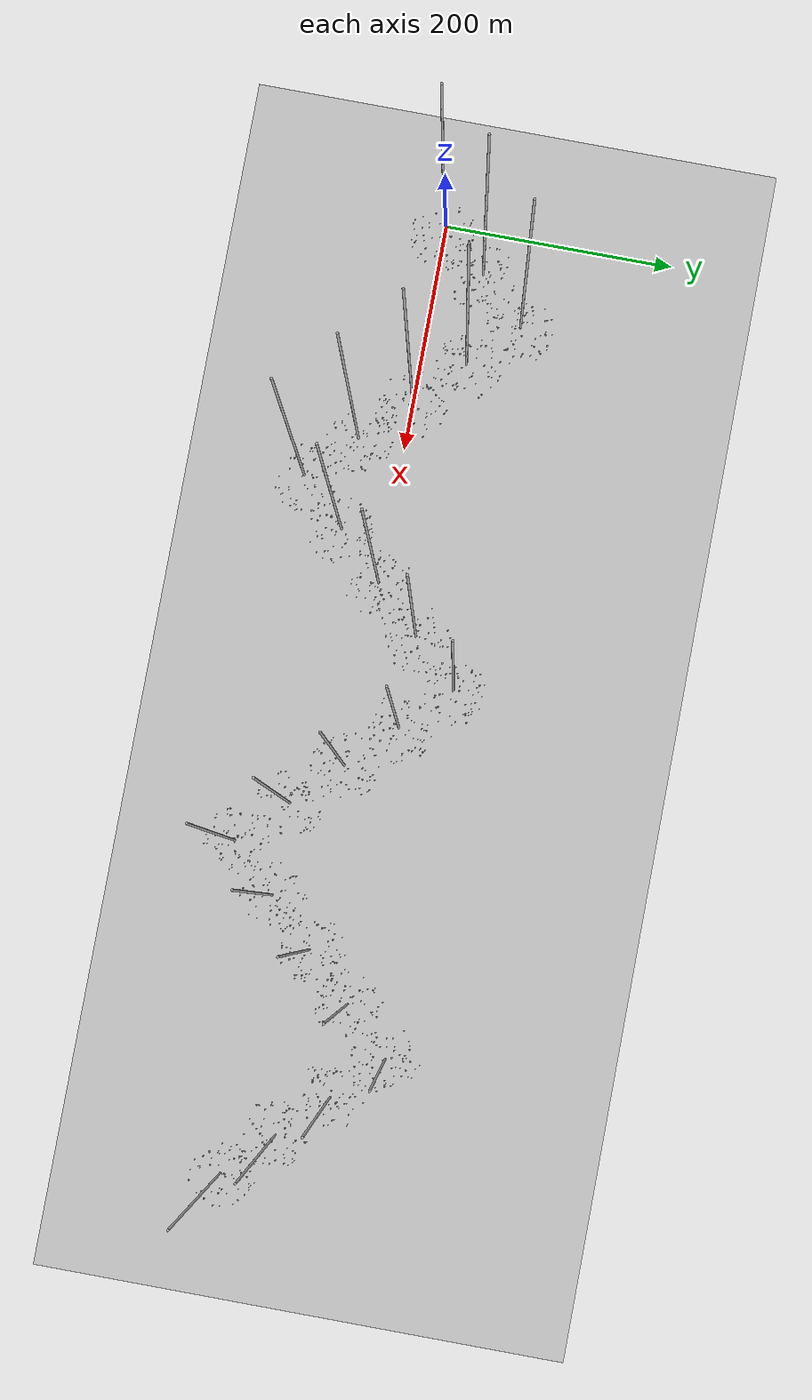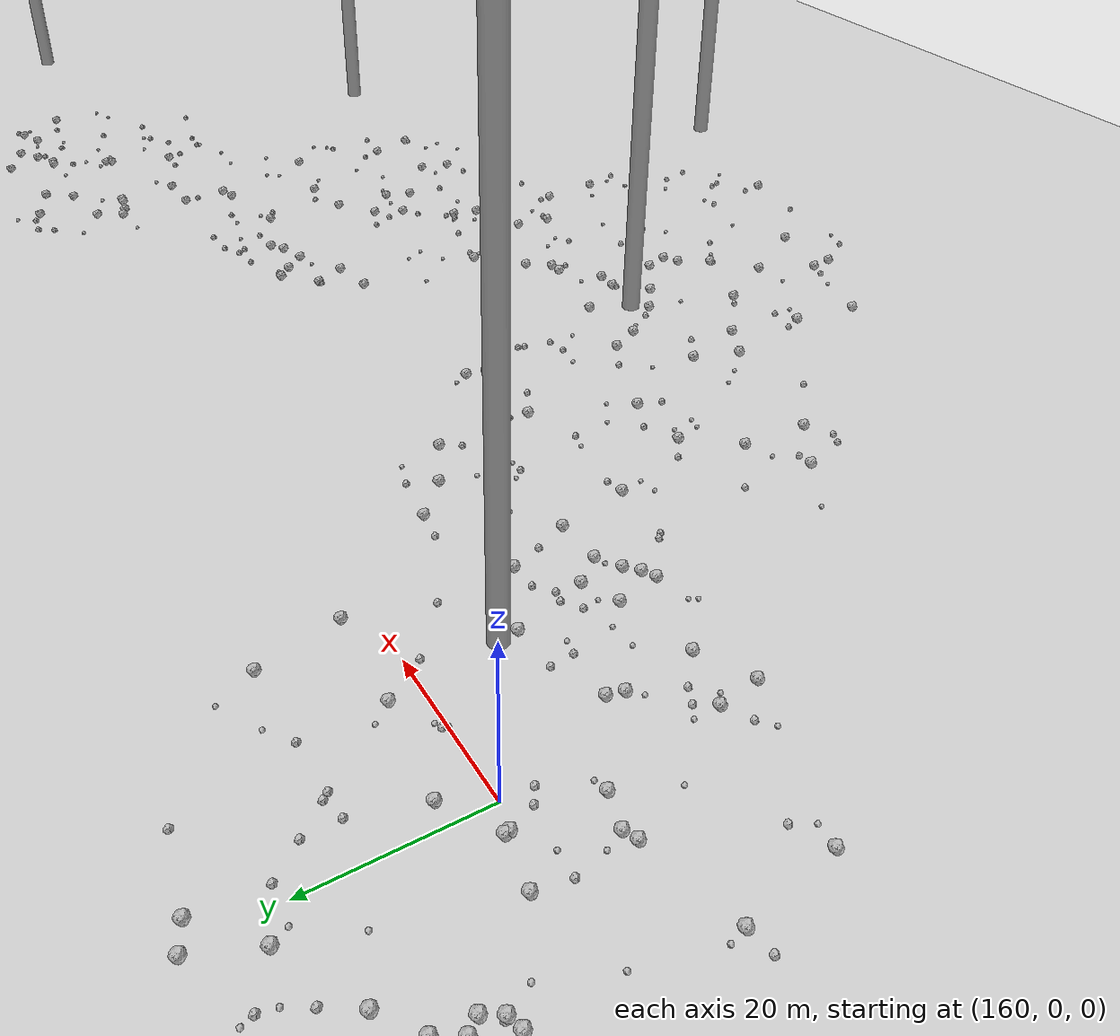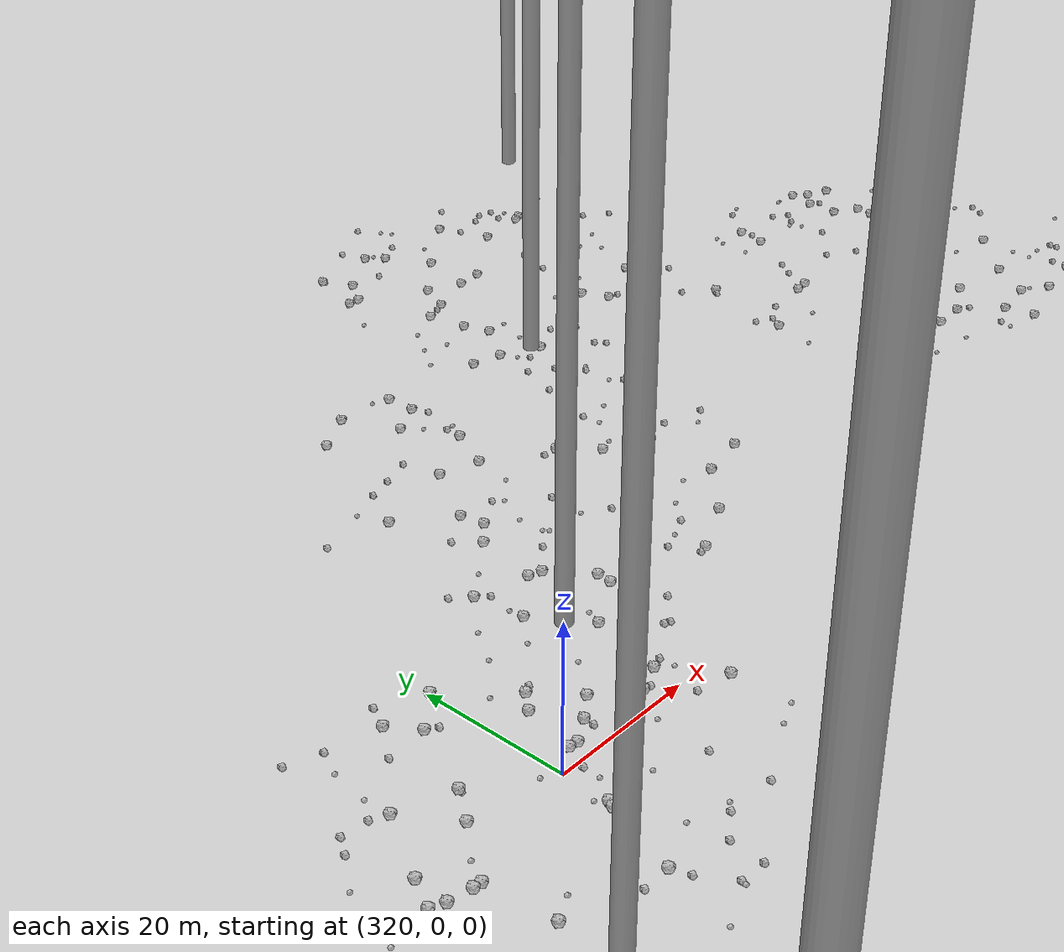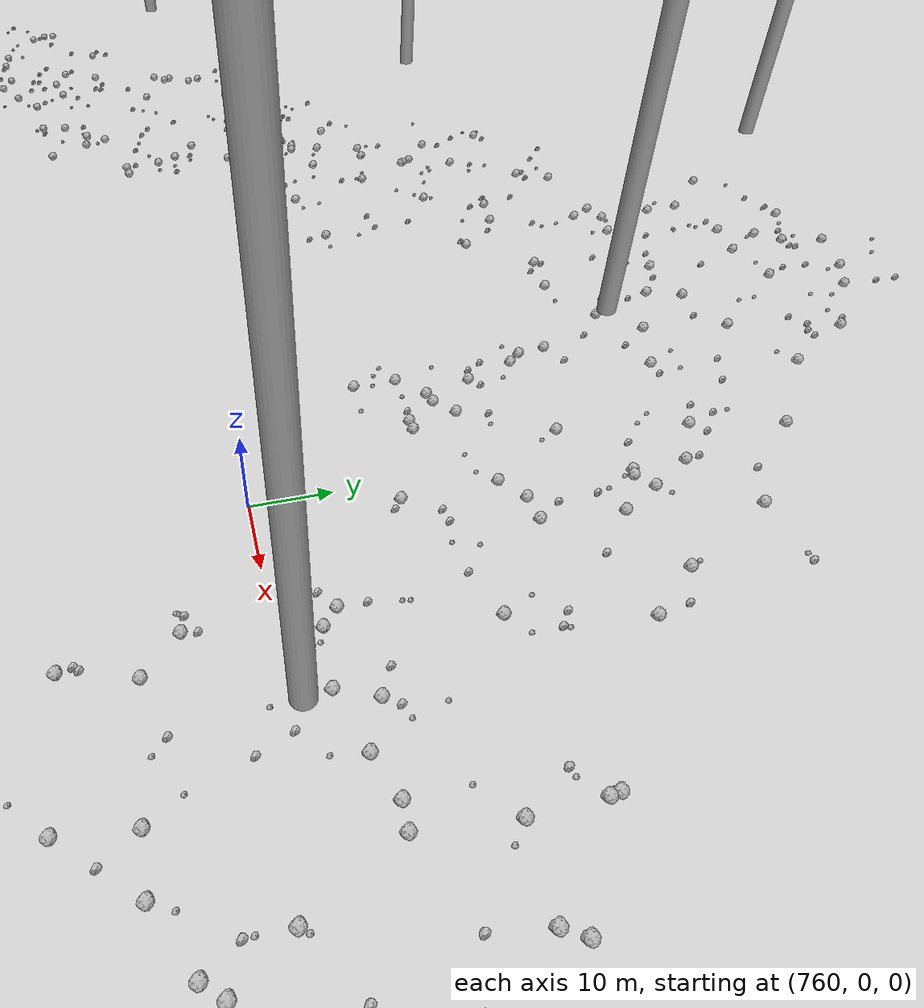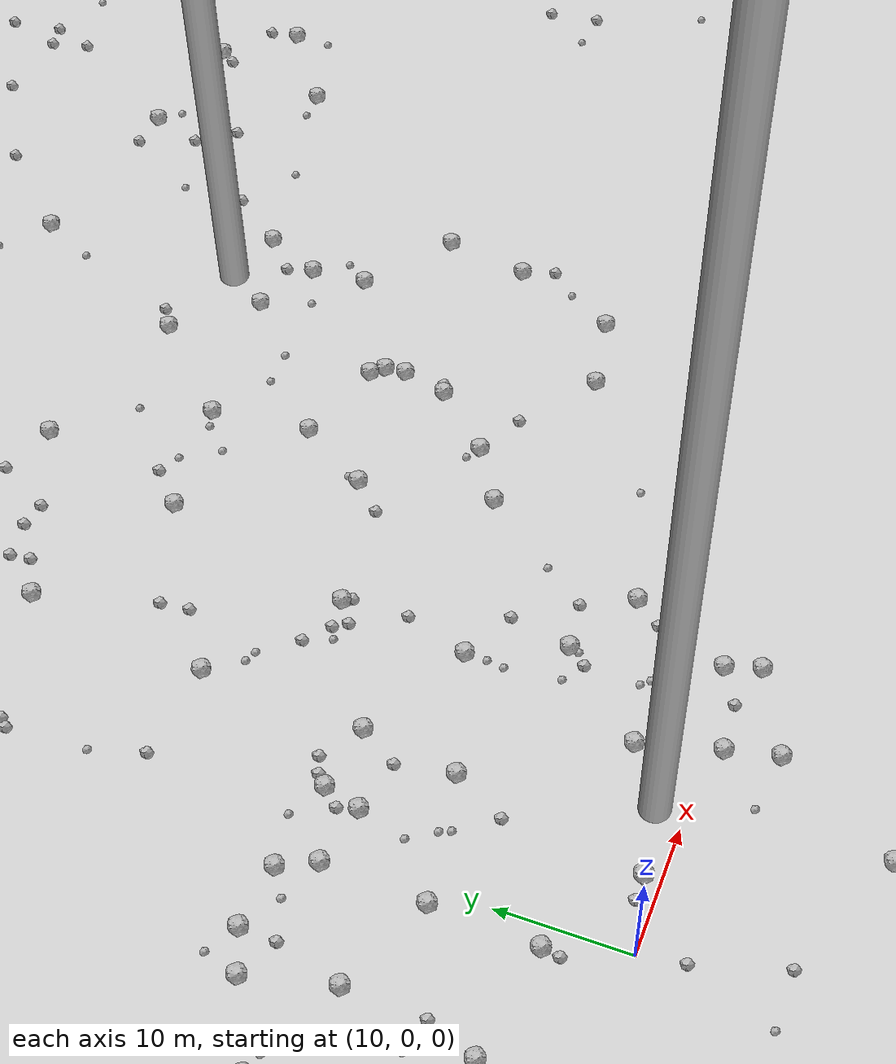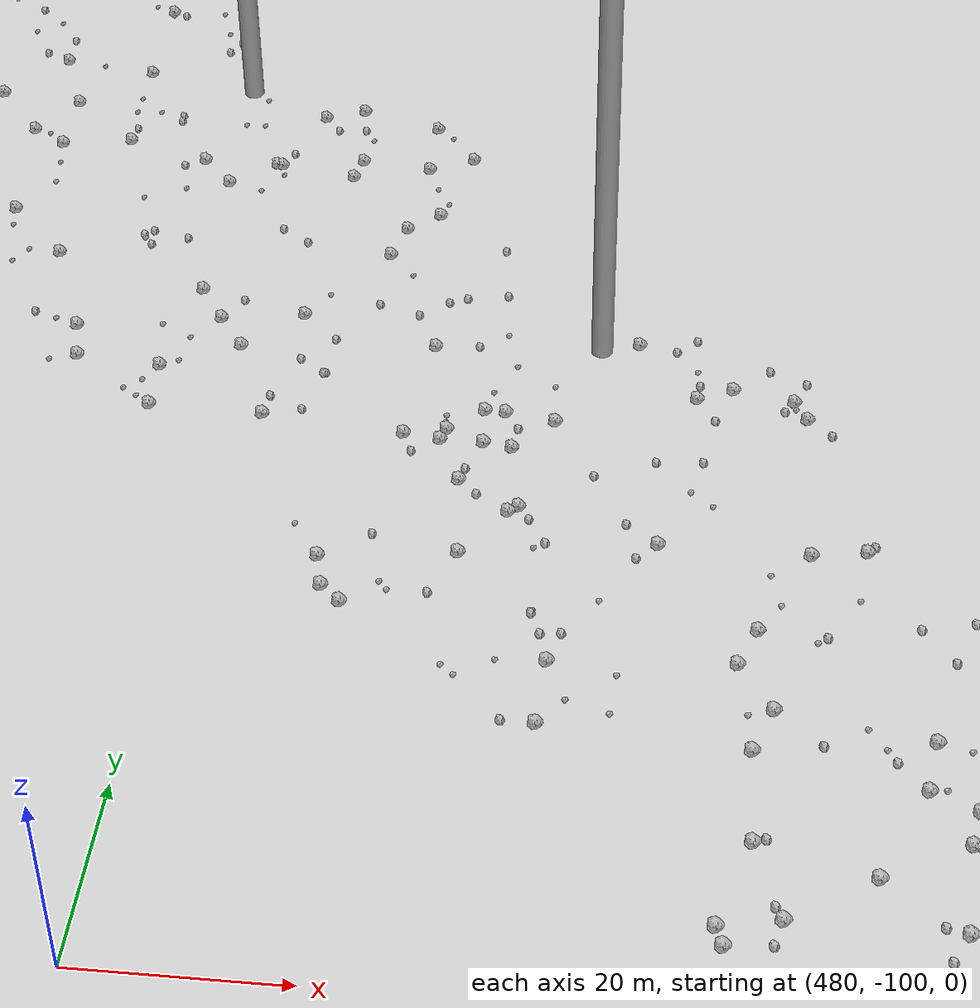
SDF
<sdf version="1.6">
 <world name="default">
  <include><uri>model://custom_ground</uri></include>
  <include><uri>model://sun</uri></include>
  <spherical_coordinates>
   <surface_model>EARTH_WGS84</surface_model>
   <latitude_deg>38.161479</latitude_deg>
   <longitude_deg>-122.454630</longitude_deg>
   <elevation>488.0</elevation>
   <heading_deg>90</heading_deg>
  </spherical_coordinates>
  <model name="rock1_0_0">
   <include><uri>model://rock1</uri><pose>13.84683944459482 21.146394671319882 0.5 0 0 0</pose></include>
  </model>
  <model name="rock1_0_1">
   <include><uri>model://rock1</uri><pose>26.95718200882083 -0.9758261307896241 0.5 0 0 0</pose></include>
  </model>
  <model name="rock1_0_2">
   <include><uri>model://rock1</uri><pose>-0.40927173895471824 7.377997038127816 0.5 0 0 0</pose></include>
  </model>
  <model name="rock1_0_3">
   <include><uri>model://rock1</uri><pose>27.837148940925594 -4.9036564211930695 0.5 0 0 0</pose></include>
  </model>
  <model name="rock1_0_4">
   <include><uri>model://rock1</uri><pose>7.8410137113628835 24.836867867896117 0.5 0 0 0</pose></include>
  </model>
  <model name="rock1_0_5">
   <include><uri>model://rock1</uri><pose>9.180823819089575 22.103956092478825 0.5 0 0 0</pose></include>
  </model>
  <model name="rock1_0_6">
   <include><uri>model://rock1</uri><pose>15.795699056922608 1.2979337149586136 0.5 0 0 0</pose></include>
  </model>
  <model name="rock1_0_7">
   <include><uri>model://rock1</uri><pose>34.3476817492514 -1.657714527392777 0.5 0 0 0</pose></include>
  </model>
  <model name="rock1_0_8">
   <include><uri>model://rock1</uri><pose>-15.333049134228053 -2.1050022323745345 0.5 0 0 0</pose></include>
  </model>
  <model name="rock1_0_9">
   <include><uri>model://rock1</uri><pose>33.561605116122095 0.9717005731866308 0.5 0 0 0</pose></include>
  </model>
  <model name="rock1_0_10">
   <include><uri>model://rock1</uri><pose>-9.685094197568409 -10.553885132304927 0.5 0 0 0</pose></include>
  </model>
  <model name="rock1_0_11">
   <include><uri>model://rock1</uri><pose>2.4976900423240664 -28.718915196016265 0.5 0 0 0</pose></include>
  </model>
  <model name="rock1_0_12">
   <include><uri>model://rock1</uri><pose>-0.9829980217120884 -27.653498648171194 0.5 0 0 0</pose></include>
  </model>
  <model name="rock1_0_13">
   <include><uri>model://rock1</uri><pose>1.284197212416899 17.399420837770954 0.5 0 0 0</pose></include>
  </model>
  <model name="rock1_0_14">
   <include><uri>model://rock1</uri><pose>-6.52589179411825 20.92784050779229 0.5 0 0 0</pose></include>
  </model>
  <model name="rock1_0_15">
   <include><uri>model://rock1</uri><pose>8.372382921546844 6.009697056738069 0.5 0 0 0</pose></include>
  </model>
  <model name="rock1_0_16">
   <include><uri>model://rock1</uri><pose>8.775401275050797 14.178896335801163 0.5 0 0 0</pose></include>
  </model>
  <model name="rock1_0_17">
   <include><uri>model://rock1</uri><pose>-0.3037480481098065 24.01722548451933 0.5 0 0 0</pose></include>
  </model>
  <model name="rock1_0_18">
   <include><uri>model://rock1</uri><pose>14.680359377006688 24.0045189042443 0.5 0 0 0</pose></include>
  </model>
  <model name="rock1_0_19">
   <include><uri>model://rock1</uri><pose>33.68630226742499 -12.528484317581832 0.5 0 0 0</pose></include>
  </model>
  <model name="rock1_0_20">
   <include><uri>model://rock1</uri><pose>2.8954675689984484 25.312186458279704 0.5 0 0 0</pose></include>
  </model>
  <model name="rock1_0_21">
   <include><uri>model://rock1</uri><pose>18.740531835735418 15.830617879196062 0.5 0 0 0</pose></include>
  </model>
  <model name="rock1_0_22">
   <include><uri>model://rock1</uri><pose>36.987644242573715 8.546518557200194 0.5 0 0 0</pose></include>
  </model>
  <model name="rock1_0_23">
   <include><uri>model://rock1</uri><pose>22.50625865034388 -14.263048425454581 0.5 0 0 0</pose></include>
  </model>
  <model name="rock1_0_24">
   <include><uri>model://rock1</uri><pose>25.33503943800742 5.050084090721995 0.5 0 0 0</pose></include>
  </model>
  <model name="rock1_0_25">
   <include><uri>model://rock1</uri><pose>18.88371295668035 -24.259120188658386 0.5 0 0 0</pose></include>
  </model>
  <model name="rock1_0_26">
   <include><uri>model://rock1</uri><pose>-14.584592439237106 8.846173603013469 0.5 0 0 0</pose></include>
  </model>
  <model name="rock2_0_0">
   <include><uri>model://rock2</uri><pose>11.440673604744944 -17.958519172436162 0.3 0 0 0</pose></include>
  </model>
  <model name="rock2_0_1">
   <include><uri>model://rock2</uri><pose>13.396429087370919 22.66915580705217 0.3 0 0 0</pose></include>
  </model>
  <model name="rock2_0_2">
   <include><uri>model://rock2</uri><pose>-4.9098451540682255 14.983354755036672 0.3 0 0 0</pose></include>
  </model>
  <model name="rock2_0_3">
   <include><uri>model://rock2</uri><pose>32.285971967408486 16.69133236886831 0.3 0 0 0</pose></include>
  </model>
  <model name="rock2_0_4">
   <include><uri>model://rock2</uri><pose>16.753350601967227 -27.324300967799424 0.3 0 0 0</pose></include>
  </model>
  <model name="rock2_0_5">
   <include><uri>model://rock2</uri><pose>2.727990867443104 22.528007357701703 0.3 0 0 0</pose></include>
  </model>
  <model name="rock2_0_6">
   <include><uri>model://rock2</uri><pose>16.77334550539741 25.33212780569658 0.3 0 0 0</pose></include>
  </model>
  <model name="rock2_0_7">
   <include><uri>model://rock2</uri><pose>30.70255055846274 -0.6628632915696784 0.3 0 0 0</pose></include>
  </model>
  <model name="rock2_0_8">
   <include><uri>model://rock2</uri><pose>4.976104124577599 -20.161831733039165 0.3 0 0 0</pose></include>
  </model>
  <model name="rock2_0_9">
   <include><uri>model://rock2</uri><pose>-0.9098532953234972 -5.8640727042641885 0.3 0 0 0</pose></include>
  </model>
  <model name="rock2_0_10">
   <include><uri>model://rock2</uri><pose>16.47771127631951 11.733223683046347 0.3 0 0 0</pose></include>
  </model>
  <model name="rock2_0_11">
   <include><uri>model://rock2</uri><pose>8.109892025404644 4.617402868855692 0.3 0 0 0</pose></include>
  </model>
  <model name="rock2_0_12">
   <include><uri>model://rock2</uri><pose>7.6121546595216145 -26.9872349157392 0.3 0 0 0</pose></include>
  </model>
  <model name="rock2_0_13">
   <include><uri>model://rock2</uri><pose>31.685610754900907 -19.247193441011312 0.3 0 0 0</pose></include>
  </model>
  <model name="rock2_0_14">
   <include><uri>model://rock2</uri><pose>1.0244298734617097 11.221619107060285 0.3 0 0 0</pose></include>
  </model>
  <model name="rock2_0_15">
   <include><uri>model://rock2</uri><pose>16.97035188172118 -23.89080889643359 0.3 0 0 0</pose></include>
  </model>
  <model name="rock2_0_16">
   <include><uri>model://rock2</uri><pose>30.160673116981236 10.388290896692077 0.3 0 0 0</pose></include>
  </model>
  <model name="rock2_0_17">
   <include><uri>model://rock2</uri><pose>-0.3686457133817811 -14.838950978948866 0.3 0 0 0</pose></include>
  </model>
  <model name="rock2_0_18">
   <include><uri>model://rock2</uri><pose>35.2553218822696 6.4323606795421 0.3 0 0 0</pose></include>
  </model>
  <model name="rock2_0_19">
   <include><uri>model://rock2</uri><pose>15.44926671347725 24.821119820687187 0.3 0 0 0</pose></include>
  </model>
  <model name="rock2_0_20">
   <include><uri>model://rock2</uri><pose>-9.822425233781129 22.20148986236675 0.3 0 0 0</pose></include>
  </model>
  <model name="rock2_0_21">
   <include><uri>model://rock2</uri><pose>-4.433050180551097 -21.330819021355232 0.3 0 0 0</pose></include>
  </model>
  <model name="rock2_0_22">
   <include><uri>model://rock2</uri><pose>10.50472501497405 -3.3805236209735696 0.3 0 0 0</pose></include>
  </model>
  <model name="rock2_0_23">
   <include><uri>model://rock2</uri><pose>13.798685972757426 1.245237372755522 0.3 0 0 0</pose></include>
  </model>
  <model name="rock2_0_24">
   <include><uri>model://rock2</uri><pose>0.8686764597434475 -19.94654454332095 0.3 0 0 0</pose></include>
  </model>
  <model name="rock2_0_25">
   <include><uri>model://rock2</uri><pose>12.514384085866212 -10.07221025684613 0.3 0 0 0</pose></include>
  </model>
  <model name="rock2_0_26">
   <include><uri>model://rock2</uri><pose>28.102656592073167 -17.24488456831433 0.3 0 0 0</pose></include>
  </model>
  <model name="rock3_0_0">
   <include><uri>model://rock3</uri><pose>12.333533930479561 -23.94415542734754 0.2 0 0 0</pose></include>
  </model>
  <model name="rock3_0_1">
   <include><uri>model://rock3</uri><pose>12.793105835156602 17.372187130169436 0.2 0 0 0</pose></include>
  </model>
  <model name="rock3_0_2">
   <include><uri>model://rock3</uri><pose>28.550954192712126 11.477207831813544 0.2 0 0 0</pose></include>
  </model>
  <model name="rock3_0_3">
   <include><uri>model://rock3</uri><pose>11.83311054856151 25.517287518024922 0.2 0 0 0</pose></include>
  </model>
  <model name="rock3_0_4">
   <include><uri>model://rock3</uri><pose>23.173582735275332 -4.37003701495194 0.2 0 0 0</pose></include>
  </model>
  <model name="rock3_0_5">
   <include><uri>model://rock3</uri><pose>-18.522020429342156 8.657425080889965 0.2 0 0 0</pose></include>
  </model>
  <model name="rock3_0_6">
   <include><uri>model://rock3</uri><pose>-1.5801956771310621 11.892818224721879 0.2 0 0 0</pose></include>
  </model>
  <model name="rock3_0_7">
   <include><uri>model://rock3</uri><pose>14.089845177882943 15.393621134741451 0.2 0 0 0</pose></include>
  </model>
  <model name="rock3_0_8">
   <include><uri>model://rock3</uri><pose>3.266703346733145 -14.216768889731156 0.2 0 0 0</pose></include>
  </model>
  <model name="rock3_0_9">
   <include><uri>model://rock3</uri><pose>-15.841968276694862 2.4484479960060455 0.2 0 0 0</pose></include>
  </model>
  <model name="rock3_0_10">
   <include><uri>model://rock3</uri><pose>10.237291506385166 -28.463679720875195 0.2 0 0 0</pose></include>
  </model>
  <model name="rock3_0_11">
   <include><uri>model://rock3</uri><pose>30.645930267522225 5.504864606921224 0.2 0 0 0</pose></include>
  </model>
  <model name="rock3_0_12">
   <include><uri>model://rock3</uri><pose>15.6506375463332 -16.762321468555587 0.2 0 0 0</pose></include>
  </model>
  <model name="rock3_0_13">
   <include><uri>model://rock3</uri><pose>0.4667371699356053 26.708336602827032 0.2 0 0 0</pose></include>
  </model>
  <model name="rock3_0_14">
   <include><uri>model://rock3</uri><pose>-4.8332080424444435 20.397781734667042 0.2 0 0 0</pose></include>
  </model>
  <model name="rock3_0_15">
   <include><uri>model://rock3</uri><pose>31.136076847776117 11.080155871000962 0.2 0 0 0</pose></include>
  </model>
  <model name="rock3_0_16">
   <include><uri>model://rock3</uri><pose>5.775123413554496 23.48935810888083 0.2 0 0 0</pose></include>
  </model>
  <model name="rock3_0_17">
   <include><uri>model://rock3</uri><pose>-1.4567971486840463 -23.543566090398603 0.2 0 0 0</pose></include>
  </model>
  <model name="rock3_0_18">
   <include><uri>model://rock3</uri><pose>28.238214743638174 17.04596893760465 0.2 0 0 0</pose></include>
  </model>
  <model name="rock3_0_19">
   <include><uri>model://rock3</uri><pose>20.71040396002695 -15.58677476214105 0.2 0 0 0</pose></include>
  </model>
  <model name="rock3_0_20">
   <include><uri>model://rock3</uri><pose>14.441461243540736 14.570336642728904 0.2 0 0 0</pose></include>
  </model>
  <model name="rock3_0_21">
   <include><uri>model://rock3</uri><pose>-5.011762134893454 -13.555431755731366 0.2 0 0 0</pose></include>
  </model>
  <model name="rock3_0_22">
   <include><uri>model://rock3</uri><pose>33.81768811511151 -16.319317114247337 0.2 0 0 0</pose></include>
  </model>
  <model name="rock3_0_23">
   <include><uri>model://rock3</uri><pose>8.000909334204529 -10.102247355098555 0.2 0 0 0</pose></include>
  </model>
  <model name="rock3_0_24">
   <include><uri>model://rock3</uri><pose>30.071643977997624 6.125680370624842 0.2 0 0 0</pose></include>
  </model>
  <model name="rock3_0_25">
   <include><uri>model://rock3</uri><pose>28.06384456248906 15.719294590998835 0.2 0 0 0</pose></include>
  </model>
  <model name="rock3_0_26">
   <include><uri>model://rock3</uri><pose>23.12360965966846 -25.68808427553284 0.2 0 0 0</pose></include>
  </model>
  <model name="rock1_1_0">
   <include><uri>model://rock1</uri><pose>58.74149658354562 43.24739885429581 0.5 0 0 0</pose></include>
  </model>
  <model name="rock1_1_1">
   <include><uri>model://rock1</uri><pose>36.341688979300486 55.86099693596211 0.5 0 0 0</pose></include>
  </model>
  <model name="rock1_1_2">
   <include><uri>model://rock1</uri><pose>29.46795433964318 28.771160317608846 0.5 0 0 0</pose></include>
  </model>
  <model name="rock1_1_3">
   <include><uri>model://rock1</uri><pose>20.478462317975154 35.92489712435997 0.5 0 0 0</pose></include>
  </model>
  <model name="rock1_1_4">
   <include><uri>model://rock1</uri><pose>50.2931985046923 34.89511165983825 0.5 0 0 0</pose></include>
  </model>
  <model name="rock1_1_5">
   <include><uri>model://rock1</uri><pose>54.063628921612036 45.872659880198775 0.5 0 0 0</pose></include>
  </model>
  <model name="rock1_1_6">
   <include><uri>model://rock1</uri><pose>42.46021006656801 44.91215578566767 0.5 0 0 0</pose></include>
  </model>
  <model name="rock1_1_7">
   <include><uri>model://rock1</uri><pose>41.89166516577137 21.46724205825878 0.5 0 0 0</pose></include>
  </model>
  <model name="rock1_1_8">
   <include><uri>model://rock1</uri><pose>28.267187831956846 18.76726299060593 0.5 0 0 0</pose></include>
  </model>
  <model name="rock1_1_9">
   <include><uri>model://rock1</uri><pose>49.27478271577288 51.75660118170096 0.5 0 0 0</pose></include>
  </model>
  <model name="rock1_1_10">
   <include><uri>model://rock1</uri><pose>45.1069932126694 67.30708458748373 0.5 0 0 0</pose></include>
  </model>
  <model name="rock1_1_11">
   <include><uri>model://rock1</uri><pose>60.78123512976154 47.64918500066133 0.5 0 0 0</pose></include>
  </model>
  <model name="rock1_1_12">
   <include><uri>model://rock1</uri><pose>31.377630716256718 11.87458634737789 0.5 0 0 0</pose></include>
  </model>
  <model name="rock1_1_13">
   <include><uri>model://rock1</uri><pose>40.04998833406117 31.747712143166726 0.5 0 0 0</pose></include>
  </model>
  <model name="rock1_1_14">
   <include><uri>model://rock1</uri><pose>33.245448404862515 43.91276615648093 0.5 0 0 0</pose></include>
  </model>
  <model name="rock1_1_15">
   <include><uri>model://rock1</uri><pose>64.44129659697253 27.184908192244237 0.5 0 0 0</pose></include>
  </model>
  <model name="rock1_1_16">
   <include><uri>model://rock1</uri><pose>22.22708384102844 50.27654043579577 0.5 0 0 0</pose></include>
  </model>
  <model name="rock1_1_17">
   <include><uri>model://rock1</uri><pose>43.36605607949274 37.19195764579729 0.5 0 0 0</pose></include>
  </model>
  <model name="rock1_1_18">
   <include><uri>model://rock1</uri><pose>46.17363742479379 24.16952874205635 0.5 0 0 0</pose></include>
  </model>
  <model name="rock1_1_19">
   <include><uri>model://rock1</uri><pose>59.101278199198404 38.882077199909574 0.5 0 0 0</pose></include>
  </model>
  <model name="rock1_1_20">
   <include><uri>model://rock1</uri><pose>65.50349643810229 33.75778853830461 0.5 0 0 0</pose></include>
  </model>
  <model name="rock1_1_21">
   <include><uri>model://rock1</uri><pose>61.41215627064028 19.06635612433201 0.5 0 0 0</pose></include>
  </model>
  <model name="rock1_1_22">
   <include><uri>model://rock1</uri><pose>51.121700252289095 33.91829619611264 0.5 0 0 0</pose></include>
  </model>
  <model name="rock1_1_23">
   <include><uri>model://rock1</uri><pose>50.38965642543927 28.732476691455716 0.5 0 0 0</pose></include>
  </model>
  <model name="rock1_1_24">
   <include><uri>model://rock1</uri><pose>51.26091247683292 32.28175534280078 0.5 0 0 0</pose></include>
  </model>
  <model name="rock1_1_25">
   <include><uri>model://rock1</uri><pose>55.4876713740678 17.940156605035238 0.5 0 0 0</pose></include>
  </model>
  <model name="rock1_1_26">
   <include><uri>model://rock1</uri><pose>19.878380037929936 23.23389566809652 0.5 0 0 0</pose></include>
  </model>
  <model name="rock2_1_0">
   <include><uri>model://rock2</uri><pose>11.341439706924437 46.91347940272064 0.3 0 0 0</pose></include>
  </model>
  <model name="rock2_1_1">
   <include><uri>model://rock2</uri><pose>27.082796544979946 28.591084115060767 0.3 0 0 0</pose></include>
  </model>
  <model name="rock2_1_2">
   <include><uri>model://rock2</uri><pose>12.882430696990514 36.694809696057966 0.3 0 0 0</pose></include>
  </model>
  <model name="rock2_1_3">
   <include><uri>model://rock2</uri><pose>24.88765905844593 38.91546986751438 0.3 0 0 0</pose></include>
  </model>
  <model name="rock2_1_4">
   <include><uri>model://rock2</uri><pose>35.036158185705176 12.363770260630318 0.3 0 0 0</pose></include>
  </model>
  <model name="rock2_1_5">
   <include><uri>model://rock2</uri><pose>35.74820130048929 46.369787315357115 0.3 0 0 0</pose></include>
  </model>
  <model name="rock2_1_6">
   <include><uri>model://rock2</uri><pose>27.7387039138906 27.561981507375773 0.3 0 0 0</pose></include>
  </model>
  <model name="rock2_1_7">
   <include><uri>model://rock2</uri><pose>49.70756040277665 22.25688056465052 0.3 0 0 0</pose></include>
  </model>
  <model name="rock2_1_8">
   <include><uri>model://rock2</uri><pose>16.944529900028385 58.421854899076145 0.3 0 0 0</pose></include>
  </model>
  <model name="rock2_1_9">
   <include><uri>model://rock2</uri><pose>24.96508488676456 51.837500324299185 0.3 0 0 0</pose></include>
  </model>
  <model name="rock2_1_10">
   <include><uri>model://rock2</uri><pose>27.667550977992402 53.72649524450202 0.3 0 0 0</pose></include>
  </model>
  <model name="rock2_1_11">
   <include><uri>model://rock2</uri><pose>11.949717798755685 47.56781685879824 0.3 0 0 0</pose></include>
  </model>
  <model name="rock2_1_12">
   <include><uri>model://rock2</uri><pose>25.243184160459258 30.1729274099897 0.3 0 0 0</pose></include>
  </model>
  <model name="rock2_1_13">
   <include><uri>model://rock2</uri><pose>50.82232368594183 52.79517002029539 0.3 0 0 0</pose></include>
  </model>
  <model name="rock2_1_14">
   <include><uri>model://rock2</uri><pose>59.91274997830408 50.41942612600066 0.3 0 0 0</pose></include>
  </model>
  <model name="rock2_1_15">
   <include><uri>model://rock2</uri><pose>29.79105823878063 23.71836748726538 0.3 0 0 0</pose></include>
  </model>
  <model name="rock2_1_16">
   <include><uri>model://rock2</uri><pose>37.79234218348138 29.467892889804855 0.3 0 0 0</pose></include>
  </model>
  <model name="rock2_1_17">
   <include><uri>model://rock2</uri><pose>51.11626208085865 29.00970387103372 0.3 0 0 0</pose></include>
  </model>
  <model name="rock2_1_18">
   <include><uri>model://rock2</uri><pose>29.666343562701666 53.31207108991148 0.3 0 0 0</pose></include>
  </model>
  <model name="rock2_1_19">
   <include><uri>model://rock2</uri><pose>29.813121210973748 28.094439972477442 0.3 0 0 0</pose></include>
  </model>
  <model name="rock2_1_20">
   <include><uri>model://rock2</uri><pose>58.147845066802624 45.32557949498435 0.3 0 0 0</pose></include>
  </model>
  <model name="rock2_1_21">
   <include><uri>model://rock2</uri><pose>24.671242628072616 41.16530215141803 0.3 0 0 0</pose></include>
  </model>
  <model name="rock2_1_22">
   <include><uri>model://rock2</uri><pose>63.98806533863881 51.89086552661271 0.3 0 0 0</pose></include>
  </model>
  <model name="rock2_1_23">
   <include><uri>model://rock2</uri><pose>31.981161437167913 57.46438011790836 0.3 0 0 0</pose></include>
  </model>
  <model name="rock2_1_24">
   <include><uri>model://rock2</uri><pose>17.933019487258793 20.209099959267846 0.3 0 0 0</pose></include>
  </model>
  <model name="rock2_1_25">
   <include><uri>model://rock2</uri><pose>24.78506211061969 53.424265510423666 0.3 0 0 0</pose></include>
  </model>
  <model name="rock2_1_26">
   <include><uri>model://rock2</uri><pose>65.22569848827727 24.666981328264786 0.3 0 0 0</pose></include>
  </model>
  <model name="rock3_1_0">
   <include><uri>model://rock3</uri><pose>40.24994994111799 32.639321538721845 0.2 0 0 0</pose></include>
  </model>
  <model name="rock3_1_1">
   <include><uri>model://rock3</uri><pose>36.876184831564245 56.18197874677433 0.2 0 0 0</pose></include>
  </model>
  <model name="rock3_1_2">
   <include><uri>model://rock3</uri><pose>29.226338481663493 64.81308862528516 0.2 0 0 0</pose></include>
  </model>
  <model name="rock3_1_3">
   <include><uri>model://rock3</uri><pose>23.18320092368339 32.90820177011464 0.2 0 0 0</pose></include>
  </model>
  <model name="rock3_1_4">
   <include><uri>model://rock3</uri><pose>68.34318466715007 48.8592982141624 0.2 0 0 0</pose></include>
  </model>
  <model name="rock3_1_5">
   <include><uri>model://rock3</uri><pose>40.829176136136255 50.36547982215694 0.2 0 0 0</pose></include>
  </model>
  <model name="rock3_1_6">
   <include><uri>model://rock3</uri><pose>60.37272983596416 40.693441322710704 0.2 0 0 0</pose></include>
  </model>
  <model name="rock3_1_7">
   <include><uri>model://rock3</uri><pose>26.125916746458735 28.081744726943512 0.2 0 0 0</pose></include>
  </model>
  <model name="rock3_1_8">
   <include><uri>model://rock3</uri><pose>53.93605422993914 61.37017508901051 0.2 0 0 0</pose></include>
  </model>
  <model name="rock3_1_9">
   <include><uri>model://rock3</uri><pose>25.8300050479662 59.56504890816398 0.2 0 0 0</pose></include>
  </model>
  <model name="rock3_1_10">
   <include><uri>model://rock3</uri><pose>49.654427539887685 41.865267105620646 0.2 0 0 0</pose></include>
  </model>
  <model name="rock3_1_11">
   <include><uri>model://rock3</uri><pose>55.436379450722 42.00253478682891 0.2 0 0 0</pose></include>
  </model>
  <model name="rock3_1_12">
   <include><uri>model://rock3</uri><pose>46.82199166916277 41.88807875712411 0.2 0 0 0</pose></include>
  </model>
  <model name="rock3_1_13">
   <include><uri>model://rock3</uri><pose>45.04634065250582 24.870926414554564 0.2 0 0 0</pose></include>
  </model>
  <model name="rock3_1_14">
   <include><uri>model://rock3</uri><pose>41.05296527451081 44.52067552466395 0.2 0 0 0</pose></include>
  </model>
  <model name="rock3_1_15">
   <include><uri>model://rock3</uri><pose>46.36165500693191 11.313236960890984 0.2 0 0 0</pose></include>
  </model>
  <model name="rock3_1_16">
   <include><uri>model://rock3</uri><pose>22.26140552513577 33.29894635785552 0.2 0 0 0</pose></include>
  </model>
  <model name="rock3_1_17">
   <include><uri>model://rock3</uri><pose>41.05285065389752 67.60324370371447 0.2 0 0 0</pose></include>
  </model>
  <model name="rock3_1_18">
   <include><uri>model://rock3</uri><pose>26.021943561848275 58.65412003445699 0.2 0 0 0</pose></include>
  </model>
  <model name="rock3_1_19">
   <include><uri>model://rock3</uri><pose>20.293211690328672 61.094488269874674 0.2 0 0 0</pose></include>
  </model>
  <model name="rock3_1_20">
   <include><uri>model://rock3</uri><pose>63.42014477896361 22.60026066828483 0.2 0 0 0</pose></include>
  </model>
  <model name="rock3_1_21">
   <include><uri>model://rock3</uri><pose>37.395548709707725 15.62233401579906 0.2 0 0 0</pose></include>
  </model>
  <model name="rock3_1_22">
   <include><uri>model://rock3</uri><pose>11.695694893017269 40.71573080093859 0.2 0 0 0</pose></include>
  </model>
  <model name="rock3_1_23">
   <include><uri>model://rock3</uri><pose>11.685828587723089 49.86984419647489 0.2 0 0 0</pose></include>
  </model>
  <model name="rock3_1_24">
   <include><uri>model://rock3</uri><pose>37.41999924636631 45.46507070615019 0.2 0 0 0</pose></include>
  </model>
  <model name="rock3_1_25">
   <include><uri>model://rock3</uri><pose>39.17562864997329 42.61531423109735 0.2 0 0 0</pose></include>
  </model>
  <model name="rock3_1_26">
   <include><uri>model://rock3</uri><pose>34.11713727527505 59.86982669657882 0.2 0 0 0</pose></include>
  </model>
  <model name="rock1_2_0">
   <include><uri>model://rock1</uri><pose>98.92820588009289 85.72689382956393 0.5 0 0 0</pose></include>
  </model>
  <model name="rock1_2_1">
   <include><uri>model://rock1</uri><pose>89.89834766308684 92.19934869872162 0.5 0 0 0</pose></include>
  </model>
  <model name="rock1_2_2">
   <include><uri>model://rock1</uri><pose>62.41458669563768 82.85130195664266 0.5 0 0 0</pose></include>
  </model>
  <model name="rock1_2_3">
   <include><uri>model://rock1</uri><pose>102.21451856652641 78.28713091248787 0.5 0 0 0</pose></include>
  </model>
  <model name="rock1_2_4">
   <include><uri>model://rock1</uri><pose>59.61948052457191 87.93604176668035 0.5 0 0 0</pose></include>
  </model>
  <model name="rock1_2_5">
   <include><uri>model://rock1</uri><pose>70.45618886743023 62.484418024553605 0.5 0 0 0</pose></include>
  </model>
  <model name="rock1_2_6">
   <include><uri>model://rock1</uri><pose>59.40524168716885 75.34675568306143 0.5 0 0 0</pose></include>
  </model>
  <model name="rock1_2_7">
   <include><uri>model://rock1</uri><pose>66.01455236229675 101.3987431579379 0.5 0 0 0</pose></include>
  </model>
  <model name="rock1_2_8">
   <include><uri>model://rock1</uri><pose>83.84261206848754 94.29896363422641 0.5 0 0 0</pose></include>
  </model>
  <model name="rock1_2_9">
   <include><uri>model://rock1</uri><pose>95.7904063800129 100.93411842846601 0.5 0 0 0</pose></include>
  </model>
  <model name="rock1_2_10">
   <include><uri>model://rock1</uri><pose>77.63204019466318 50.732243013037454 0.5 0 0 0</pose></include>
  </model>
  <model name="rock1_2_11">
   <include><uri>model://rock1</uri><pose>93.90842521366154 99.44704312792254 0.5 0 0 0</pose></include>
  </model>
  <model name="rock1_2_12">
   <include><uri>model://rock1</uri><pose>56.65246675067862 86.59012125633672 0.5 0 0 0</pose></include>
  </model>
  <model name="rock1_2_13">
   <include><uri>model://rock1</uri><pose>97.70170570440156 70.68777488144208 0.5 0 0 0</pose></include>
  </model>
  <model name="rock1_2_14">
   <include><uri>model://rock1</uri><pose>87.90814645517045 105.53279366947774 0.5 0 0 0</pose></include>
  </model>
  <model name="rock1_2_15">
   <include><uri>model://rock1</uri><pose>90.60951999795347 94.55030048455214 0.5 0 0 0</pose></include>
  </model>
  <model name="rock1_2_16">
   <include><uri>model://rock1</uri><pose>83.36880683077018 82.14078131502578 0.5 0 0 0</pose></include>
  </model>
  <model name="rock1_2_17">
   <include><uri>model://rock1</uri><pose>66.74592700920553 99.81949072218796 0.5 0 0 0</pose></include>
  </model>
  <model name="rock1_2_18">
   <include><uri>model://rock1</uri><pose>56.068517042267956 65.54118336210354 0.5 0 0 0</pose></include>
  </model>
  <model name="rock1_2_19">
   <include><uri>model://rock1</uri><pose>97.71044002277009 72.1190182491995 0.5 0 0 0</pose></include>
  </model>
  <model name="rock1_2_20">
   <include><uri>model://rock1</uri><pose>64.53235493409474 105.13941942182451 0.5 0 0 0</pose></include>
  </model>
  <model name="rock1_2_21">
   <include><uri>model://rock1</uri><pose>84.16234335248765 55.34948391527486 0.5 0 0 0</pose></include>
  </model>
  <model name="rock1_2_22">
   <include><uri>model://rock1</uri><pose>79.98922546613942 60.65039121341755 0.5 0 0 0</pose></include>
  </model>
  <model name="rock1_2_23">
   <include><uri>model://rock1</uri><pose>65.02133487838313 81.56164642814171 0.5 0 0 0</pose></include>
  </model>
  <model name="rock1_2_24">
   <include><uri>model://rock1</uri><pose>78.30119999723361 102.06969798231967 0.5 0 0 0</pose></include>
  </model>
  <model name="rock1_2_25">
   <include><uri>model://rock1</uri><pose>91.90371950819619 76.18104751477597 0.5 0 0 0</pose></include>
  </model>
  <model name="rock1_2_26">
   <include><uri>model://rock1</uri><pose>101.2191991976629 84.8095858305298 0.5 0 0 0</pose></include>
  </model>
  <model name="rock2_2_0">
   <include><uri>model://rock2</uri><pose>76.55120706367063 72.30378785267774 0.3 0 0 0</pose></include>
  </model>
  <model name="rock2_2_1">
   <include><uri>model://rock2</uri><pose>92.42824292828873 80.54774543100366 0.3 0 0 0</pose></include>
  </model>
  <model name="rock2_2_2">
   <include><uri>model://rock2</uri><pose>101.26636119633886 98.35921344722621 0.3 0 0 0</pose></include>
  </model>
  <model name="rock2_2_3">
   <include><uri>model://rock2</uri><pose>64.34292178938291 75.9896646541046 0.3 0 0 0</pose></include>
  </model>
  <model name="rock2_2_4">
   <include><uri>model://rock2</uri><pose>77.7170992465962 75.57387159568759 0.3 0 0 0</pose></include>
  </model>
  <model name="rock2_2_5">
   <include><uri>model://rock2</uri><pose>63.38903570799118 89.15314590220683 0.3 0 0 0</pose></include>
  </model>
  <model name="rock2_2_6">
   <include><uri>model://rock2</uri><pose>95.35195571212677 78.39828390037587 0.3 0 0 0</pose></include>
  </model>
  <model name="rock2_2_7">
   <include><uri>model://rock2</uri><pose>99.72218748924891 92.58966665383907 0.3 0 0 0</pose></include>
  </model>
  <model name="rock2_2_8">
   <include><uri>model://rock2</uri><pose>62.237474238732524 72.04352002070361 0.3 0 0 0</pose></include>
  </model>
  <model name="rock2_2_9">
   <include><uri>model://rock2</uri><pose>77.19565659891599 79.74285402689293 0.3 0 0 0</pose></include>
  </model>
  <model name="rock2_2_10">
   <include><uri>model://rock2</uri><pose>70.25241157799746 89.65140550765634 0.3 0 0 0</pose></include>
  </model>
  <model name="rock2_2_11">
   <include><uri>model://rock2</uri><pose>71.17812276509696 55.488186217827675 0.3 0 0 0</pose></include>
  </model>
  <model name="rock2_2_12">
   <include><uri>model://rock2</uri><pose>70.83252847495996 81.81582128888482 0.3 0 0 0</pose></include>
  </model>
  <model name="rock2_2_13">
   <include><uri>model://rock2</uri><pose>75.80818390660238 75.29274134447388 0.3 0 0 0</pose></include>
  </model>
  <model name="rock2_2_14">
   <include><uri>model://rock2</uri><pose>98.54145682159046 93.13007480028686 0.3 0 0 0</pose></include>
  </model>
  <model name="rock2_2_15">
   <include><uri>model://rock2</uri><pose>97.85183275477476 69.09720745541053 0.3 0 0 0</pose></include>
  </model>
  <model name="rock2_2_16">
   <include><uri>model://rock2</uri><pose>69.7591835469124 76.22268941567457 0.3 0 0 0</pose></include>
  </model>
  <model name="rock2_2_17">
   <include><uri>model://rock2</uri><pose>108.95635471704034 76.16703164791966 0.3 0 0 0</pose></include>
  </model>
  <model name="rock2_2_18">
   <include><uri>model://rock2</uri><pose>96.40632093845662 72.2454732324736 0.3 0 0 0</pose></include>
  </model>
  <model name="rock2_2_19">
   <include><uri>model://rock2</uri><pose>83.75659407627768 57.64625147381905 0.3 0 0 0</pose></include>
  </model>
  <model name="rock2_2_20">
   <include><uri>model://rock2</uri><pose>59.75038982229815 79.91392162284887 0.3 0 0 0</pose></include>
  </model>
  <model name="rock2_2_21">
   <include><uri>model://rock2</uri><pose>67.38422218229991 62.9262036034971 0.3 0 0 0</pose></include>
  </model>
  <model name="rock2_2_22">
   <include><uri>model://rock2</uri><pose>89.06925049849197 74.11842509560252 0.3 0 0 0</pose></include>
  </model>
  <model name="rock2_2_23">
   <include><uri>model://rock2</uri><pose>69.06604834985004 58.47079067016256 0.3 0 0 0</pose></include>
  </model>
  <model name="rock2_2_24">
   <include><uri>model://rock2</uri><pose>70.88820951135261 84.87116616567587 0.3 0 0 0</pose></include>
  </model>
  <model name="rock2_2_25">
   <include><uri>model://rock2</uri><pose>79.09616900088729 59.43102032524912 0.3 0 0 0</pose></include>
  </model>
  <model name="rock2_2_26">
   <include><uri>model://rock2</uri><pose>91.54794894561624 105.88743275931 0.3 0 0 0</pose></include>
  </model>
  <model name="rock3_2_0">
   <include><uri>model://rock3</uri><pose>57.130754529595876 95.25829523185841 0.2 0 0 0</pose></include>
  </model>
  <model name="rock3_2_1">
   <include><uri>model://rock3</uri><pose>82.27962408969162 73.53295031615055 0.2 0 0 0</pose></include>
  </model>
  <model name="rock3_2_2">
   <include><uri>model://rock3</uri><pose>63.79050582105895 56.950287823055106 0.2 0 0 0</pose></include>
  </model>
  <model name="rock3_2_3">
   <include><uri>model://rock3</uri><pose>60.29823093375033 76.48635684729908 0.2 0 0 0</pose></include>
  </model>
  <model name="rock3_2_4">
   <include><uri>model://rock3</uri><pose>87.59356626829438 77.77201953366762 0.2 0 0 0</pose></include>
  </model>
  <model name="rock3_2_5">
   <include><uri>model://rock3</uri><pose>52.16809115742028 75.3852429304269 0.2 0 0 0</pose></include>
  </model>
  <model name="rock3_2_6">
   <include><uri>model://rock3</uri><pose>79.6228800796458 101.91080393731264 0.2 0 0 0</pose></include>
  </model>
  <model name="rock3_2_7">
   <include><uri>model://rock3</uri><pose>52.46639821192179 68.57599948449965 0.2 0 0 0</pose></include>
  </model>
  <model name="rock3_2_8">
   <include><uri>model://rock3</uri><pose>79.13472688589869 102.84706534007411 0.2 0 0 0</pose></include>
  </model>
  <model name="rock3_2_9">
   <include><uri>model://rock3</uri><pose>75.96107158686468 102.26326686723954 0.2 0 0 0</pose></include>
  </model>
  <model name="rock3_2_10">
   <include><uri>model://rock3</uri><pose>77.10996067000369 108.08057314479751 0.2 0 0 0</pose></include>
  </model>
  <model name="rock3_2_11">
   <include><uri>model://rock3</uri><pose>71.75203305277205 60.9061616319418 0.2 0 0 0</pose></include>
  </model>
  <model name="rock3_2_12">
   <include><uri>model://rock3</uri><pose>75.24605900059784 50.75103640159046 0.2 0 0 0</pose></include>
  </model>
  <model name="rock3_2_13">
   <include><uri>model://rock3</uri><pose>71.38907595123132 58.18067089480925 0.2 0 0 0</pose></include>
  </model>
  <model name="rock3_2_14">
   <include><uri>model://rock3</uri><pose>71.57581743643803 56.58603288888443 0.2 0 0 0</pose></include>
  </model>
  <model name="rock3_2_15">
   <include><uri>model://rock3</uri><pose>91.49861157508073 57.926378423794645 0.2 0 0 0</pose></include>
  </model>
  <model name="rock3_2_16">
   <include><uri>model://rock3</uri><pose>86.27962977192325 95.1779698141199 0.2 0 0 0</pose></include>
  </model>
  <model name="rock3_2_17">
   <include><uri>model://rock3</uri><pose>84.06700464428769 52.42142715776718 0.2 0 0 0</pose></include>
  </model>
  <model name="rock3_2_18">
   <include><uri>model://rock3</uri><pose>87.56800965633478 85.4428945686441 0.2 0 0 0</pose></include>
  </model>
  <model name="rock3_2_19">
   <include><uri>model://rock3</uri><pose>103.48077315781333 68.3407592630499 0.2 0 0 0</pose></include>
  </model>
  <model name="rock3_2_20">
   <include><uri>model://rock3</uri><pose>70.54949415892872 88.40252467488611 0.2 0 0 0</pose></include>
  </model>
  <model name="rock3_2_21">
   <include><uri>model://rock3</uri><pose>56.441531735815886 97.80800186967292 0.2 0 0 0</pose></include>
  </model>
  <model name="rock3_2_22">
   <include><uri>model://rock3</uri><pose>79.95354633025448 98.35863893221438 0.2 0 0 0</pose></include>
  </model>
  <model name="rock3_2_23">
   <include><uri>model://rock3</uri><pose>54.78309650599144 81.10148021631102 0.2 0 0 0</pose></include>
  </model>
  <model name="rock3_2_24">
   <include><uri>model://rock3</uri><pose>100.76788860961292 78.86909628705733 0.2 0 0 0</pose></include>
  </model>
  <model name="rock3_2_25">
   <include><uri>model://rock3</uri><pose>84.92357780113582 82.4173507609696 0.2 0 0 0</pose></include>
  </model>
  <model name="rock3_2_26">
   <include><uri>model://rock3</uri><pose>68.13134360097467 96.18619358805147 0.2 0 0 0</pose></include>
  </model>
  <model name="rock1_3_0">
   <include><uri>model://rock1</uri><pose>135.1964455316154 33.85637105756916 0.5 0 0 0</pose></include>
  </model>
  <model name="rock1_3_1">
   <include><uri>model://rock1</uri><pose>126.21028380681908 45.79357141960373 0.5 0 0 0</pose></include>
  </model>
  <model name="rock1_3_2">
   <include><uri>model://rock1</uri><pose>121.20404064802798 69.9141074054252 0.5 0 0 0</pose></include>
  </model>
  <model name="rock1_3_3">
   <include><uri>model://rock1</uri><pose>143.47879483095406 55.02248797396295 0.5 0 0 0</pose></include>
  </model>
  <model name="rock1_3_4">
   <include><uri>model://rock1</uri><pose>99.32230021423811 38.498253815310946 0.5 0 0 0</pose></include>
  </model>
  <model name="rock1_3_5">
   <include><uri>model://rock1</uri><pose>136.83305128762146 31.424035237357543 0.5 0 0 0</pose></include>
  </model>
  <model name="rock1_3_6">
   <include><uri>model://rock1</uri><pose>125.68626451294273 68.76029710379446 0.5 0 0 0</pose></include>
  </model>
  <model name="rock1_3_7">
   <include><uri>model://rock1</uri><pose>137.57794742166652 41.56039658686471 0.5 0 0 0</pose></include>
  </model>
  <model name="rock1_3_8">
   <include><uri>model://rock1</uri><pose>139.90754920637465 33.40735011923421 0.5 0 0 0</pose></include>
  </model>
  <model name="rock1_3_9">
   <include><uri>model://rock1</uri><pose>121.46625115921147 26.30043891339324 0.5 0 0 0</pose></include>
  </model>
  <model name="rock1_3_10">
   <include><uri>model://rock1</uri><pose>98.03502149648648 49.19048371987862 0.5 0 0 0</pose></include>
  </model>
  <model name="rock1_3_11">
   <include><uri>model://rock1</uri><pose>97.63767817883753 53.14377370840066 0.5 0 0 0</pose></include>
  </model>
  <model name="rock1_3_12">
   <include><uri>model://rock1</uri><pose>127.49410147328597 25.849670957678725 0.5 0 0 0</pose></include>
  </model>
  <model name="rock1_3_13">
   <include><uri>model://rock1</uri><pose>123.7752617873312 60.34588490262376 0.5 0 0 0</pose></include>
  </model>
  <model name="rock1_3_14">
   <include><uri>model://rock1</uri><pose>118.00304283894515 13.82162842708546 0.5 0 0 0</pose></include>
  </model>
  <model name="rock1_3_15">
   <include><uri>model://rock1</uri><pose>109.28818386239065 67.99573868640597 0.5 0 0 0</pose></include>
  </model>
  <model name="rock1_3_16">
   <include><uri>model://rock1</uri><pose>115.05574982609426 61.404461966047734 0.5 0 0 0</pose></include>
  </model>
  <model name="rock1_3_17">
   <include><uri>model://rock1</uri><pose>108.74352699851423 32.215084900441184 0.5 0 0 0</pose></include>
  </model>
  <model name="rock1_3_18">
   <include><uri>model://rock1</uri><pose>100.32529098587489 40.24091225555196 0.5 0 0 0</pose></include>
  </model>
  <model name="rock1_3_19">
   <include><uri>model://rock1</uri><pose>109.51371798919891 26.489147785687123 0.5 0 0 0</pose></include>
  </model>
  <model name="rock1_3_20">
   <include><uri>model://rock1</uri><pose>138.8155713249492 22.25448759884387 0.5 0 0 0</pose></include>
  </model>
  <model name="rock1_3_21">
   <include><uri>model://rock1</uri><pose>137.2338918323058 35.06894835445337 0.5 0 0 0</pose></include>
  </model>
  <model name="rock1_3_22">
   <include><uri>model://rock1</uri><pose>107.41662743991961 20.6337934747236 0.5 0 0 0</pose></include>
  </model>
  <model name="rock1_3_23">
   <include><uri>model://rock1</uri><pose>103.26334358946423 33.41560681136404 0.5 0 0 0</pose></include>
  </model>
  <model name="rock1_3_24">
   <include><uri>model://rock1</uri><pose>140.43880111185797 57.18925181521519 0.5 0 0 0</pose></include>
  </model>
  <model name="rock1_3_25">
   <include><uri>model://rock1</uri><pose>120.12080001372502 36.09522980629713 0.5 0 0 0</pose></include>
  </model>
  <model name="rock1_3_26">
   <include><uri>model://rock1</uri><pose>115.00377197123007 54.87672029463266 0.5 0 0 0</pose></include>
  </model>
  <model name="rock2_3_0">
   <include><uri>model://rock2</uri><pose>118.16136004101355 65.08225868075222 0.3 0 0 0</pose></include>
  </model>
  <model name="rock2_3_1">
   <include><uri>model://rock2</uri><pose>133.32048854496145 20.4313617497192 0.3 0 0 0</pose></include>
  </model>
  <model name="rock2_3_2">
   <include><uri>model://rock2</uri><pose>133.03142338587173 13.461481958118153 0.3 0 0 0</pose></include>
  </model>
  <model name="rock2_3_3">
   <include><uri>model://rock2</uri><pose>101.2282265177646 59.75171402371023 0.3 0 0 0</pose></include>
  </model>
  <model name="rock2_3_4">
   <include><uri>model://rock2</uri><pose>98.81636602768266 58.589535177009175 0.3 0 0 0</pose></include>
  </model>
  <model name="rock2_3_5">
   <include><uri>model://rock2</uri><pose>113.69486572855186 38.42271904822591 0.3 0 0 0</pose></include>
  </model>
  <model name="rock2_3_6">
   <include><uri>model://rock2</uri><pose>104.2305339386158 18.785986330362974 0.3 0 0 0</pose></include>
  </model>
  <model name="rock2_3_7">
   <include><uri>model://rock2</uri><pose>106.05492157736859 35.77995707035385 0.3 0 0 0</pose></include>
  </model>
  <model name="rock2_3_8">
   <include><uri>model://rock2</uri><pose>120.08364440098669 59.32649072548453 0.3 0 0 0</pose></include>
  </model>
  <model name="rock2_3_9">
   <include><uri>model://rock2</uri><pose>108.98464972524638 36.20187656093053 0.3 0 0 0</pose></include>
  </model>
  <model name="rock2_3_10">
   <include><uri>model://rock2</uri><pose>110.1301467741329 19.648059746392583 0.3 0 0 0</pose></include>
  </model>
  <model name="rock2_3_11">
   <include><uri>model://rock2</uri><pose>134.51574680041853 20.07882343771385 0.3 0 0 0</pose></include>
  </model>
  <model name="rock2_3_12">
   <include><uri>model://rock2</uri><pose>94.64846448415439 35.168850484418826 0.3 0 0 0</pose></include>
  </model>
  <model name="rock2_3_13">
   <include><uri>model://rock2</uri><pose>107.61655039419315 18.910813763890683 0.3 0 0 0</pose></include>
  </model>
  <model name="rock2_3_14">
   <include><uri>model://rock2</uri><pose>101.91148987001374 46.38415381467197 0.3 0 0 0</pose></include>
  </model>
  <model name="rock2_3_15">
   <include><uri>model://rock2</uri><pose>141.8460969808119 28.285536570127228 0.3 0 0 0</pose></include>
  </model>
  <model name="rock2_3_16">
   <include><uri>model://rock2</uri><pose>133.65285379977217 34.176658572544454 0.3 0 0 0</pose></include>
  </model>
  <model name="rock2_3_17">
   <include><uri>model://rock2</uri><pose>102.23755697401434 17.500212258611107 0.3 0 0 0</pose></include>
  </model>
  <model name="rock2_3_18">
   <include><uri>model://rock2</uri><pose>93.05976256712337 49.04618832865066 0.3 0 0 0</pose></include>
  </model>
  <model name="rock2_3_19">
   <include><uri>model://rock2</uri><pose>95.2260008635647 31.120230190108188 0.3 0 0 0</pose></include>
  </model>
  <model name="rock2_3_20">
   <include><uri>model://rock2</uri><pose>102.46791310816663 17.808187198006035 0.3 0 0 0</pose></include>
  </model>
  <model name="rock2_3_21">
   <include><uri>model://rock2</uri><pose>124.67753951998874 21.67588848615862 0.3 0 0 0</pose></include>
  </model>
  <model name="rock2_3_22">
   <include><uri>model://rock2</uri><pose>119.29265799145813 28.092048000077213 0.3 0 0 0</pose></include>
  </model>
  <model name="rock2_3_23">
   <include><uri>model://rock2</uri><pose>123.8266452222226 62.826534918723056 0.3 0 0 0</pose></include>
  </model>
  <model name="rock2_3_24">
   <include><uri>model://rock2</uri><pose>124.73683151210585 15.76321617840229 0.3 0 0 0</pose></include>
  </model>
  <model name="rock2_3_25">
   <include><uri>model://rock2</uri><pose>105.35960053911275 25.280005753429933 0.3 0 0 0</pose></include>
  </model>
  <model name="rock2_3_26">
   <include><uri>model://rock2</uri><pose>127.62722175308517 44.0690903746547 0.3 0 0 0</pose></include>
  </model>
  <model name="rock3_3_0">
   <include><uri>model://rock3</uri><pose>100.17397327365214 60.479050043907435 0.2 0 0 0</pose></include>
  </model>
  <model name="rock3_3_1">
   <include><uri>model://rock3</uri><pose>147.83717999323986 29.28392920164829 0.2 0 0 0</pose></include>
  </model>
  <model name="rock3_3_2">
   <include><uri>model://rock3</uri><pose>131.71202616291748 33.43993575877955 0.2 0 0 0</pose></include>
  </model>
  <model name="rock3_3_3">
   <include><uri>model://rock3</uri><pose>109.89651121244074 27.381247791845812 0.2 0 0 0</pose></include>
  </model>
  <model name="rock3_3_4">
   <include><uri>model://rock3</uri><pose>131.9098320927275 50.321264589275415 0.2 0 0 0</pose></include>
  </model>
  <model name="rock3_3_5">
   <include><uri>model://rock3</uri><pose>105.98493961972822 17.471069427229075 0.2 0 0 0</pose></include>
  </model>
  <model name="rock3_3_6">
   <include><uri>model://rock3</uri><pose>109.3970353184119 46.955773116362764 0.2 0 0 0</pose></include>
  </model>
  <model name="rock3_3_7">
   <include><uri>model://rock3</uri><pose>128.22710150010988 46.3437281507692 0.2 0 0 0</pose></include>
  </model>
  <model name="rock3_3_8">
   <include><uri>model://rock3</uri><pose>132.5409153246107 63.81275641899842 0.2 0 0 0</pose></include>
  </model>
  <model name="rock3_3_9">
   <include><uri>model://rock3</uri><pose>122.74136133468511 46.39838079733078 0.2 0 0 0</pose></include>
  </model>
  <model name="rock3_3_10">
   <include><uri>model://rock3</uri><pose>133.54744596675854 15.393318685964484 0.2 0 0 0</pose></include>
  </model>
  <model name="rock3_3_11">
   <include><uri>model://rock3</uri><pose>109.13125577659963 27.261452785943455 0.2 0 0 0</pose></include>
  </model>
  <model name="rock3_3_12">
   <include><uri>model://rock3</uri><pose>104.7090391121909 29.66587013873005 0.2 0 0 0</pose></include>
  </model>
  <model name="rock3_3_13">
   <include><uri>model://rock3</uri><pose>105.02291027378438 30.159481082473437 0.2 0 0 0</pose></include>
  </model>
  <model name="rock3_3_14">
   <include><uri>model://rock3</uri><pose>132.45390674786339 21.586361429246974 0.2 0 0 0</pose></include>
  </model>
  <model name="rock3_3_15">
   <include><uri>model://rock3</uri><pose>92.14183472276159 31.44807350280892 0.2 0 0 0</pose></include>
  </model>
  <model name="rock3_3_16">
   <include><uri>model://rock3</uri><pose>120.49950516592538 27.406299017480503 0.2 0 0 0</pose></include>
  </model>
  <model name="rock3_3_17">
   <include><uri>model://rock3</uri><pose>138.7661039804899 35.826001413853916 0.2 0 0 0</pose></include>
  </model>
  <model name="rock3_3_18">
   <include><uri>model://rock3</uri><pose>124.8890963224101 27.632503097174762 0.2 0 0 0</pose></include>
  </model>
  <model name="rock3_3_19">
   <include><uri>model://rock3</uri><pose>136.16206775936064 25.364041344610044 0.2 0 0 0</pose></include>
  </model>
  <model name="rock3_3_20">
   <include><uri>model://rock3</uri><pose>114.60027600594039 30.248530584211743 0.2 0 0 0</pose></include>
  </model>
  <model name="rock3_3_21">
   <include><uri>model://rock3</uri><pose>98.59993162642074 22.390711103705172 0.2 0 0 0</pose></include>
  </model>
  <model name="rock3_3_22">
   <include><uri>model://rock3</uri><pose>120.7883097694499 47.66240284623321 0.2 0 0 0</pose></include>
  </model>
  <model name="rock3_3_23">
   <include><uri>model://rock3</uri><pose>112.96877070613235 35.416957964970535 0.2 0 0 0</pose></include>
  </model>
  <model name="rock3_3_24">
   <include><uri>model://rock3</uri><pose>106.94549569249176 60.14151930216753 0.2 0 0 0</pose></include>
  </model>
  <model name="rock3_3_25">
   <include><uri>model://rock3</uri><pose>129.41775089570507 43.45320235819958 0.2 0 0 0</pose></include>
  </model>
  <model name="rock3_3_26">
   <include><uri>model://rock3</uri><pose>108.28362299838679 29.085855355359712 0.2 0 0 0</pose></include>
  </model>
  <model name="rock1_4_0">
   <include><uri>model://rock1</uri><pose>162.63857015728829 28.35125829614627 0.5 0 0 0</pose></include>
  </model>
  <model name="rock1_4_1">
   <include><uri>model://rock1</uri><pose>188.476755055833 3.2469797038877033 0.5 0 0 0</pose></include>
  </model>
  <model name="rock1_4_2">
   <include><uri>model://rock1</uri><pose>160.14047255125524 -29.344415213664444 0.5 0 0 0</pose></include>
  </model>
  <model name="rock1_4_3">
   <include><uri>model://rock1</uri><pose>142.32695717892494 12.652828681622715 0.5 0 0 0</pose></include>
  </model>
  <model name="rock1_4_4">
   <include><uri>model://rock1</uri><pose>140.72185367964903 8.780482724743273 0.5 0 0 0</pose></include>
  </model>
  <model name="rock1_4_5">
   <include><uri>model://rock1</uri><pose>151.98188957671312 -7.732377694522452 0.5 0 0 0</pose></include>
  </model>
  <model name="rock1_4_6">
   <include><uri>model://rock1</uri><pose>150.44208052191672 -8.406694030414979 0.5 0 0 0</pose></include>
  </model>
  <model name="rock1_4_7">
   <include><uri>model://rock1</uri><pose>177.83574546836536 -12.06201003030823 0.5 0 0 0</pose></include>
  </model>
  <model name="rock1_4_8">
   <include><uri>model://rock1</uri><pose>156.69089623693205 1.3994452599404035 0.5 0 0 0</pose></include>
  </model>
  <model name="rock1_4_9">
   <include><uri>model://rock1</uri><pose>139.18374728435313 -11.27724202094269 0.5 0 0 0</pose></include>
  </model>
  <model name="rock1_4_10">
   <include><uri>model://rock1</uri><pose>159.25036691526182 -24.04131235840616 0.5 0 0 0</pose></include>
  </model>
  <model name="rock1_4_11">
   <include><uri>model://rock1</uri><pose>166.50926218828377 -26.072947582927092 0.5 0 0 0</pose></include>
  </model>
  <model name="rock1_4_12">
   <include><uri>model://rock1</uri><pose>143.7986654718285 15.230105362916042 0.5 0 0 0</pose></include>
  </model>
  <model name="rock1_4_13">
   <include><uri>model://rock1</uri><pose>156.15178052423545 -8.930827270914236 0.5 0 0 0</pose></include>
  </model>
  <model name="rock1_4_14">
   <include><uri>model://rock1</uri><pose>150.65509348607904 2.379555280685402 0.5 0 0 0</pose></include>
  </model>
  <model name="rock1_4_15">
   <include><uri>model://rock1</uri><pose>156.7357296313151 22.95856487408504 0.5 0 0 0</pose></include>
  </model>
  <model name="rock1_4_16">
   <include><uri>model://rock1</uri><pose>142.3345501602952 9.292621723585675 0.5 0 0 0</pose></include>
  </model>
  <model name="rock1_4_17">
   <include><uri>model://rock1</uri><pose>175.61929340486964 3.7377784837569052 0.5 0 0 0</pose></include>
  </model>
  <model name="rock1_4_18">
   <include><uri>model://rock1</uri><pose>156.77396120275452 0.8508260967298824 0.5 0 0 0</pose></include>
  </model>
  <model name="rock1_4_19">
   <include><uri>model://rock1</uri><pose>165.7842768870217 -15.049334960132013 0.5 0 0 0</pose></include>
  </model>
  <model name="rock1_4_20">
   <include><uri>model://rock1</uri><pose>143.46100285755043 11.160514933020565 0.5 0 0 0</pose></include>
  </model>
  <model name="rock1_4_21">
   <include><uri>model://rock1</uri><pose>165.29091777468764 -17.055987816287534 0.5 0 0 0</pose></include>
  </model>
  <model name="rock1_4_22">
   <include><uri>model://rock1</uri><pose>162.8581701947462 5.1707250307766515 0.5 0 0 0</pose></include>
  </model>
  <model name="rock1_4_23">
   <include><uri>model://rock1</uri><pose>141.3462398697548 -22.778965302901163 0.5 0 0 0</pose></include>
  </model>
  <model name="rock1_4_24">
   <include><uri>model://rock1</uri><pose>185.88256700007076 13.721197278120364 0.5 0 0 0</pose></include>
  </model>
  <model name="rock1_4_25">
   <include><uri>model://rock1</uri><pose>147.92101127930536 18.233954363450543 0.5 0 0 0</pose></include>
  </model>
  <model name="rock1_4_26">
   <include><uri>model://rock1</uri><pose>159.56034890991856 29.64292634783731 0.5 0 0 0</pose></include>
  </model>
  <model name="rock2_4_0">
   <include><uri>model://rock2</uri><pose>145.26752179260905 -20.815888303630246 0.3 0 0 0</pose></include>
  </model>
  <model name="rock2_4_1">
   <include><uri>model://rock2</uri><pose>165.18963044527067 12.986111855286424 0.3 0 0 0</pose></include>
  </model>
  <model name="rock2_4_2">
   <include><uri>model://rock2</uri><pose>158.09765808513237 -2.424843013438256 0.3 0 0 0</pose></include>
  </model>
  <model name="rock2_4_3">
   <include><uri>model://rock2</uri><pose>179.29744734917887 -18.197977114969618 0.3 0 0 0</pose></include>
  </model>
  <model name="rock2_4_4">
   <include><uri>model://rock2</uri><pose>136.13910772813068 -11.77378327625178 0.3 0 0 0</pose></include>
  </model>
  <model name="rock2_4_5">
   <include><uri>model://rock2</uri><pose>175.24967957233292 13.414014072015739 0.3 0 0 0</pose></include>
  </model>
  <model name="rock2_4_6">
   <include><uri>model://rock2</uri><pose>177.18892224378214 -19.752464603181878 0.3 0 0 0</pose></include>
  </model>
  <model name="rock2_4_7">
   <include><uri>model://rock2</uri><pose>165.01626715398564 17.13477394861374 0.3 0 0 0</pose></include>
  </model>
  <model name="rock2_4_8">
   <include><uri>model://rock2</uri><pose>171.7024546887214 26.731433386534746 0.3 0 0 0</pose></include>
  </model>
  <model name="rock2_4_9">
   <include><uri>model://rock2</uri><pose>171.7254264446197 -12.396015152551488 0.3 0 0 0</pose></include>
  </model>
  <model name="rock2_4_10">
   <include><uri>model://rock2</uri><pose>182.87558519494362 -16.77247222556078 0.3 0 0 0</pose></include>
  </model>
  <model name="rock2_4_11">
   <include><uri>model://rock2</uri><pose>151.94928217022337 25.9977570243124 0.3 0 0 0</pose></include>
  </model>
  <model name="rock2_4_12">
   <include><uri>model://rock2</uri><pose>162.67461793487988 -22.76568367132994 0.3 0 0 0</pose></include>
  </model>
  <model name="rock2_4_13">
   <include><uri>model://rock2</uri><pose>170.08054236489008 0.6570660283635377 0.3 0 0 0</pose></include>
  </model>
  <model name="rock2_4_14">
   <include><uri>model://rock2</uri><pose>150.11366346457578 21.652816251895075 0.3 0 0 0</pose></include>
  </model>
  <model name="rock2_4_15">
   <include><uri>model://rock2</uri><pose>167.84281447235793 13.786001123177805 0.3 0 0 0</pose></include>
  </model>
  <model name="rock2_4_16">
   <include><uri>model://rock2</uri><pose>168.49477654671202 13.0465849746071 0.3 0 0 0</pose></include>
  </model>
  <model name="rock2_4_17">
   <include><uri>model://rock2</uri><pose>162.05873422966232 20.773518587274623 0.3 0 0 0</pose></include>
  </model>
  <model name="rock2_4_18">
   <include><uri>model://rock2</uri><pose>179.1282110267705 -1.4507336774127424 0.3 0 0 0</pose></include>
  </model>
  <model name="rock2_4_19">
   <include><uri>model://rock2</uri><pose>142.0681869896651 9.527587278091964 0.3 0 0 0</pose></include>
  </model>
  <model name="rock2_4_20">
   <include><uri>model://rock2</uri><pose>160.64267255052002 -21.795923206283465 0.3 0 0 0</pose></include>
  </model>
  <model name="rock2_4_21">
   <include><uri>model://rock2</uri><pose>159.86447592987685 -3.5445310164282198 0.3 0 0 0</pose></include>
  </model>
  <model name="rock2_4_22">
   <include><uri>model://rock2</uri><pose>130.22943484071033 2.9538408763843975 0.3 0 0 0</pose></include>
  </model>
  <model name="rock2_4_23">
   <include><uri>model://rock2</uri><pose>156.083056842797 -25.76558692137484 0.3 0 0 0</pose></include>
  </model>
  <model name="rock2_4_24">
   <include><uri>model://rock2</uri><pose>172.09328020511 -15.342076212092373 0.3 0 0 0</pose></include>
  </model>
  <model name="rock2_4_25">
   <include><uri>model://rock2</uri><pose>185.60708713652767 -6.685501087564539 0.3 0 0 0</pose></include>
  </model>
  <model name="rock2_4_26">
   <include><uri>model://rock2</uri><pose>149.93019899936587 -1.6541734255017246 0.3 0 0 0</pose></include>
  </model>
  <model name="rock3_4_0">
   <include><uri>model://rock3</uri><pose>138.62355185812234 -9.404357531812352 0.2 0 0 0</pose></include>
  </model>
  <model name="rock3_4_1">
   <include><uri>model://rock3</uri><pose>150.9375079604573 -5.582433800705221 0.2 0 0 0</pose></include>
  </model>
  <model name="rock3_4_2">
   <include><uri>model://rock3</uri><pose>169.96344761106172 -0.021930078654310847 0.2 0 0 0</pose></include>
  </model>
  <model name="rock3_4_3">
   <include><uri>model://rock3</uri><pose>154.11777695434847 15.443914680181393 0.2 0 0 0</pose></include>
  </model>
  <model name="rock3_4_4">
   <include><uri>model://rock3</uri><pose>153.23585207417062 -15.490260091322625 0.2 0 0 0</pose></include>
  </model>
  <model name="rock3_4_5">
   <include><uri>model://rock3</uri><pose>170.95181610620241 0.9830084198456781 0.2 0 0 0</pose></include>
  </model>
  <model name="rock3_4_6">
   <include><uri>model://rock3</uri><pose>184.48477444554993 -14.647696223882145 0.2 0 0 0</pose></include>
  </model>
  <model name="rock3_4_7">
   <include><uri>model://rock3</uri><pose>151.5647345300167 24.081183917629517 0.2 0 0 0</pose></include>
  </model>
  <model name="rock3_4_8">
   <include><uri>model://rock3</uri><pose>178.31647933935764 15.599381196696427 0.2 0 0 0</pose></include>
  </model>
  <model name="rock3_4_9">
   <include><uri>model://rock3</uri><pose>159.0945726895353 -20.898388213094883 0.2 0 0 0</pose></include>
  </model>
  <model name="rock3_4_10">
   <include><uri>model://rock3</uri><pose>174.02393802927173 -15.80363535944129 0.2 0 0 0</pose></include>
  </model>
  <model name="rock3_4_11">
   <include><uri>model://rock3</uri><pose>183.34692857341747 18.52473891603136 0.2 0 0 0</pose></include>
  </model>
  <model name="rock3_4_12">
   <include><uri>model://rock3</uri><pose>140.829586788592 -0.8471625921558932 0.2 0 0 0</pose></include>
  </model>
  <model name="rock3_4_13">
   <include><uri>model://rock3</uri><pose>154.4927049901259 -27.34167085084089 0.2 0 0 0</pose></include>
  </model>
  <model name="rock3_4_14">
   <include><uri>model://rock3</uri><pose>163.9693638414232 -18.56785838391451 0.2 0 0 0</pose></include>
  </model>
  <model name="rock3_4_15">
   <include><uri>model://rock3</uri><pose>160.5255913984073 -25.171696887806746 0.2 0 0 0</pose></include>
  </model>
  <model name="rock3_4_16">
   <include><uri>model://rock3</uri><pose>170.17103950695434 -21.304592672555938 0.2 0 0 0</pose></include>
  </model>
  <model name="rock3_4_17">
   <include><uri>model://rock3</uri><pose>139.35508926631732 19.418259279340084 0.2 0 0 0</pose></include>
  </model>
  <model name="rock3_4_18">
   <include><uri>model://rock3</uri><pose>144.0372268906298 -23.20223594120467 0.2 0 0 0</pose></include>
  </model>
  <model name="rock3_4_19">
   <include><uri>model://rock3</uri><pose>151.5284157792689 27.282789635571042 0.2 0 0 0</pose></include>
  </model>
  <model name="rock3_4_20">
   <include><uri>model://rock3</uri><pose>153.0627389189422 -1.8400269135994733 0.2 0 0 0</pose></include>
  </model>
  <model name="rock3_4_21">
   <include><uri>model://rock3</uri><pose>157.68533530704664 20.965058697440647 0.2 0 0 0</pose></include>
  </model>
  <model name="rock3_4_22">
   <include><uri>model://rock3</uri><pose>173.64825589203357 5.979160777735579 0.2 0 0 0</pose></include>
  </model>
  <model name="rock3_4_23">
   <include><uri>model://rock3</uri><pose>177.55942135041545 -21.891619989223592 0.2 0 0 0</pose></include>
  </model>
  <model name="rock3_4_24">
   <include><uri>model://rock3</uri><pose>143.75497311396282 6.218941897293213 0.2 0 0 0</pose></include>
  </model>
  <model name="rock3_4_25">
   <include><uri>model://rock3</uri><pose>157.74867440663408 -8.641790914025048 0.2 0 0 0</pose></include>
  </model>
  <model name="rock3_4_26">
   <include><uri>model://rock3</uri><pose>173.40277047657895 -21.002482927585454 0.2 0 0 0</pose></include>
  </model>
  <model name="rock1_5_0">
   <include><uri>model://rock1</uri><pose>191.90712662757704 -34.47347163934979 0.5 0 0 0</pose></include>
  </model>
  <model name="rock1_5_1">
   <include><uri>model://rock1</uri><pose>185.0220485327413 -57.707253369010395 0.5 0 0 0</pose></include>
  </model>
  <model name="rock1_5_2">
   <include><uri>model://rock1</uri><pose>180.70448886547814 -21.624556792271413 0.5 0 0 0</pose></include>
  </model>
  <model name="rock1_5_3">
   <include><uri>model://rock1</uri><pose>209.20410152887655 -27.709682590311864 0.5 0 0 0</pose></include>
  </model>
  <model name="rock1_5_4">
   <include><uri>model://rock1</uri><pose>221.73287908151525 -34.21013994640112 0.5 0 0 0</pose></include>
  </model>
  <model name="rock1_5_5">
   <include><uri>model://rock1</uri><pose>204.3808785368068 -16.354068313508243 0.5 0 0 0</pose></include>
  </model>
  <model name="rock1_5_6">
   <include><uri>model://rock1</uri><pose>219.7338073840183 -52.220299368746836 0.5 0 0 0</pose></include>
  </model>
  <model name="rock1_5_7">
   <include><uri>model://rock1</uri><pose>209.92539128039925 -66.25524975197223 0.5 0 0 0</pose></include>
  </model>
  <model name="rock1_5_8">
   <include><uri>model://rock1</uri><pose>189.83943141354064 -24.869612769952106 0.5 0 0 0</pose></include>
  </model>
  <model name="rock1_5_9">
   <include><uri>model://rock1</uri><pose>212.04800549881156 -59.89006803912554 0.5 0 0 0</pose></include>
  </model>
  <model name="rock1_5_10">
   <include><uri>model://rock1</uri><pose>186.53055027079506 -16.54589282774465 0.5 0 0 0</pose></include>
  </model>
  <model name="rock1_5_11">
   <include><uri>model://rock1</uri><pose>197.30788940500932 -46.62001755075565 0.5 0 0 0</pose></include>
  </model>
  <model name="rock1_5_12">
   <include><uri>model://rock1</uri><pose>223.73834533650262 -30.31428968126707 0.5 0 0 0</pose></include>
  </model>
  <model name="rock1_5_13">
   <include><uri>model://rock1</uri><pose>177.4367922960008 -29.285690394656356 0.5 0 0 0</pose></include>
  </model>
  <model name="rock1_5_14">
   <include><uri>model://rock1</uri><pose>192.13343328872293 -53.1603532299589 0.5 0 0 0</pose></include>
  </model>
  <model name="rock1_5_15">
   <include><uri>model://rock1</uri><pose>223.1701338928213 -33.07089251007177 0.5 0 0 0</pose></include>
  </model>
  <model name="rock1_5_16">
   <include><uri>model://rock1</uri><pose>210.94039529074323 -19.705737657908678 0.5 0 0 0</pose></include>
  </model>
  <model name="rock1_5_17">
   <include><uri>model://rock1</uri><pose>183.5155295447051 -25.121636358399158 0.5 0 0 0</pose></include>
  </model>
  <model name="rock1_5_18">
   <include><uri>model://rock1</uri><pose>208.0809400592687 -26.849822035608646 0.5 0 0 0</pose></include>
  </model>
  <model name="rock1_5_19">
   <include><uri>model://rock1</uri><pose>176.18653838938118 -23.662196086991997 0.5 0 0 0</pose></include>
  </model>
  <model name="rock1_5_20">
   <include><uri>model://rock1</uri><pose>211.5724655091285 -32.98138600048099 0.5 0 0 0</pose></include>
  </model>
  <model name="rock1_5_21">
   <include><uri>model://rock1</uri><pose>191.7278440011423 -62.29889397861882 0.5 0 0 0</pose></include>
  </model>
  <model name="rock1_5_22">
   <include><uri>model://rock1</uri><pose>206.2436639304879 -46.52716201088622 0.5 0 0 0</pose></include>
  </model>
  <model name="rock1_5_23">
   <include><uri>model://rock1</uri><pose>213.3766767165579 -28.05595949251652 0.5 0 0 0</pose></include>
  </model>
  <model name="rock1_5_24">
   <include><uri>model://rock1</uri><pose>179.0497348797701 -28.414575836583317 0.5 0 0 0</pose></include>
  </model>
  <model name="rock1_5_25">
   <include><uri>model://rock1</uri><pose>199.51230561223386 -11.921619703576006 0.5 0 0 0</pose></include>
  </model>
  <model name="rock1_5_26">
   <include><uri>model://rock1</uri><pose>180.62757726788269 -26.956560383587735 0.5 0 0 0</pose></include>
  </model>
  <model name="rock2_5_0">
   <include><uri>model://rock2</uri><pose>182.6045077021849 -33.338943397916225 0.3 0 0 0</pose></include>
  </model>
  <model name="rock2_5_1">
   <include><uri>model://rock2</uri><pose>222.6235859518072 -45.147664434343206 0.3 0 0 0</pose></include>
  </model>
  <model name="rock2_5_2">
   <include><uri>model://rock2</uri><pose>211.79529385885704 -30.384539236371182 0.3 0 0 0</pose></include>
  </model>
  <model name="rock2_5_3">
   <include><uri>model://rock2</uri><pose>186.88906312126932 -57.51190173621843 0.3 0 0 0</pose></include>
  </model>
  <model name="rock2_5_4">
   <include><uri>model://rock2</uri><pose>215.70761822380797 -35.32443721676409 0.3 0 0 0</pose></include>
  </model>
  <model name="rock2_5_5">
   <include><uri>model://rock2</uri><pose>177.8034333618149 -29.65162577775765 0.3 0 0 0</pose></include>
  </model>
  <model name="rock2_5_6">
   <include><uri>model://rock2</uri><pose>225.28191852079635 -44.66793915405785 0.3 0 0 0</pose></include>
  </model>
  <model name="rock2_5_7">
   <include><uri>model://rock2</uri><pose>226.31861189064927 -39.97126841170477 0.3 0 0 0</pose></include>
  </model>
  <model name="rock2_5_8">
   <include><uri>model://rock2</uri><pose>187.89785560179297 -20.59383966601287 0.3 0 0 0</pose></include>
  </model>
  <model name="rock2_5_9">
   <include><uri>model://rock2</uri><pose>209.44255753517237 -22.247494700545765 0.3 0 0 0</pose></include>
  </model>
  <model name="rock2_5_10">
   <include><uri>model://rock2</uri><pose>210.58433886723472 -66.69483576523679 0.3 0 0 0</pose></include>
  </model>
  <model name="rock2_5_11">
   <include><uri>model://rock2</uri><pose>226.1013012789926 -40.93402548484398 0.3 0 0 0</pose></include>
  </model>
  <model name="rock2_5_12">
   <include><uri>model://rock2</uri><pose>194.102372312873 -44.330120946151894 0.3 0 0 0</pose></include>
  </model>
  <model name="rock2_5_13">
   <include><uri>model://rock2</uri><pose>205.12847542792332 -49.697509013926734 0.3 0 0 0</pose></include>
  </model>
  <model name="rock2_5_14">
   <include><uri>model://rock2</uri><pose>180.79422678724177 -18.516883509999786 0.3 0 0 0</pose></include>
  </model>
  <model name="rock2_5_15">
   <include><uri>model://rock2</uri><pose>201.54927552275274 -44.33459312907865 0.3 0 0 0</pose></include>
  </model>
  <model name="rock2_5_16">
   <include><uri>model://rock2</uri><pose>215.44899141014503 -49.7920980474189 0.3 0 0 0</pose></include>
  </model>
  <model name="rock2_5_17">
   <include><uri>model://rock2</uri><pose>201.4227779776562 -26.04378489625462 0.3 0 0 0</pose></include>
  </model>
  <model name="rock2_5_18">
   <include><uri>model://rock2</uri><pose>185.17746279377036 -47.696030385447514 0.3 0 0 0</pose></include>
  </model>
  <model name="rock2_5_19">
   <include><uri>model://rock2</uri><pose>186.75556930859602 -63.62982235995685 0.3 0 0 0</pose></include>
  </model>
  <model name="rock2_5_20">
   <include><uri>model://rock2</uri><pose>204.1575506823313 -35.67050847085637 0.3 0 0 0</pose></include>
  </model>
  <model name="rock2_5_21">
   <include><uri>model://rock2</uri><pose>188.34783494715376 -64.33066909120508 0.3 0 0 0</pose></include>
  </model>
  <model name="rock2_5_22">
   <include><uri>model://rock2</uri><pose>205.84776538945061 -12.73357277268812 0.3 0 0 0</pose></include>
  </model>
  <model name="rock2_5_23">
   <include><uri>model://rock2</uri><pose>183.2551944894808 -33.974872285452996 0.3 0 0 0</pose></include>
  </model>
  <model name="rock2_5_24">
   <include><uri>model://rock2</uri><pose>194.2846332052788 -33.99035404265773 0.3 0 0 0</pose></include>
  </model>
  <model name="rock2_5_25">
   <include><uri>model://rock2</uri><pose>199.09420684088303 -68.67700637382468 0.3 0 0 0</pose></include>
  </model>
  <model name="rock2_5_26">
   <include><uri>model://rock2</uri><pose>195.4796516727808 -11.381438489981164 0.3 0 0 0</pose></include>
  </model>
  <model name="rock3_5_0">
   <include><uri>model://rock3</uri><pose>199.17097773162567 -47.50644564930883 0.2 0 0 0</pose></include>
  </model>
  <model name="rock3_5_1">
   <include><uri>model://rock3</uri><pose>200.40728015055174 -24.89543208660495 0.2 0 0 0</pose></include>
  </model>
  <model name="rock3_5_2">
   <include><uri>model://rock3</uri><pose>203.3116356783986 -26.016566985580198 0.2 0 0 0</pose></include>
  </model>
  <model name="rock3_5_3">
   <include><uri>model://rock3</uri><pose>188.5396201539007 -54.70171224982521 0.2 0 0 0</pose></include>
  </model>
  <model name="rock3_5_4">
   <include><uri>model://rock3</uri><pose>204.5437518333016 -60.31505771325871 0.2 0 0 0</pose></include>
  </model>
  <model name="rock3_5_5">
   <include><uri>model://rock3</uri><pose>209.2779757321622 -13.833281535995518 0.2 0 0 0</pose></include>
  </model>
  <model name="rock3_5_6">
   <include><uri>model://rock3</uri><pose>208.34881324473352 -27.242001848060355 0.2 0 0 0</pose></include>
  </model>
  <model name="rock3_5_7">
   <include><uri>model://rock3</uri><pose>204.8263163103697 -40.960710581316164 0.2 0 0 0</pose></include>
  </model>
  <model name="rock3_5_8">
   <include><uri>model://rock3</uri><pose>206.51115736804488 -62.82830556106644 0.2 0 0 0</pose></include>
  </model>
  <model name="rock3_5_9">
   <include><uri>model://rock3</uri><pose>222.66895365710644 -28.396155364729395 0.2 0 0 0</pose></include>
  </model>
  <model name="rock3_5_10">
   <include><uri>model://rock3</uri><pose>190.11624792405624 -38.074252013712496 0.2 0 0 0</pose></include>
  </model>
  <model name="rock3_5_11">
   <include><uri>model://rock3</uri><pose>172.41574298822593 -31.351721273526124 0.2 0 0 0</pose></include>
  </model>
  <model name="rock3_5_12">
   <include><uri>model://rock3</uri><pose>192.44643848700238 -37.64939390181449 0.2 0 0 0</pose></include>
  </model>
  <model name="rock3_5_13">
   <include><uri>model://rock3</uri><pose>185.31423121217097 -14.933663549359352 0.2 0 0 0</pose></include>
  </model>
  <model name="rock3_5_14">
   <include><uri>model://rock3</uri><pose>208.40861024353293 -43.181353617633924 0.2 0 0 0</pose></include>
  </model>
  <model name="rock3_5_15">
   <include><uri>model://rock3</uri><pose>205.48860007330524 -25.207651105430386 0.2 0 0 0</pose></include>
  </model>
  <model name="rock3_5_16">
   <include><uri>model://rock3</uri><pose>177.95356911056456 -53.338568823532555 0.2 0 0 0</pose></include>
  </model>
  <model name="rock3_5_17">
   <include><uri>model://rock3</uri><pose>202.05625738429572 -35.22393128324921 0.2 0 0 0</pose></include>
  </model>
  <model name="rock3_5_18">
   <include><uri>model://rock3</uri><pose>182.09993432997663 -25.767604056019493 0.2 0 0 0</pose></include>
  </model>
  <model name="rock3_5_19">
   <include><uri>model://rock3</uri><pose>172.92277904912808 -30.41257734871246 0.2 0 0 0</pose></include>
  </model>
  <model name="rock3_5_20">
   <include><uri>model://rock3</uri><pose>212.7526695654935 -53.58366242360525 0.2 0 0 0</pose></include>
  </model>
  <model name="rock3_5_21">
   <include><uri>model://rock3</uri><pose>225.3836448595049 -48.49484764661288 0.2 0 0 0</pose></include>
  </model>
  <model name="rock3_5_22">
   <include><uri>model://rock3</uri><pose>198.3058041307521 -50.374182133807636 0.2 0 0 0</pose></include>
  </model>
  <model name="rock3_5_23">
   <include><uri>model://rock3</uri><pose>195.2076023583197 -21.0720606607634 0.2 0 0 0</pose></include>
  </model>
  <model name="rock3_5_24">
   <include><uri>model://rock3</uri><pose>199.89614592851993 -50.71061819776633 0.2 0 0 0</pose></include>
  </model>
  <model name="rock3_5_25">
   <include><uri>model://rock3</uri><pose>203.1530623150914 -21.01087610454102 0.2 0 0 0</pose></include>
  </model>
  <model name="rock3_5_26">
   <include><uri>model://rock3</uri><pose>219.4054149542352 -44.845900272038534 0.2 0 0 0</pose></include>
  </model>
  <model name="rock1_6_0">
   <include><uri>model://rock1</uri><pose>237.2611949971195 -70.0121970286535 0.5 0 0 0</pose></include>
  </model>
  <model name="rock1_6_1">
   <include><uri>model://rock1</uri><pose>267.6480186350209 -78.34432037205728 0.5 0 0 0</pose></include>
  </model>
  <model name="rock1_6_2">
   <include><uri>model://rock1</uri><pose>211.69231632950965 -88.66906418732472 0.5 0 0 0</pose></include>
  </model>
  <model name="rock1_6_3">
   <include><uri>model://rock1</uri><pose>213.05896031046484 -79.3057971099905 0.5 0 0 0</pose></include>
  </model>
  <model name="rock1_6_4">
   <include><uri>model://rock1</uri><pose>234.37702664371253 -94.88026798720608 0.5 0 0 0</pose></include>
  </model>
  <model name="rock1_6_5">
   <include><uri>model://rock1</uri><pose>215.0153255085459 -68.90268157854146 0.5 0 0 0</pose></include>
  </model>
  <model name="rock1_6_6">
   <include><uri>model://rock1</uri><pose>266.88756391134683 -69.52684011787386 0.5 0 0 0</pose></include>
  </model>
  <model name="rock1_6_7">
   <include><uri>model://rock1</uri><pose>228.15159118416273 -84.43276547524572 0.5 0 0 0</pose></include>
  </model>
  <model name="rock1_6_8">
   <include><uri>model://rock1</uri><pose>243.0321153787866 -56.88029351522083 0.5 0 0 0</pose></include>
  </model>
  <model name="rock1_6_9">
   <include><uri>model://rock1</uri><pose>247.28702203891683 -53.413737702472176 0.5 0 0 0</pose></include>
  </model>
  <model name="rock1_6_10">
   <include><uri>model://rock1</uri><pose>230.78309493580917 -54.73103871642503 0.5 0 0 0</pose></include>
  </model>
  <model name="rock1_6_11">
   <include><uri>model://rock1</uri><pose>234.94765671657711 -61.49484189207413 0.5 0 0 0</pose></include>
  </model>
  <model name="rock1_6_12">
   <include><uri>model://rock1</uri><pose>226.65171361263754 -62.549565596522605 0.5 0 0 0</pose></include>
  </model>
  <model name="rock1_6_13">
   <include><uri>model://rock1</uri><pose>260.1188708608978 -59.4276415418648 0.5 0 0 0</pose></include>
  </model>
  <model name="rock1_6_14">
   <include><uri>model://rock1</uri><pose>221.90957411143685 -56.5026461798602 0.5 0 0 0</pose></include>
  </model>
  <model name="rock1_6_15">
   <include><uri>model://rock1</uri><pose>259.45370853581454 -64.62093367116063 0.5 0 0 0</pose></include>
  </model>
  <model name="rock1_6_16">
   <include><uri>model://rock1</uri><pose>233.81355524511463 -79.21684455613223 0.5 0 0 0</pose></include>
  </model>
  <model name="rock1_6_17">
   <include><uri>model://rock1</uri><pose>238.03634048375352 -61.54328063758437 0.5 0 0 0</pose></include>
  </model>
  <model name="rock1_6_18">
   <include><uri>model://rock1</uri><pose>244.91483861376895 -56.73025229595271 0.5 0 0 0</pose></include>
  </model>
  <model name="rock1_6_19">
   <include><uri>model://rock1</uri><pose>230.99670199397923 -65.79182872432929 0.5 0 0 0</pose></include>
  </model>
  <model name="rock1_6_20">
   <include><uri>model://rock1</uri><pose>224.4461559123743 -92.39824572477659 0.5 0 0 0</pose></include>
  </model>
  <model name="rock1_6_21">
   <include><uri>model://rock1</uri><pose>224.90918557184926 -95.73375322522703 0.5 0 0 0</pose></include>
  </model>
  <model name="rock1_6_22">
   <include><uri>model://rock1</uri><pose>223.0385537260781 -75.45851706926749 0.5 0 0 0</pose></include>
  </model>
  <model name="rock1_6_23">
   <include><uri>model://rock1</uri><pose>252.5500022306473 -103.95253929268561 0.5 0 0 0</pose></include>
  </model>
  <model name="rock1_6_24">
   <include><uri>model://rock1</uri><pose>238.39063943027043 -73.47373987824628 0.5 0 0 0</pose></include>
  </model>
  <model name="rock1_6_25">
   <include><uri>model://rock1</uri><pose>260.4114347388138 -84.0675357296798 0.5 0 0 0</pose></include>
  </model>
  <model name="rock1_6_26">
   <include><uri>model://rock1</uri><pose>236.335528546415 -74.7787655484894 0.5 0 0 0</pose></include>
  </model>
  <model name="rock2_6_0">
   <include><uri>model://rock2</uri><pose>224.82638186676738 -60.71268811406712 0.3 0 0 0</pose></include>
  </model>
  <model name="rock2_6_1">
   <include><uri>model://rock2</uri><pose>256.477070658068 -96.88581299817072 0.3 0 0 0</pose></include>
  </model>
  <model name="rock2_6_2">
   <include><uri>model://rock2</uri><pose>211.90603242914773 -76.83988787826752 0.3 0 0 0</pose></include>
  </model>
  <model name="rock2_6_3">
   <include><uri>model://rock2</uri><pose>269.0857826424147 -83.76928994231467 0.3 0 0 0</pose></include>
  </model>
  <model name="rock2_6_4">
   <include><uri>model://rock2</uri><pose>257.08681857580416 -98.37850528248896 0.3 0 0 0</pose></include>
  </model>
  <model name="rock2_6_5">
   <include><uri>model://rock2</uri><pose>221.2154345361117 -74.2511922219779 0.3 0 0 0</pose></include>
  </model>
  <model name="rock2_6_6">
   <include><uri>model://rock2</uri><pose>262.78133515934104 -91.57446885053298 0.3 0 0 0</pose></include>
  </model>
  <model name="rock2_6_7">
   <include><uri>model://rock2</uri><pose>234.30800966200127 -61.853442849845024 0.3 0 0 0</pose></include>
  </model>
  <model name="rock2_6_8">
   <include><uri>model://rock2</uri><pose>243.90086503942 -58.68490093947044 0.3 0 0 0</pose></include>
  </model>
  <model name="rock2_6_9">
   <include><uri>model://rock2</uri><pose>244.8733401618561 -71.17457255597452 0.3 0 0 0</pose></include>
  </model>
  <model name="rock2_6_10">
   <include><uri>model://rock2</uri><pose>245.8288715234503 -70.38959497888104 0.3 0 0 0</pose></include>
  </model>
  <model name="rock2_6_11">
   <include><uri>model://rock2</uri><pose>266.6186866767659 -67.74135502318802 0.3 0 0 0</pose></include>
  </model>
  <model name="rock2_6_12">
   <include><uri>model://rock2</uri><pose>213.2949549461914 -79.92393368527236 0.3 0 0 0</pose></include>
  </model>
  <model name="rock2_6_13">
   <include><uri>model://rock2</uri><pose>248.5534912228264 -76.61889054973165 0.3 0 0 0</pose></include>
  </model>
  <model name="rock2_6_14">
   <include><uri>model://rock2</uri><pose>250.81760950642843 -63.63290213426525 0.3 0 0 0</pose></include>
  </model>
  <model name="rock2_6_15">
   <include><uri>model://rock2</uri><pose>215.83049720469512 -77.55250097708856 0.3 0 0 0</pose></include>
  </model>
  <model name="rock2_6_16">
   <include><uri>model://rock2</uri><pose>228.23830761280774 -101.12305352360593 0.3 0 0 0</pose></include>
  </model>
  <model name="rock2_6_17">
   <include><uri>model://rock2</uri><pose>242.32009150374535 -102.72509568543035 0.3 0 0 0</pose></include>
  </model>
  <model name="rock2_6_18">
   <include><uri>model://rock2</uri><pose>260.82607710508137 -64.66028825795604 0.3 0 0 0</pose></include>
  </model>
  <model name="rock2_6_19">
   <include><uri>model://rock2</uri><pose>238.9998505748768 -83.18428711851965 0.3 0 0 0</pose></include>
  </model>
  <model name="rock2_6_20">
   <include><uri>model://rock2</uri><pose>250.37396466928794 -92.65265422094117 0.3 0 0 0</pose></include>
  </model>
  <model name="rock2_6_21">
   <include><uri>model://rock2</uri><pose>265.86675557645225 -88.6344577434727 0.3 0 0 0</pose></include>
  </model>
  <model name="rock2_6_22">
   <include><uri>model://rock2</uri><pose>215.95231369037546 -62.45568461232032 0.3 0 0 0</pose></include>
  </model>
  <model name="rock2_6_23">
   <include><uri>model://rock2</uri><pose>263.8735703526221 -95.88643117377623 0.3 0 0 0</pose></include>
  </model>
  <model name="rock2_6_24">
   <include><uri>model://rock2</uri><pose>222.0741152162946 -91.74281281724932 0.3 0 0 0</pose></include>
  </model>
  <model name="rock2_6_25">
   <include><uri>model://rock2</uri><pose>233.38648952621622 -79.49032370159644 0.3 0 0 0</pose></include>
  </model>
  <model name="rock2_6_26">
   <include><uri>model://rock2</uri><pose>251.99784456006876 -100.76097252513192 0.3 0 0 0</pose></include>
  </model>
  <model name="rock3_6_0">
   <include><uri>model://rock3</uri><pose>267.679390604486 -82.07485931371528 0.2 0 0 0</pose></include>
  </model>
  <model name="rock3_6_1">
   <include><uri>model://rock3</uri><pose>242.43252799002903 -90.53261204141123 0.2 0 0 0</pose></include>
  </model>
  <model name="rock3_6_2">
   <include><uri>model://rock3</uri><pose>259.95321470858687 -101.20259720767241 0.2 0 0 0</pose></include>
  </model>
  <model name="rock3_6_3">
   <include><uri>model://rock3</uri><pose>253.41044689829695 -71.92035894031613 0.2 0 0 0</pose></include>
  </model>
  <model name="rock3_6_4">
   <include><uri>model://rock3</uri><pose>223.24004447652794 -85.2139852385892 0.2 0 0 0</pose></include>
  </model>
  <model name="rock3_6_5">
   <include><uri>model://rock3</uri><pose>264.38745546098346 -83.83482960276179 0.2 0 0 0</pose></include>
  </model>
  <model name="rock3_6_6">
   <include><uri>model://rock3</uri><pose>227.58249217919797 -61.13949916938868 0.2 0 0 0</pose></include>
  </model>
  <model name="rock3_6_7">
   <include><uri>model://rock3</uri><pose>223.35069655601825 -58.04590549537765 0.2 0 0 0</pose></include>
  </model>
  <model name="rock3_6_8">
   <include><uri>model://rock3</uri><pose>263.7176631116163 -85.20236002249817 0.2 0 0 0</pose></include>
  </model>
  <model name="rock3_6_9">
   <include><uri>model://rock3</uri><pose>229.62034116289493 -60.10908871006781 0.2 0 0 0</pose></include>
  </model>
  <model name="rock3_6_10">
   <include><uri>model://rock3</uri><pose>264.56552419708237 -83.66615214598801 0.2 0 0 0</pose></include>
  </model>
  <model name="rock3_6_11">
   <include><uri>model://rock3</uri><pose>237.8709127482496 -67.17179561744548 0.2 0 0 0</pose></include>
  </model>
  <model name="rock3_6_12">
   <include><uri>model://rock3</uri><pose>231.5174682542001 -102.27786595778565 0.2 0 0 0</pose></include>
  </model>
  <model name="rock3_6_13">
   <include><uri>model://rock3</uri><pose>263.59233716387706 -64.28275951354536 0.2 0 0 0</pose></include>
  </model>
  <model name="rock3_6_14">
   <include><uri>model://rock3</uri><pose>238.41370781931414 -58.18854720385991 0.2 0 0 0</pose></include>
  </model>
  <model name="rock3_6_15">
   <include><uri>model://rock3</uri><pose>254.2733704998826 -79.75250617160755 0.2 0 0 0</pose></include>
  </model>
  <model name="rock3_6_16">
   <include><uri>model://rock3</uri><pose>259.79276655176477 -89.20607442614718 0.2 0 0 0</pose></include>
  </model>
  <model name="rock3_6_17">
   <include><uri>model://rock3</uri><pose>219.08115974519802 -90.61897947246004 0.2 0 0 0</pose></include>
  </model>
  <model name="rock3_6_18">
   <include><uri>model://rock3</uri><pose>251.0962806024889 -59.831770383265294 0.2 0 0 0</pose></include>
  </model>
  <model name="rock3_6_19">
   <include><uri>model://rock3</uri><pose>245.85640022337043 -79.357070521607 0.2 0 0 0</pose></include>
  </model>
  <model name="rock3_6_20">
   <include><uri>model://rock3</uri><pose>263.8560313451835 -76.48600595224968 0.2 0 0 0</pose></include>
  </model>
  <model name="rock3_6_21">
   <include><uri>model://rock3</uri><pose>215.8387777210767 -80.37776923493314 0.2 0 0 0</pose></include>
  </model>
  <model name="rock3_6_22">
   <include><uri>model://rock3</uri><pose>252.90026852921585 -62.28255234672636 0.2 0 0 0</pose></include>
  </model>
  <model name="rock3_6_23">
   <include><uri>model://rock3</uri><pose>252.58542101446648 -92.32033990365083 0.2 0 0 0</pose></include>
  </model>
  <model name="rock3_6_24">
   <include><uri>model://rock3</uri><pose>235.71903972535407 -80.94637987349185 0.2 0 0 0</pose></include>
  </model>
  <model name="rock3_6_25">
   <include><uri>model://rock3</uri><pose>237.50635126805335 -61.76033416528378 0.2 0 0 0</pose></include>
  </model>
  <model name="rock3_6_26">
   <include><uri>model://rock3</uri><pose>225.80134596082402 -67.81840617399483 0.2 0 0 0</pose></include>
  </model>
  <model name="rock1_7_0">
   <include><uri>model://rock1</uri><pose>302.2295056031451 -37.241360367759114 0.5 0 0 0</pose></include>
  </model>
  <model name="rock1_7_1">
   <include><uri>model://rock1</uri><pose>294.40783034342076 -21.660193801230136 0.5 0 0 0</pose></include>
  </model>
  <model name="rock1_7_2">
   <include><uri>model://rock1</uri><pose>287.9508893267639 -60.381768178973225 0.5 0 0 0</pose></include>
  </model>
  <model name="rock1_7_3">
   <include><uri>model://rock1</uri><pose>271.0775222364172 -22.246452562993497 0.5 0 0 0</pose></include>
  </model>
  <model name="rock1_7_4">
   <include><uri>model://rock1</uri><pose>260.282820968465 -27.474751168726918 0.5 0 0 0</pose></include>
  </model>
  <model name="rock1_7_5">
   <include><uri>model://rock1</uri><pose>274.3254914142192 -44.96685312285179 0.5 0 0 0</pose></include>
  </model>
  <model name="rock1_7_6">
   <include><uri>model://rock1</uri><pose>268.20523101420963 -55.786836282358806 0.5 0 0 0</pose></include>
  </model>
  <model name="rock1_7_7">
   <include><uri>model://rock1</uri><pose>258.0038696184629 -22.963413398420457 0.5 0 0 0</pose></include>
  </model>
  <model name="rock1_7_8">
   <include><uri>model://rock1</uri><pose>299.7405259536541 -51.82307101438079 0.5 0 0 0</pose></include>
  </model>
  <model name="rock1_7_9">
   <include><uri>model://rock1</uri><pose>253.88030424463713 -28.629696665590124 0.5 0 0 0</pose></include>
  </model>
  <model name="rock1_7_10">
   <include><uri>model://rock1</uri><pose>289.9098735514836 -35.21431124852444 0.5 0 0 0</pose></include>
  </model>
  <model name="rock1_7_11">
   <include><uri>model://rock1</uri><pose>253.2879015678317 -47.40768920301247 0.5 0 0 0</pose></include>
  </model>
  <model name="rock1_7_12">
   <include><uri>model://rock1</uri><pose>262.50241739613284 -18.568914529999148 0.5 0 0 0</pose></include>
  </model>
  <model name="rock1_7_13">
   <include><uri>model://rock1</uri><pose>289.0686777966577 -55.82900229723441 0.5 0 0 0</pose></include>
  </model>
  <model name="rock1_7_14">
   <include><uri>model://rock1</uri><pose>302.0588800747653 -58.59535477379235 0.5 0 0 0</pose></include>
  </model>
  <model name="rock1_7_15">
   <include><uri>model://rock1</uri><pose>282.53572353142977 -24.33118853671757 0.5 0 0 0</pose></include>
  </model>
  <model name="rock1_7_16">
   <include><uri>model://rock1</uri><pose>281.4222383591015 -45.15113997873452 0.5 0 0 0</pose></include>
  </model>
  <model name="rock1_7_17">
   <include><uri>model://rock1</uri><pose>267.1059896208457 -23.47647576111617 0.5 0 0 0</pose></include>
  </model>
  <model name="rock1_7_18">
   <include><uri>model://rock1</uri><pose>264.61887390016886 -20.594892613960702 0.5 0 0 0</pose></include>
  </model>
  <model name="rock1_7_19">
   <include><uri>model://rock1</uri><pose>273.05559766591296 -20.87139438654912 0.5 0 0 0</pose></include>
  </model>
  <model name="rock1_7_20">
   <include><uri>model://rock1</uri><pose>297.00173324597375 -20.97552680456228 0.5 0 0 0</pose></include>
  </model>
  <model name="rock1_7_21">
   <include><uri>model://rock1</uri><pose>280.1208467640116 -49.06843639616598 0.5 0 0 0</pose></include>
  </model>
  <model name="rock1_7_22">
   <include><uri>model://rock1</uri><pose>274.4392159496678 -62.72692206342934 0.5 0 0 0</pose></include>
  </model>
  <model name="rock1_7_23">
   <include><uri>model://rock1</uri><pose>276.2269456889029 -40.63365143273215 0.5 0 0 0</pose></include>
  </model>
  <model name="rock1_7_24">
   <include><uri>model://rock1</uri><pose>269.74333821514244 -61.53331965258262 0.5 0 0 0</pose></include>
  </model>
  <model name="rock1_7_25">
   <include><uri>model://rock1</uri><pose>269.0485468253773 -51.9746733517818 0.5 0 0 0</pose></include>
  </model>
  <model name="rock1_7_26">
   <include><uri>model://rock1</uri><pose>281.79862558931404 -36.411900179261835 0.5 0 0 0</pose></include>
  </model>
  <model name="rock2_7_0">
   <include><uri>model://rock2</uri><pose>283.9990654965511 -61.64965042605975 0.3 0 0 0</pose></include>
  </model>
  <model name="rock2_7_1">
   <include><uri>model://rock2</uri><pose>275.95474418625673 -14.128699808701136 0.3 0 0 0</pose></include>
  </model>
  <model name="rock2_7_2">
   <include><uri>model://rock2</uri><pose>305.1415657471778 -45.1611859135575 0.3 0 0 0</pose></include>
  </model>
  <model name="rock2_7_3">
   <include><uri>model://rock2</uri><pose>263.84187111526205 -18.70829589632534 0.3 0 0 0</pose></include>
  </model>
  <model name="rock2_7_4">
   <include><uri>model://rock2</uri><pose>298.5842512350423 -48.90751666733502 0.3 0 0 0</pose></include>
  </model>
  <model name="rock2_7_5">
   <include><uri>model://rock2</uri><pose>279.4771507754726 -54.59361906166376 0.3 0 0 0</pose></include>
  </model>
  <model name="rock2_7_6">
   <include><uri>model://rock2</uri><pose>280.65962357295484 -13.841149122362218 0.3 0 0 0</pose></include>
  </model>
  <model name="rock2_7_7">
   <include><uri>model://rock2</uri><pose>273.3949972648639 -41.99999383012094 0.3 0 0 0</pose></include>
  </model>
  <model name="rock2_7_8">
   <include><uri>model://rock2</uri><pose>287.15591085285763 -19.117278524071203 0.3 0 0 0</pose></include>
  </model>
  <model name="rock2_7_9">
   <include><uri>model://rock2</uri><pose>262.1725410332747 -49.29920035245043 0.3 0 0 0</pose></include>
  </model>
  <model name="rock2_7_10">
   <include><uri>model://rock2</uri><pose>269.07393654095415 -50.57759816180936 0.3 0 0 0</pose></include>
  </model>
  <model name="rock2_7_11">
   <include><uri>model://rock2</uri><pose>258.2488396393546 -55.06461355742536 0.3 0 0 0</pose></include>
  </model>
  <model name="rock2_7_12">
   <include><uri>model://rock2</uri><pose>269.31043864593227 -16.1298381782167 0.3 0 0 0</pose></include>
  </model>
  <model name="rock2_7_13">
   <include><uri>model://rock2</uri><pose>277.4873508926059 -20.617135748361903 0.3 0 0 0</pose></include>
  </model>
  <model name="rock2_7_14">
   <include><uri>model://rock2</uri><pose>305.7466253334959 -52.46439310328536 0.3 0 0 0</pose></include>
  </model>
  <model name="rock2_7_15">
   <include><uri>model://rock2</uri><pose>257.5195070248865 -23.16196593030179 0.3 0 0 0</pose></include>
  </model>
  <model name="rock2_7_16">
   <include><uri>model://rock2</uri><pose>284.7485219028417 -25.564991405424884 0.3 0 0 0</pose></include>
  </model>
  <model name="rock2_7_17">
   <include><uri>model://rock2</uri><pose>255.10511352101113 -47.64691817940441 0.3 0 0 0</pose></include>
  </model>
  <model name="rock2_7_18">
   <include><uri>model://rock2</uri><pose>271.71342524700054 -38.921765512605184 0.3 0 0 0</pose></include>
  </model>
  <model name="rock2_7_19">
   <include><uri>model://rock2</uri><pose>296.64401650865176 -16.359428159535746 0.3 0 0 0</pose></include>
  </model>
  <model name="rock2_7_20">
   <include><uri>model://rock2</uri><pose>285.96983240501 -33.79925044257284 0.3 0 0 0</pose></include>
  </model>
  <model name="rock2_7_21">
   <include><uri>model://rock2</uri><pose>274.0602539201203 -68.17253204506672 0.3 0 0 0</pose></include>
  </model>
  <model name="rock2_7_22">
   <include><uri>model://rock2</uri><pose>301.5223287501934 -58.95984403020976 0.3 0 0 0</pose></include>
  </model>
  <model name="rock2_7_23">
   <include><uri>model://rock2</uri><pose>272.1227645462395 -46.74236840337143 0.3 0 0 0</pose></include>
  </model>
  <model name="rock2_7_24">
   <include><uri>model://rock2</uri><pose>267.91694745257223 -51.58303677057104 0.3 0 0 0</pose></include>
  </model>
  <model name="rock2_7_25">
   <include><uri>model://rock2</uri><pose>274.1212772928392 -16.770970501664905 0.3 0 0 0</pose></include>
  </model>
  <model name="rock2_7_26">
   <include><uri>model://rock2</uri><pose>273.31818945149143 -15.63229923736722 0.3 0 0 0</pose></include>
  </model>
  <model name="rock3_7_0">
   <include><uri>model://rock3</uri><pose>306.4770199804532 -44.53312298103822 0.2 0 0 0</pose></include>
  </model>
  <model name="rock3_7_1">
   <include><uri>model://rock3</uri><pose>307.8976178628389 -42.47950609779204 0.2 0 0 0</pose></include>
  </model>
  <model name="rock3_7_2">
   <include><uri>model://rock3</uri><pose>273.22173651781975 -54.95116541434897 0.2 0 0 0</pose></include>
  </model>
  <model name="rock3_7_3">
   <include><uri>model://rock3</uri><pose>270.4382240996809 -60.39843367855996 0.2 0 0 0</pose></include>
  </model>
  <model name="rock3_7_4">
   <include><uri>model://rock3</uri><pose>264.1133443483668 -24.293190448512973 0.2 0 0 0</pose></include>
  </model>
  <model name="rock3_7_5">
   <include><uri>model://rock3</uri><pose>258.26726905768317 -38.438039486406424 0.2 0 0 0</pose></include>
  </model>
  <model name="rock3_7_6">
   <include><uri>model://rock3</uri><pose>294.07574338907176 -45.19151611815569 0.2 0 0 0</pose></include>
  </model>
  <model name="rock3_7_7">
   <include><uri>model://rock3</uri><pose>293.3357096233583 -37.44855886944936 0.2 0 0 0</pose></include>
  </model>
  <model name="rock3_7_8">
   <include><uri>model://rock3</uri><pose>254.29182385860875 -48.84165264912589 0.2 0 0 0</pose></include>
  </model>
  <model name="rock3_7_9">
   <include><uri>model://rock3</uri><pose>278.0635185060325 -17.57332333642055 0.2 0 0 0</pose></include>
  </model>
  <model name="rock3_7_10">
   <include><uri>model://rock3</uri><pose>284.0559389591527 -19.039124429901904 0.2 0 0 0</pose></include>
  </model>
  <model name="rock3_7_11">
   <include><uri>model://rock3</uri><pose>297.15330392933106 -60.73693576206442 0.2 0 0 0</pose></include>
  </model>
  <model name="rock3_7_12">
   <include><uri>model://rock3</uri><pose>267.1906451281301 -51.062716486470464 0.2 0 0 0</pose></include>
  </model>
  <model name="rock3_7_13">
   <include><uri>model://rock3</uri><pose>250.3190304440087 -37.571531122861735 0.2 0 0 0</pose></include>
  </model>
  <model name="rock3_7_14">
   <include><uri>model://rock3</uri><pose>300.01923455961105 -30.264427925495113 0.2 0 0 0</pose></include>
  </model>
  <model name="rock3_7_15">
   <include><uri>model://rock3</uri><pose>283.6828283033408 -45.56262828613065 0.2 0 0 0</pose></include>
  </model>
  <model name="rock3_7_16">
   <include><uri>model://rock3</uri><pose>265.5299941706436 -54.15616945956964 0.2 0 0 0</pose></include>
  </model>
  <model name="rock3_7_17">
   <include><uri>model://rock3</uri><pose>293.77108260488427 -65.63329048587117 0.2 0 0 0</pose></include>
  </model>
  <model name="rock3_7_18">
   <include><uri>model://rock3</uri><pose>298.70866902494424 -32.08800496560772 0.2 0 0 0</pose></include>
  </model>
  <model name="rock3_7_19">
   <include><uri>model://rock3</uri><pose>259.52854061900086 -41.060897204459835 0.2 0 0 0</pose></include>
  </model>
  <model name="rock3_7_20">
   <include><uri>model://rock3</uri><pose>255.516146500421 -43.035252791821016 0.2 0 0 0</pose></include>
  </model>
  <model name="rock3_7_21">
   <include><uri>model://rock3</uri><pose>284.60335869228857 -23.420254975609353 0.2 0 0 0</pose></include>
  </model>
  <model name="rock3_7_22">
   <include><uri>model://rock3</uri><pose>288.98171654907236 -48.02057100779365 0.2 0 0 0</pose></include>
  </model>
  <model name="rock3_7_23">
   <include><uri>model://rock3</uri><pose>307.25424676703926 -32.797369662306814 0.2 0 0 0</pose></include>
  </model>
  <model name="rock3_7_24">
   <include><uri>model://rock3</uri><pose>285.9808296601115 -57.11373241560826 0.2 0 0 0</pose></include>
  </model>
  <model name="rock3_7_25">
   <include><uri>model://rock3</uri><pose>278.355486783175 -44.636124660687116 0.2 0 0 0</pose></include>
  </model>
  <model name="rock3_7_26">
   <include><uri>model://rock3</uri><pose>298.0825579902458 -63.52929372034179 0.2 0 0 0</pose></include>
  </model>
  <model name="rock1_8_0">
   <include><uri>model://rock1</uri><pose>303.3915892540188 8.918819925988572 0.5 0 0 0</pose></include>
  </model>
  <model name="rock1_8_1">
   <include><uri>model://rock1</uri><pose>320.18504353564396 19.551048534817525 0.5 0 0 0</pose></include>
  </model>
  <model name="rock1_8_2">
   <include><uri>model://rock1</uri><pose>337.505194127884 21.132232361066016 0.5 0 0 0</pose></include>
  </model>
  <model name="rock1_8_3">
   <include><uri>model://rock1</uri><pose>342.4478206759711 13.82015723260455 0.5 0 0 0</pose></include>
  </model>
  <model name="rock1_8_4">
   <include><uri>model://rock1</uri><pose>327.2589318023741 11.62538411048022 0.5 0 0 0</pose></include>
  </model>
  <model name="rock1_8_5">
   <include><uri>model://rock1</uri><pose>298.23058452826615 -4.0356606917662035 0.5 0 0 0</pose></include>
  </model>
  <model name="rock1_8_6">
   <include><uri>model://rock1</uri><pose>312.6665843430133 19.369450711095503 0.5 0 0 0</pose></include>
  </model>
  <model name="rock1_8_7">
   <include><uri>model://rock1</uri><pose>307.774518205047 2.2962186705622685 0.5 0 0 0</pose></include>
  </model>
  <model name="rock1_8_8">
   <include><uri>model://rock1</uri><pose>319.3884443480538 -7.437591357086454 0.5 0 0 0</pose></include>
  </model>
  <model name="rock1_8_9">
   <include><uri>model://rock1</uri><pose>325.1274627169262 9.307064567261023 0.5 0 0 0</pose></include>
  </model>
  <model name="rock1_8_10">
   <include><uri>model://rock1</uri><pose>331.41944530818773 6.272521809437606 0.5 0 0 0</pose></include>
  </model>
  <model name="rock1_8_11">
   <include><uri>model://rock1</uri><pose>328.1428563574086 3.9149640631022393 0.5 0 0 0</pose></include>
  </model>
  <model name="rock1_8_12">
   <include><uri>model://rock1</uri><pose>345.1209605328514 -3.3166815365991162 0.5 0 0 0</pose></include>
  </model>
  <model name="rock1_8_13">
   <include><uri>model://rock1</uri><pose>298.4728834205743 0.537584328498383 0.5 0 0 0</pose></include>
  </model>
  <model name="rock1_8_14">
   <include><uri>model://rock1</uri><pose>324.7567526089812 1.9227333632118402 0.5 0 0 0</pose></include>
  </model>
  <model name="rock1_8_15">
   <include><uri>model://rock1</uri><pose>340.20672791131295 3.824008297201374 0.5 0 0 0</pose></include>
  </model>
  <model name="rock1_8_16">
   <include><uri>model://rock1</uri><pose>336.3767700928996 2.2165936012081104 0.5 0 0 0</pose></include>
  </model>
  <model name="rock1_8_17">
   <include><uri>model://rock1</uri><pose>316.2262380855806 -17.203820501764827 0.5 0 0 0</pose></include>
  </model>
  <model name="rock1_8_18">
   <include><uri>model://rock1</uri><pose>303.49077407796415 -13.822563627488769 0.5 0 0 0</pose></include>
  </model>
  <model name="rock1_8_19">
   <include><uri>model://rock1</uri><pose>323.55737663003407 2.078674928447313 0.5 0 0 0</pose></include>
  </model>
  <model name="rock1_8_20">
   <include><uri>model://rock1</uri><pose>315.23387109983065 15.589088877223858 0.5 0 0 0</pose></include>
  </model>
  <model name="rock1_8_21">
   <include><uri>model://rock1</uri><pose>296.3938889748369 -3.263959569071883 0.5 0 0 0</pose></include>
  </model>
  <model name="rock1_8_22">
   <include><uri>model://rock1</uri><pose>296.4389126925012 -14.163040902785443 0.5 0 0 0</pose></include>
  </model>
  <model name="rock1_8_23">
   <include><uri>model://rock1</uri><pose>319.80481031307136 -6.556964557657089 0.5 0 0 0</pose></include>
  </model>
  <model name="rock1_8_24">
   <include><uri>model://rock1</uri><pose>302.4514386137347 -4.706488421628304 0.5 0 0 0</pose></include>
  </model>
  <model name="rock1_8_25">
   <include><uri>model://rock1</uri><pose>301.3638368538519 -4.627613912252656 0.5 0 0 0</pose></include>
  </model>
  <model name="rock1_8_26">
   <include><uri>model://rock1</uri><pose>310.83610896750815 6.31065140076695 0.5 0 0 0</pose></include>
  </model>
  <model name="rock2_8_0">
   <include><uri>model://rock2</uri><pose>337.47335479713576 2.185670200312387 0.3 0 0 0</pose></include>
  </model>
  <model name="rock2_8_1">
   <include><uri>model://rock2</uri><pose>340.1768220027098 -2.2841231201196557 0.3 0 0 0</pose></include>
  </model>
  <model name="rock2_8_2">
   <include><uri>model://rock2</uri><pose>312.385293104113 -17.157760113146097 0.3 0 0 0</pose></include>
  </model>
  <model name="rock2_8_3">
   <include><uri>model://rock2</uri><pose>300.95060766277317 22.746329660019313 0.3 0 0 0</pose></include>
  </model>
  <model name="rock2_8_4">
   <include><uri>model://rock2</uri><pose>322.0982161804333 -1.0379125938918747 0.3 0 0 0</pose></include>
  </model>
  <model name="rock2_8_5">
   <include><uri>model://rock2</uri><pose>297.7031160155045 10.45163878934887 0.3 0 0 0</pose></include>
  </model>
  <model name="rock2_8_6">
   <include><uri>model://rock2</uri><pose>333.9475015573924 -25.962919734302524 0.3 0 0 0</pose></include>
  </model>
  <model name="rock2_8_7">
   <include><uri>model://rock2</uri><pose>319.668055164447 -23.590118023636123 0.3 0 0 0</pose></include>
  </model>
  <model name="rock2_8_8">
   <include><uri>model://rock2</uri><pose>326.96546005136395 -16.792444914812787 0.3 0 0 0</pose></include>
  </model>
  <model name="rock2_8_9">
   <include><uri>model://rock2</uri><pose>332.9769611954923 -9.415271158447037 0.3 0 0 0</pose></include>
  </model>
  <model name="rock2_8_10">
   <include><uri>model://rock2</uri><pose>316.6656238465322 14.828477126517434 0.3 0 0 0</pose></include>
  </model>
  <model name="rock2_8_11">
   <include><uri>model://rock2</uri><pose>309.4275661869114 15.291520458320342 0.3 0 0 0</pose></include>
  </model>
  <model name="rock2_8_12">
   <include><uri>model://rock2</uri><pose>310.78705313052825 6.003795525303488 0.3 0 0 0</pose></include>
  </model>
  <model name="rock2_8_13">
   <include><uri>model://rock2</uri><pose>305.51292522453014 21.156353752854123 0.3 0 0 0</pose></include>
  </model>
  <model name="rock2_8_14">
   <include><uri>model://rock2</uri><pose>347.45022803931494 8.168034435486632 0.3 0 0 0</pose></include>
  </model>
  <model name="rock2_8_15">
   <include><uri>model://rock2</uri><pose>330.7810112420703 -1.04103184297389 0.3 0 0 0</pose></include>
  </model>
  <model name="rock2_8_16">
   <include><uri>model://rock2</uri><pose>296.20287599816834 8.223111613688346 0.3 0 0 0</pose></include>
  </model>
  <model name="rock2_8_17">
   <include><uri>model://rock2</uri><pose>323.45646091066067 -19.27384429794743 0.3 0 0 0</pose></include>
  </model>
  <model name="rock2_8_18">
   <include><uri>model://rock2</uri><pose>301.2750233322746 10.066397667280938 0.3 0 0 0</pose></include>
  </model>
  <model name="rock2_8_19">
   <include><uri>model://rock2</uri><pose>323.16801683065705 -23.77142467426448 0.3 0 0 0</pose></include>
  </model>
  <model name="rock2_8_20">
   <include><uri>model://rock2</uri><pose>314.1705877264692 22.479917624246056 0.3 0 0 0</pose></include>
  </model>
  <model name="rock2_8_21">
   <include><uri>model://rock2</uri><pose>348.2420906299285 7.840900137898075 0.3 0 0 0</pose></include>
  </model>
  <model name="rock2_8_22">
   <include><uri>model://rock2</uri><pose>328.4073083319103 12.312117719426958 0.3 0 0 0</pose></include>
  </model>
  <model name="rock2_8_23">
   <include><uri>model://rock2</uri><pose>333.5733844049276 -17.108579757922964 0.3 0 0 0</pose></include>
  </model>
  <model name="rock2_8_24">
   <include><uri>model://rock2</uri><pose>328.11098177948924 2.6075408275836978 0.3 0 0 0</pose></include>
  </model>
  <model name="rock2_8_25">
   <include><uri>model://rock2</uri><pose>317.0392154743191 -19.499913491665836 0.3 0 0 0</pose></include>
  </model>
  <model name="rock2_8_26">
   <include><uri>model://rock2</uri><pose>341.93657836908494 4.474229669133557 0.3 0 0 0</pose></include>
  </model>
  <model name="rock3_8_0">
   <include><uri>model://rock3</uri><pose>314.0166051521034 -26.47393472646747 0.2 0 0 0</pose></include>
  </model>
  <model name="rock3_8_1">
   <include><uri>model://rock3</uri><pose>328.91383043959036 18.76321501080008 0.2 0 0 0</pose></include>
  </model>
  <model name="rock3_8_2">
   <include><uri>model://rock3</uri><pose>304.05677323777616 -1.7321706810316186 0.2 0 0 0</pose></include>
  </model>
  <model name="rock3_8_3">
   <include><uri>model://rock3</uri><pose>317.8166756431967 1.237432973095359 0.2 0 0 0</pose></include>
  </model>
  <model name="rock3_8_4">
   <include><uri>model://rock3</uri><pose>338.81378317085256 16.180570375476748 0.2 0 0 0</pose></include>
  </model>
  <model name="rock3_8_5">
   <include><uri>model://rock3</uri><pose>322.02997001618917 -7.838845369461801 0.2 0 0 0</pose></include>
  </model>
  <model name="rock3_8_6">
   <include><uri>model://rock3</uri><pose>326.6545217176938 -6.841543518241981 0.2 0 0 0</pose></include>
  </model>
  <model name="rock3_8_7">
   <include><uri>model://rock3</uri><pose>324.041892453572 14.107278956249338 0.2 0 0 0</pose></include>
  </model>
  <model name="rock3_8_8">
   <include><uri>model://rock3</uri><pose>292.98527809022875 4.147321484317523 0.2 0 0 0</pose></include>
  </model>
  <model name="rock3_8_9">
   <include><uri>model://rock3</uri><pose>303.21280532725405 12.599277734440534 0.2 0 0 0</pose></include>
  </model>
  <model name="rock3_8_10">
   <include><uri>model://rock3</uri><pose>342.0569480211132 -12.71914634473871 0.2 0 0 0</pose></include>
  </model>
  <model name="rock3_8_11">
   <include><uri>model://rock3</uri><pose>331.8229566109481 23.154549288268655 0.2 0 0 0</pose></include>
  </model>
  <model name="rock3_8_12">
   <include><uri>model://rock3</uri><pose>335.4348549135855 11.002693805339995 0.2 0 0 0</pose></include>
  </model>
  <model name="rock3_8_13">
   <include><uri>model://rock3</uri><pose>318.8616594551367 -5.264406256317439 0.2 0 0 0</pose></include>
  </model>
  <model name="rock3_8_14">
   <include><uri>model://rock3</uri><pose>333.8332292642774 2.799490157035855 0.2 0 0 0</pose></include>
  </model>
  <model name="rock3_8_15">
   <include><uri>model://rock3</uri><pose>333.5268851911842 -2.005216389234203 0.2 0 0 0</pose></include>
  </model>
  <model name="rock3_8_16">
   <include><uri>model://rock3</uri><pose>306.83441784365783 -12.03769999277711 0.2 0 0 0</pose></include>
  </model>
  <model name="rock3_8_17">
   <include><uri>model://rock3</uri><pose>322.0416790695588 -3.4254363355258874 0.2 0 0 0</pose></include>
  </model>
  <model name="rock3_8_18">
   <include><uri>model://rock3</uri><pose>303.96774364160234 17.799100872613522 0.2 0 0 0</pose></include>
  </model>
  <model name="rock3_8_19">
   <include><uri>model://rock3</uri><pose>319.59486396896307 -24.215254214418326 0.2 0 0 0</pose></include>
  </model>
  <model name="rock3_8_20">
   <include><uri>model://rock3</uri><pose>345.50248402314736 -11.307565411799136 0.2 0 0 0</pose></include>
  </model>
  <model name="rock3_8_21">
   <include><uri>model://rock3</uri><pose>328.0853161308589 -15.86499810311144 0.2 0 0 0</pose></include>
  </model>
  <model name="rock3_8_22">
   <include><uri>model://rock3</uri><pose>334.14125347237695 17.551187116443728 0.2 0 0 0</pose></include>
  </model>
  <model name="rock3_8_23">
   <include><uri>model://rock3</uri><pose>290.50788700382134 -4.014796245582559 0.2 0 0 0</pose></include>
  </model>
  <model name="rock3_8_24">
   <include><uri>model://rock3</uri><pose>322.68758111025915 -14.411232165611448 0.2 0 0 0</pose></include>
  </model>
  <model name="rock3_8_25">
   <include><uri>model://rock3</uri><pose>308.3921928705276 -26.34769982439852 0.2 0 0 0</pose></include>
  </model>
  <model name="rock3_8_26">
   <include><uri>model://rock3</uri><pose>342.12595793657766 2.386651751638034 0.2 0 0 0</pose></include>
  </model>
  <model name="rock1_9_0">
   <include><uri>model://rock1</uri><pose>345.56493686515034 34.9691976200407 0.5 0 0 0</pose></include>
  </model>
  <model name="rock1_9_1">
   <include><uri>model://rock1</uri><pose>349.7826065671116 20.067614192491448 0.5 0 0 0</pose></include>
  </model>
  <model name="rock1_9_2">
   <include><uri>model://rock1</uri><pose>370.8359403863149 17.77119273943375 0.5 0 0 0</pose></include>
  </model>
  <model name="rock1_9_3">
   <include><uri>model://rock1</uri><pose>346.5002328679055 22.423418796837954 0.5 0 0 0</pose></include>
  </model>
  <model name="rock1_9_4">
   <include><uri>model://rock1</uri><pose>358.65975305424445 32.54367657713071 0.5 0 0 0</pose></include>
  </model>
  <model name="rock1_9_5">
   <include><uri>model://rock1</uri><pose>343.95143843281096 26.118376189212057 0.5 0 0 0</pose></include>
  </model>
  <model name="rock1_9_6">
   <include><uri>model://rock1</uri><pose>362.9919779457949 13.931360367117367 0.5 0 0 0</pose></include>
  </model>
  <model name="rock1_9_7">
   <include><uri>model://rock1</uri><pose>353.1185385161391 49.67587721369736 0.5 0 0 0</pose></include>
  </model>
  <model name="rock1_9_8">
   <include><uri>model://rock1</uri><pose>361.7543631758885 54.27347209551113 0.5 0 0 0</pose></include>
  </model>
  <model name="rock1_9_9">
   <include><uri>model://rock1</uri><pose>378.09402268587223 34.688909736212025 0.5 0 0 0</pose></include>
  </model>
  <model name="rock1_9_10">
   <include><uri>model://rock1</uri><pose>362.2672606667986 68.12620940539855 0.5 0 0 0</pose></include>
  </model>
  <model name="rock1_9_11">
   <include><uri>model://rock1</uri><pose>377.54643689205824 24.112385386559843 0.5 0 0 0</pose></include>
  </model>
  <model name="rock1_9_12">
   <include><uri>model://rock1</uri><pose>348.226282277271 65.78041503836617 0.5 0 0 0</pose></include>
  </model>
  <model name="rock1_9_13">
   <include><uri>model://rock1</uri><pose>367.87826738426315 42.557440722098185 0.5 0 0 0</pose></include>
  </model>
  <model name="rock1_9_14">
   <include><uri>model://rock1</uri><pose>362.4644516816116 63.95666782611121 0.5 0 0 0</pose></include>
  </model>
  <model name="rock1_9_15">
   <include><uri>model://rock1</uri><pose>340.9205772744424 46.75619386581163 0.5 0 0 0</pose></include>
  </model>
  <model name="rock1_9_16">
   <include><uri>model://rock1</uri><pose>358.81413993266915 48.01506791591748 0.5 0 0 0</pose></include>
  </model>
  <model name="rock1_9_17">
   <include><uri>model://rock1</uri><pose>348.6106982691049 37.691468782209796 0.5 0 0 0</pose></include>
  </model>
  <model name="rock1_9_18">
   <include><uri>model://rock1</uri><pose>347.9427497529418 41.05960932190697 0.5 0 0 0</pose></include>
  </model>
  <model name="rock1_9_19">
   <include><uri>model://rock1</uri><pose>378.84460007354653 50.200230424393766 0.5 0 0 0</pose></include>
  </model>
  <model name="rock1_9_20">
   <include><uri>model://rock1</uri><pose>384.5744664829166 25.59115013725684 0.5 0 0 0</pose></include>
  </model>
  <model name="rock1_9_21">
   <include><uri>model://rock1</uri><pose>371.8886824744373 37.81167450817708 0.5 0 0 0</pose></include>
  </model>
  <model name="rock1_9_22">
   <include><uri>model://rock1</uri><pose>357.78371560482236 61.48596066120177 0.5 0 0 0</pose></include>
  </model>
  <model name="rock1_9_23">
   <include><uri>model://rock1</uri><pose>345.7632270377525 25.52201457069298 0.5 0 0 0</pose></include>
  </model>
  <model name="rock1_9_24">
   <include><uri>model://rock1</uri><pose>354.08445932923246 69.07024372674411 0.5 0 0 0</pose></include>
  </model>
  <model name="rock1_9_25">
   <include><uri>model://rock1</uri><pose>336.4919623882179 28.085347082303564 0.5 0 0 0</pose></include>
  </model>
  <model name="rock1_9_26">
   <include><uri>model://rock1</uri><pose>349.5760849451066 17.97267685012842 0.5 0 0 0</pose></include>
  </model>
  <model name="rock2_9_0">
   <include><uri>model://rock2</uri><pose>373.2737593561867 32.66067371453839 0.3 0 0 0</pose></include>
  </model>
  <model name="rock2_9_1">
   <include><uri>model://rock2</uri><pose>376.67080002384597 45.38375436077483 0.3 0 0 0</pose></include>
  </model>
  <model name="rock2_9_2">
   <include><uri>model://rock2</uri><pose>360.003183784178 17.5296166040605 0.3 0 0 0</pose></include>
  </model>
  <model name="rock2_9_3">
   <include><uri>model://rock2</uri><pose>349.7430081900744 29.008391650747278 0.3 0 0 0</pose></include>
  </model>
  <model name="rock2_9_4">
   <include><uri>model://rock2</uri><pose>361.8134044391781 13.80940504230615 0.3 0 0 0</pose></include>
  </model>
  <model name="rock2_9_5">
   <include><uri>model://rock2</uri><pose>368.1218317282825 28.749840074030214 0.3 0 0 0</pose></include>
  </model>
  <model name="rock2_9_6">
   <include><uri>model://rock2</uri><pose>373.83891587410375 32.22469704896166 0.3 0 0 0</pose></include>
  </model>
  <model name="rock2_9_7">
   <include><uri>model://rock2</uri><pose>374.0021597250192 45.75253045638035 0.3 0 0 0</pose></include>
  </model>
  <model name="rock2_9_8">
   <include><uri>model://rock2</uri><pose>365.79578260452683 42.83703171309291 0.3 0 0 0</pose></include>
  </model>
  <model name="rock2_9_9">
   <include><uri>model://rock2</uri><pose>365.6041176385766 19.88943087511823 0.3 0 0 0</pose></include>
  </model>
  <model name="rock2_9_10">
   <include><uri>model://rock2</uri><pose>353.097088147544 40.55579014125094 0.3 0 0 0</pose></include>
  </model>
  <model name="rock2_9_11">
   <include><uri>model://rock2</uri><pose>388.60115675608967 34.4615071439753 0.3 0 0 0</pose></include>
  </model>
  <model name="rock2_9_12">
   <include><uri>model://rock2</uri><pose>382.66418472403416 36.0527754958403 0.3 0 0 0</pose></include>
  </model>
  <model name="rock2_9_13">
   <include><uri>model://rock2</uri><pose>351.7473858105742 55.13004666177712 0.3 0 0 0</pose></include>
  </model>
  <model name="rock2_9_14">
   <include><uri>model://rock2</uri><pose>363.4820624756491 61.940357169630985 0.3 0 0 0</pose></include>
  </model>
  <model name="rock2_9_15">
   <include><uri>model://rock2</uri><pose>361.8922732062374 56.88205739303485 0.3 0 0 0</pose></include>
  </model>
  <model name="rock2_9_16">
   <include><uri>model://rock2</uri><pose>334.29775878033087 30.327850847204203 0.3 0 0 0</pose></include>
  </model>
  <model name="rock2_9_17">
   <include><uri>model://rock2</uri><pose>351.9268882777957 11.205959759824989 0.3 0 0 0</pose></include>
  </model>
  <model name="rock2_9_18">
   <include><uri>model://rock2</uri><pose>347.47759009042454 53.783485859304726 0.3 0 0 0</pose></include>
  </model>
  <model name="rock2_9_19">
   <include><uri>model://rock2</uri><pose>388.06869913500714 47.65669420522404 0.3 0 0 0</pose></include>
  </model>
  <model name="rock2_9_20">
   <include><uri>model://rock2</uri><pose>361.92290469997374 28.105144446516192 0.3 0 0 0</pose></include>
  </model>
  <model name="rock2_9_21">
   <include><uri>model://rock2</uri><pose>342.9931253510668 38.11578766360479 0.3 0 0 0</pose></include>
  </model>
  <model name="rock2_9_22">
   <include><uri>model://rock2</uri><pose>358.78805027611634 35.45319556703994 0.3 0 0 0</pose></include>
  </model>
  <model name="rock2_9_23">
   <include><uri>model://rock2</uri><pose>343.9274335089623 52.784680128260696 0.3 0 0 0</pose></include>
  </model>
  <model name="rock2_9_24">
   <include><uri>model://rock2</uri><pose>337.97013973150666 26.8567505899787 0.3 0 0 0</pose></include>
  </model>
  <model name="rock2_9_25">
   <include><uri>model://rock2</uri><pose>379.00617961364964 53.54259141464401 0.3 0 0 0</pose></include>
  </model>
  <model name="rock2_9_26">
   <include><uri>model://rock2</uri><pose>331.96178842440077 48.59585069696531 0.3 0 0 0</pose></include>
  </model>
  <model name="rock3_9_0">
   <include><uri>model://rock3</uri><pose>352.3492639995138 35.12419480882912 0.2 0 0 0</pose></include>
  </model>
  <model name="rock3_9_1">
   <include><uri>model://rock3</uri><pose>384.82138969180306 56.618151267209825 0.2 0 0 0</pose></include>
  </model>
  <model name="rock3_9_2">
   <include><uri>model://rock3</uri><pose>358.011901874624 42.59868006068707 0.2 0 0 0</pose></include>
  </model>
  <model name="rock3_9_3">
   <include><uri>model://rock3</uri><pose>339.39978610468637 50.99082232548978 0.2 0 0 0</pose></include>
  </model>
  <model name="rock3_9_4">
   <include><uri>model://rock3</uri><pose>352.5220740646507 31.43150610725279 0.2 0 0 0</pose></include>
  </model>
  <model name="rock3_9_5">
   <include><uri>model://rock3</uri><pose>387.7780696268874 43.44463544203467 0.2 0 0 0</pose></include>
  </model>
  <model name="rock3_9_6">
   <include><uri>model://rock3</uri><pose>358.6024250911837 30.372273651691827 0.2 0 0 0</pose></include>
  </model>
  <model name="rock3_9_7">
   <include><uri>model://rock3</uri><pose>350.82063975975535 16.3148852418676 0.2 0 0 0</pose></include>
  </model>
  <model name="rock3_9_8">
   <include><uri>model://rock3</uri><pose>385.9965356126996 32.80702588203141 0.2 0 0 0</pose></include>
  </model>
  <model name="rock3_9_9">
   <include><uri>model://rock3</uri><pose>380.834818875955 45.18633546054215 0.2 0 0 0</pose></include>
  </model>
  <model name="rock3_9_10">
   <include><uri>model://rock3</uri><pose>337.39237099732253 23.309652630001906 0.2 0 0 0</pose></include>
  </model>
  <model name="rock3_9_11">
   <include><uri>model://rock3</uri><pose>373.14548615112614 25.31921727962336 0.2 0 0 0</pose></include>
  </model>
  <model name="rock3_9_12">
   <include><uri>model://rock3</uri><pose>378.1071423307036 34.507043191041795 0.2 0 0 0</pose></include>
  </model>
  <model name="rock3_9_13">
   <include><uri>model://rock3</uri><pose>374.1902238825378 38.69515673981818 0.2 0 0 0</pose></include>
  </model>
  <model name="rock3_9_14">
   <include><uri>model://rock3</uri><pose>360.0912823280295 69.35026191207433 0.2 0 0 0</pose></include>
  </model>
  <model name="rock3_9_15">
   <include><uri>model://rock3</uri><pose>360.4014143474884 22.961187076881558 0.2 0 0 0</pose></include>
  </model>
  <model name="rock3_9_16">
   <include><uri>model://rock3</uri><pose>354.2999107917775 39.4579890912582 0.2 0 0 0</pose></include>
  </model>
  <model name="rock3_9_17">
   <include><uri>model://rock3</uri><pose>362.7102361113946 18.54515584072876 0.2 0 0 0</pose></include>
  </model>
  <model name="rock3_9_18">
   <include><uri>model://rock3</uri><pose>377.04975455835563 42.789821433025544 0.2 0 0 0</pose></include>
  </model>
  <model name="rock3_9_19">
   <include><uri>model://rock3</uri><pose>359.98593787730124 59.381754240100044 0.2 0 0 0</pose></include>
  </model>
  <model name="rock3_9_20">
   <include><uri>model://rock3</uri><pose>340.37262919773667 31.04602190138195 0.2 0 0 0</pose></include>
  </model>
  <model name="rock3_9_21">
   <include><uri>model://rock3</uri><pose>386.78380414091197 49.188235166089115 0.2 0 0 0</pose></include>
  </model>
  <model name="rock3_9_22">
   <include><uri>model://rock3</uri><pose>368.34958789081253 22.85216396939542 0.2 0 0 0</pose></include>
  </model>
  <model name="rock3_9_23">
   <include><uri>model://rock3</uri><pose>363.16996657592995 57.03466344262702 0.2 0 0 0</pose></include>
  </model>
  <model name="rock3_9_24">
   <include><uri>model://rock3</uri><pose>353.03160050558427 30.764576732040236 0.2 0 0 0</pose></include>
  </model>
  <model name="rock3_9_25">
   <include><uri>model://rock3</uri><pose>367.4121557698591 30.08945785529621 0.2 0 0 0</pose></include>
  </model>
  <model name="rock3_9_26">
   <include><uri>model://rock3</uri><pose>343.36913847568974 16.083218193479773 0.2 0 0 0</pose></include>
  </model>
  <model name="rock1_10_0">
   <include><uri>model://rock1</uri><pose>405.604878761099 100.17224485277362 0.5 0 0 0</pose></include>
  </model>
  <model name="rock1_10_1">
   <include><uri>model://rock1</uri><pose>387.11751546677823 82.09503966600073 0.5 0 0 0</pose></include>
  </model>
  <model name="rock1_10_2">
   <include><uri>model://rock1</uri><pose>405.77219208080646 64.9430805941286 0.5 0 0 0</pose></include>
  </model>
  <model name="rock1_10_3">
   <include><uri>model://rock1</uri><pose>378.25622470295536 92.53374470618802 0.5 0 0 0</pose></include>
  </model>
  <model name="rock1_10_4">
   <include><uri>model://rock1</uri><pose>394.14682036202265 84.56910446002962 0.5 0 0 0</pose></include>
  </model>
  <model name="rock1_10_5">
   <include><uri>model://rock1</uri><pose>424.14536041749193 96.0634127667008 0.5 0 0 0</pose></include>
  </model>
  <model name="rock1_10_6">
   <include><uri>model://rock1</uri><pose>385.86054741490074 71.10752974120791 0.5 0 0 0</pose></include>
  </model>
  <model name="rock1_10_7">
   <include><uri>model://rock1</uri><pose>387.3648667946547 62.39548404910334 0.5 0 0 0</pose></include>
  </model>
  <model name="rock1_10_8">
   <include><uri>model://rock1</uri><pose>396.0625591462976 92.78923437913724 0.5 0 0 0</pose></include>
  </model>
  <model name="rock1_10_9">
   <include><uri>model://rock1</uri><pose>416.47733347920354 93.5024024697312 0.5 0 0 0</pose></include>
  </model>
  <model name="rock1_10_10">
   <include><uri>model://rock1</uri><pose>417.6409768053715 94.00031725832798 0.5 0 0 0</pose></include>
  </model>
  <model name="rock1_10_11">
   <include><uri>model://rock1</uri><pose>377.2078478091234 66.14387396780457 0.5 0 0 0</pose></include>
  </model>
  <model name="rock1_10_12">
   <include><uri>model://rock1</uri><pose>382.66303359332227 96.45151142694873 0.5 0 0 0</pose></include>
  </model>
  <model name="rock1_10_13">
   <include><uri>model://rock1</uri><pose>403.974032943831 68.78569548746448 0.5 0 0 0</pose></include>
  </model>
  <model name="rock1_10_14">
   <include><uri>model://rock1</uri><pose>415.7036214081892 68.01370040010957 0.5 0 0 0</pose></include>
  </model>
  <model name="rock1_10_15">
   <include><uri>model://rock1</uri><pose>392.45324419190956 99.28678642502203 0.5 0 0 0</pose></include>
  </model>
  <model name="rock1_10_16">
   <include><uri>model://rock1</uri><pose>381.6452427501402 65.12409982646344 0.5 0 0 0</pose></include>
  </model>
  <model name="rock1_10_17">
   <include><uri>model://rock1</uri><pose>408.6597969213652 92.48106319206148 0.5 0 0 0</pose></include>
  </model>
  <model name="rock1_10_18">
   <include><uri>model://rock1</uri><pose>407.8188856379033 83.55643491132385 0.5 0 0 0</pose></include>
  </model>
  <model name="rock1_10_19">
   <include><uri>model://rock1</uri><pose>414.8583568356339 69.11766855001338 0.5 0 0 0</pose></include>
  </model>
  <model name="rock1_10_20">
   <include><uri>model://rock1</uri><pose>389.08928048262896 86.71451079516757 0.5 0 0 0</pose></include>
  </model>
  <model name="rock1_10_21">
   <include><uri>model://rock1</uri><pose>390.26043864838834 101.52111470060652 0.5 0 0 0</pose></include>
  </model>
  <model name="rock1_10_22">
   <include><uri>model://rock1</uri><pose>380.477684553729 100.7451161538105 0.5 0 0 0</pose></include>
  </model>
  <model name="rock1_10_23">
   <include><uri>model://rock1</uri><pose>383.40729223586317 80.6536905257913 0.5 0 0 0</pose></include>
  </model>
  <model name="rock1_10_24">
   <include><uri>model://rock1</uri><pose>380.02047982747126 92.49259661429092 0.5 0 0 0</pose></include>
  </model>
  <model name="rock1_10_25">
   <include><uri>model://rock1</uri><pose>384.47298885097973 74.89792225587851 0.5 0 0 0</pose></include>
  </model>
  <model name="rock1_10_26">
   <include><uri>model://rock1</uri><pose>398.0044569608603 84.82976633576692 0.5 0 0 0</pose></include>
  </model>
  <model name="rock2_10_0">
   <include><uri>model://rock2</uri><pose>386.5796772398176 53.288655635607206 0.3 0 0 0</pose></include>
  </model>
  <model name="rock2_10_1">
   <include><uri>model://rock2</uri><pose>424.9671810163041 86.53175218701125 0.3 0 0 0</pose></include>
  </model>
  <model name="rock2_10_2">
   <include><uri>model://rock2</uri><pose>387.63741586873306 95.96150487164442 0.3 0 0 0</pose></include>
  </model>
  <model name="rock2_10_3">
   <include><uri>model://rock2</uri><pose>406.4358366600949 78.88418147266336 0.3 0 0 0</pose></include>
  </model>
  <model name="rock2_10_4">
   <include><uri>model://rock2</uri><pose>407.2195854121465 97.20827365289912 0.3 0 0 0</pose></include>
  </model>
  <model name="rock2_10_5">
   <include><uri>model://rock2</uri><pose>413.71596507477994 99.1188801644502 0.3 0 0 0</pose></include>
  </model>
  <model name="rock2_10_6">
   <include><uri>model://rock2</uri><pose>389.0333690185949 105.52661151464054 0.3 0 0 0</pose></include>
  </model>
  <model name="rock2_10_7">
   <include><uri>model://rock2</uri><pose>419.390363468392 64.2797900054145 0.3 0 0 0</pose></include>
  </model>
  <model name="rock2_10_8">
   <include><uri>model://rock2</uri><pose>384.051167726553 56.94098730540974 0.3 0 0 0</pose></include>
  </model>
  <model name="rock2_10_9">
   <include><uri>model://rock2</uri><pose>415.86320545047954 98.5541196541615 0.3 0 0 0</pose></include>
  </model>
  <model name="rock2_10_10">
   <include><uri>model://rock2</uri><pose>380.80884130050123 59.17067959287267 0.3 0 0 0</pose></include>
  </model>
  <model name="rock2_10_11">
   <include><uri>model://rock2</uri><pose>395.9850057955988 101.4501258873691 0.3 0 0 0</pose></include>
  </model>
  <model name="rock2_10_12">
   <include><uri>model://rock2</uri><pose>414.4045440510686 57.821772113147546 0.3 0 0 0</pose></include>
  </model>
  <model name="rock2_10_13">
   <include><uri>model://rock2</uri><pose>385.682222597943 81.6547277461036 0.3 0 0 0</pose></include>
  </model>
  <model name="rock2_10_14">
   <include><uri>model://rock2</uri><pose>415.05376054287944 96.13456461116706 0.3 0 0 0</pose></include>
  </model>
  <model name="rock2_10_15">
   <include><uri>model://rock2</uri><pose>419.5960132609504 71.7518920662291 0.3 0 0 0</pose></include>
  </model>
  <model name="rock2_10_16">
   <include><uri>model://rock2</uri><pose>392.3348319331855 64.99290956036056 0.3 0 0 0</pose></include>
  </model>
  <model name="rock2_10_17">
   <include><uri>model://rock2</uri><pose>417.1412567156822 92.22358694326041 0.3 0 0 0</pose></include>
  </model>
  <model name="rock2_10_18">
   <include><uri>model://rock2</uri><pose>411.72507594246736 98.15392863331908 0.3 0 0 0</pose></include>
  </model>
  <model name="rock2_10_19">
   <include><uri>model://rock2</uri><pose>394.63971455784883 56.241063346956636 0.3 0 0 0</pose></include>
  </model>
  <model name="rock2_10_20">
   <include><uri>model://rock2</uri><pose>407.38676897290816 64.68574637464836 0.3 0 0 0</pose></include>
  </model>
  <model name="rock2_10_21">
   <include><uri>model://rock2</uri><pose>410.6472806264194 104.70608849944645 0.3 0 0 0</pose></include>
  </model>
  <model name="rock2_10_22">
   <include><uri>model://rock2</uri><pose>393.5905925636889 57.650182792926074 0.3 0 0 0</pose></include>
  </model>
  <model name="rock2_10_23">
   <include><uri>model://rock2</uri><pose>396.45226926579124 109.74005350161907 0.3 0 0 0</pose></include>
  </model>
  <model name="rock2_10_24">
   <include><uri>model://rock2</uri><pose>395.4294905753461 62.67844631723474 0.3 0 0 0</pose></include>
  </model>
  <model name="rock2_10_25">
   <include><uri>model://rock2</uri><pose>384.11128621894545 61.66572806939475 0.3 0 0 0</pose></include>
  </model>
  <model name="rock2_10_26">
   <include><uri>model://rock2</uri><pose>428.42339179031467 83.88750990640406 0.3 0 0 0</pose></include>
  </model>
  <model name="rock3_10_0">
   <include><uri>model://rock3</uri><pose>396.58863238261597 65.75821154207289 0.2 0 0 0</pose></include>
  </model>
  <model name="rock3_10_1">
   <include><uri>model://rock3</uri><pose>416.19552832261303 79.62599123890729 0.2 0 0 0</pose></include>
  </model>
  <model name="rock3_10_2">
   <include><uri>model://rock3</uri><pose>418.10445970316357 76.74224099306525 0.2 0 0 0</pose></include>
  </model>
  <model name="rock3_10_3">
   <include><uri>model://rock3</uri><pose>417.8762124549045 94.07302739868392 0.2 0 0 0</pose></include>
  </model>
  <model name="rock3_10_4">
   <include><uri>model://rock3</uri><pose>421.44536557359675 68.23778795606702 0.2 0 0 0</pose></include>
  </model>
  <model name="rock3_10_5">
   <include><uri>model://rock3</uri><pose>403.3589200919091 71.2681666515653 0.2 0 0 0</pose></include>
  </model>
  <model name="rock3_10_6">
   <include><uri>model://rock3</uri><pose>379.06842547656674 73.29969599528087 0.2 0 0 0</pose></include>
  </model>
  <model name="rock3_10_7">
   <include><uri>model://rock3</uri><pose>375.68084596879686 74.47527230950845 0.2 0 0 0</pose></include>
  </model>
  <model name="rock3_10_8">
   <include><uri>model://rock3</uri><pose>415.8102232041981 80.1245182656987 0.2 0 0 0</pose></include>
  </model>
  <model name="rock3_10_9">
   <include><uri>model://rock3</uri><pose>375.18545189022353 86.43493448318273 0.2 0 0 0</pose></include>
  </model>
  <model name="rock3_10_10">
   <include><uri>model://rock3</uri><pose>373.16811509651103 70.80124066771043 0.2 0 0 0</pose></include>
  </model>
  <model name="rock3_10_11">
   <include><uri>model://rock3</uri><pose>399.097798899366 97.33536862326682 0.2 0 0 0</pose></include>
  </model>
  <model name="rock3_10_12">
   <include><uri>model://rock3</uri><pose>420.79950224714 81.00382357910615 0.2 0 0 0</pose></include>
  </model>
  <model name="rock3_10_13">
   <include><uri>model://rock3</uri><pose>391.74912296724534 101.30893005498027 0.2 0 0 0</pose></include>
  </model>
  <model name="rock3_10_14">
   <include><uri>model://rock3</uri><pose>406.10600060593293 56.19020725595034 0.2 0 0 0</pose></include>
  </model>
  <model name="rock3_10_15">
   <include><uri>model://rock3</uri><pose>389.1508255981205 71.3035765936974 0.2 0 0 0</pose></include>
  </model>
  <model name="rock3_10_16">
   <include><uri>model://rock3</uri><pose>398.61013511027835 106.6067125541991 0.2 0 0 0</pose></include>
  </model>
  <model name="rock3_10_17">
   <include><uri>model://rock3</uri><pose>407.7214563504886 72.5904999799619 0.2 0 0 0</pose></include>
  </model>
  <model name="rock3_10_18">
   <include><uri>model://rock3</uri><pose>387.5532317462347 54.126501897926566 0.2 0 0 0</pose></include>
  </model>
  <model name="rock3_10_19">
   <include><uri>model://rock3</uri><pose>383.03755035933847 63.09563275952103 0.2 0 0 0</pose></include>
  </model>
  <model name="rock3_10_20">
   <include><uri>model://rock3</uri><pose>399.4303904725868 104.95920750755556 0.2 0 0 0</pose></include>
  </model>
  <model name="rock3_10_21">
   <include><uri>model://rock3</uri><pose>380.6935707135595 100.42519478071412 0.2 0 0 0</pose></include>
  </model>
  <model name="rock3_10_22">
   <include><uri>model://rock3</uri><pose>427.0019526642021 72.01596559669238 0.2 0 0 0</pose></include>
  </model>
  <model name="rock3_10_23">
   <include><uri>model://rock3</uri><pose>387.63704490923004 66.79553168412181 0.2 0 0 0</pose></include>
  </model>
  <model name="rock3_10_24">
   <include><uri>model://rock3</uri><pose>378.2252941322988 78.3902984879433 0.2 0 0 0</pose></include>
  </model>
  <model name="rock3_10_25">
   <include><uri>model://rock3</uri><pose>417.21713471773967 96.79799967658224 0.2 0 0 0</pose></include>
  </model>
  <model name="rock3_10_26">
   <include><uri>model://rock3</uri><pose>400.56757598624847 71.20752418776594 0.2 0 0 0</pose></include>
  </model>
  <model name="rock1_11_0">
   <include><uri>model://rock1</uri><pose>429.01882326356963 45.3572519891538 0.5 0 0 0</pose></include>
  </model>
  <model name="rock1_11_1">
   <include><uri>model://rock1</uri><pose>436.2309122565411 58.910151742969134 0.5 0 0 0</pose></include>
  </model>
  <model name="rock1_11_2">
   <include><uri>model://rock1</uri><pose>453.80705123278454 65.13789430356385 0.5 0 0 0</pose></include>
  </model>
  <model name="rock1_11_3">
   <include><uri>model://rock1</uri><pose>449.4586841017184 34.50303282742753 0.5 0 0 0</pose></include>
  </model>
  <model name="rock1_11_4">
   <include><uri>model://rock1</uri><pose>436.9548811670053 63.22553396169364 0.5 0 0 0</pose></include>
  </model>
  <model name="rock1_11_5">
   <include><uri>model://rock1</uri><pose>443.3331122238793 26.7806494838659 0.5 0 0 0</pose></include>
  </model>
  <model name="rock1_11_6">
   <include><uri>model://rock1</uri><pose>459.0908167032102 62.04242702210326 0.5 0 0 0</pose></include>
  </model>
  <model name="rock1_11_7">
   <include><uri>model://rock1</uri><pose>436.0957066287086 34.79642702052601 0.5 0 0 0</pose></include>
  </model>
  <model name="rock1_11_8">
   <include><uri>model://rock1</uri><pose>455.74946904024057 63.45856716145141 0.5 0 0 0</pose></include>
  </model>
  <model name="rock1_11_9">
   <include><uri>model://rock1</uri><pose>453.05233375366913 61.14353210959154 0.5 0 0 0</pose></include>
  </model>
  <model name="rock1_11_10">
   <include><uri>model://rock1</uri><pose>456.52507903200313 51.6749220609716 0.5 0 0 0</pose></include>
  </model>
  <model name="rock1_11_11">
   <include><uri>model://rock1</uri><pose>415.406740830976 40.441376175983464 0.5 0 0 0</pose></include>
  </model>
  <model name="rock1_11_12">
   <include><uri>model://rock1</uri><pose>437.1394803960818 23.49200974803184 0.5 0 0 0</pose></include>
  </model>
  <model name="rock1_11_13">
   <include><uri>model://rock1</uri><pose>429.89195723223 30.11781406466011 0.5 0 0 0</pose></include>
  </model>
  <model name="rock1_11_14">
   <include><uri>model://rock1</uri><pose>452.85737071744194 16.917029318968062 0.5 0 0 0</pose></include>
  </model>
  <model name="rock1_11_15">
   <include><uri>model://rock1</uri><pose>448.923380723124 19.463083124508653 0.5 0 0 0</pose></include>
  </model>
  <model name="rock1_11_16">
   <include><uri>model://rock1</uri><pose>442.39995320591686 18.377573629211703 0.5 0 0 0</pose></include>
  </model>
  <model name="rock1_11_17">
   <include><uri>model://rock1</uri><pose>426.83945498393786 45.043740970778146 0.5 0 0 0</pose></include>
  </model>
  <model name="rock1_11_18">
   <include><uri>model://rock1</uri><pose>460.08887975101146 46.788419141344775 0.5 0 0 0</pose></include>
  </model>
  <model name="rock1_11_19">
   <include><uri>model://rock1</uri><pose>453.1020349840517 56.45003221573056 0.5 0 0 0</pose></include>
  </model>
  <model name="rock1_11_20">
   <include><uri>model://rock1</uri><pose>418.3505803504136 54.25400005146829 0.5 0 0 0</pose></include>
  </model>
  <model name="rock1_11_21">
   <include><uri>model://rock1</uri><pose>440.69160204026053 31.87304126242176 0.5 0 0 0</pose></include>
  </model>
  <model name="rock1_11_22">
   <include><uri>model://rock1</uri><pose>443.35274554490223 14.063405217671164 0.5 0 0 0</pose></include>
  </model>
  <model name="rock1_11_23">
   <include><uri>model://rock1</uri><pose>460.2295264405384 32.76190599164321 0.5 0 0 0</pose></include>
  </model>
  <model name="rock1_11_24">
   <include><uri>model://rock1</uri><pose>432.1953319964824 23.229145642757423 0.5 0 0 0</pose></include>
  </model>
  <model name="rock1_11_25">
   <include><uri>model://rock1</uri><pose>456.66965974816196 54.180083908195336 0.5 0 0 0</pose></include>
  </model>
  <model name="rock1_11_26">
   <include><uri>model://rock1</uri><pose>452.8275524233432 25.588149987167945 0.5 0 0 0</pose></include>
  </model>
  <model name="rock2_11_0">
   <include><uri>model://rock2</uri><pose>439.03096105862454 22.56602567523223 0.3 0 0 0</pose></include>
  </model>
  <model name="rock2_11_1">
   <include><uri>model://rock2</uri><pose>441.3200064006871 68.34392356644345 0.3 0 0 0</pose></include>
  </model>
  <model name="rock2_11_2">
   <include><uri>model://rock2</uri><pose>449.2060949088517 39.15471327678313 0.3 0 0 0</pose></include>
  </model>
  <model name="rock2_11_3">
   <include><uri>model://rock2</uri><pose>443.65822930839755 45.871174377523296 0.3 0 0 0</pose></include>
  </model>
  <model name="rock2_11_4">
   <include><uri>model://rock2</uri><pose>439.51072115469225 48.595192335372495 0.3 0 0 0</pose></include>
  </model>
  <model name="rock2_11_5">
   <include><uri>model://rock2</uri><pose>440.1615707456116 34.39305704239163 0.3 0 0 0</pose></include>
  </model>
  <model name="rock2_11_6">
   <include><uri>model://rock2</uri><pose>468.7618932590156 38.45190663328028 0.3 0 0 0</pose></include>
  </model>
  <model name="rock2_11_7">
   <include><uri>model://rock2</uri><pose>456.2572589251106 50.593161993734796 0.3 0 0 0</pose></include>
  </model>
  <model name="rock2_11_8">
   <include><uri>model://rock2</uri><pose>447.3596559942876 61.570778912859005 0.3 0 0 0</pose></include>
  </model>
  <model name="rock2_11_9">
   <include><uri>model://rock2</uri><pose>436.1152345501554 36.14791102241084 0.3 0 0 0</pose></include>
  </model>
  <model name="rock2_11_10">
   <include><uri>model://rock2</uri><pose>445.72512927827336 53.753508346969284 0.3 0 0 0</pose></include>
  </model>
  <model name="rock2_11_11">
   <include><uri>model://rock2</uri><pose>430.35136729383066 49.332672088490476 0.3 0 0 0</pose></include>
  </model>
  <model name="rock2_11_12">
   <include><uri>model://rock2</uri><pose>420.0124323085987 21.102491368733386 0.3 0 0 0</pose></include>
  </model>
  <model name="rock2_11_13">
   <include><uri>model://rock2</uri><pose>414.2155556340957 43.80828142412884 0.3 0 0 0</pose></include>
  </model>
  <model name="rock2_11_14">
   <include><uri>model://rock2</uri><pose>446.50614156695394 36.11487874906822 0.3 0 0 0</pose></include>
  </model>
  <model name="rock2_11_15">
   <include><uri>model://rock2</uri><pose>432.05181590501815 51.834568998049484 0.3 0 0 0</pose></include>
  </model>
  <model name="rock2_11_16">
   <include><uri>model://rock2</uri><pose>445.66934718905264 59.753659515770295 0.3 0 0 0</pose></include>
  </model>
  <model name="rock2_11_17">
   <include><uri>model://rock2</uri><pose>469.8714532994356 40.59162607669518 0.3 0 0 0</pose></include>
  </model>
  <model name="rock2_11_18">
   <include><uri>model://rock2</uri><pose>454.4901236471712 60.34193252067044 0.3 0 0 0</pose></include>
  </model>
  <model name="rock2_11_19">
   <include><uri>model://rock2</uri><pose>437.3650516236005 61.487450095008114 0.3 0 0 0</pose></include>
  </model>
  <model name="rock2_11_20">
   <include><uri>model://rock2</uri><pose>416.6987835356733 42.58528321260519 0.3 0 0 0</pose></include>
  </model>
  <model name="rock2_11_21">
   <include><uri>model://rock2</uri><pose>417.54757207064785 53.54260384430877 0.3 0 0 0</pose></include>
  </model>
  <model name="rock2_11_22">
   <include><uri>model://rock2</uri><pose>461.717848707436 46.23671492565735 0.3 0 0 0</pose></include>
  </model>
  <model name="rock2_11_23">
   <include><uri>model://rock2</uri><pose>420.05883707895384 44.44434011883074 0.3 0 0 0</pose></include>
  </model>
  <model name="rock2_11_24">
   <include><uri>model://rock2</uri><pose>445.1580374068529 63.08014928869261 0.3 0 0 0</pose></include>
  </model>
  <model name="rock2_11_25">
   <include><uri>model://rock2</uri><pose>440.3969592502602 31.663254640514527 0.3 0 0 0</pose></include>
  </model>
  <model name="rock2_11_26">
   <include><uri>model://rock2</uri><pose>438.2734498412652 16.74298790518299 0.3 0 0 0</pose></include>
  </model>
  <model name="rock3_11_0">
   <include><uri>model://rock3</uri><pose>450.78091600561646 19.03464604573123 0.2 0 0 0</pose></include>
  </model>
  <model name="rock3_11_1">
   <include><uri>model://rock3</uri><pose>454.03560230878503 33.924089045895705 0.2 0 0 0</pose></include>
  </model>
  <model name="rock3_11_2">
   <include><uri>model://rock3</uri><pose>460.099023183049 27.297658487550333 0.2 0 0 0</pose></include>
  </model>
  <model name="rock3_11_3">
   <include><uri>model://rock3</uri><pose>415.9766205171503 22.145830102634484 0.2 0 0 0</pose></include>
  </model>
  <model name="rock3_11_4">
   <include><uri>model://rock3</uri><pose>422.2493045742169 39.223251337809145 0.2 0 0 0</pose></include>
  </model>
  <model name="rock3_11_5">
   <include><uri>model://rock3</uri><pose>424.13757280351996 18.922425060917575 0.2 0 0 0</pose></include>
  </model>
  <model name="rock3_11_6">
   <include><uri>model://rock3</uri><pose>432.06135860559834 63.28808992511095 0.2 0 0 0</pose></include>
  </model>
  <model name="rock3_11_7">
   <include><uri>model://rock3</uri><pose>450.7558495943029 65.68402280776276 0.2 0 0 0</pose></include>
  </model>
  <model name="rock3_11_8">
   <include><uri>model://rock3</uri><pose>450.39128120196574 65.70845542600463 0.2 0 0 0</pose></include>
  </model>
  <model name="rock3_11_9">
   <include><uri>model://rock3</uri><pose>445.5192832796061 57.53831410783958 0.2 0 0 0</pose></include>
  </model>
  <model name="rock3_11_10">
   <include><uri>model://rock3</uri><pose>466.383745690715 47.17656199982015 0.2 0 0 0</pose></include>
  </model>
  <model name="rock3_11_11">
   <include><uri>model://rock3</uri><pose>457.57644882022015 48.142361431670395 0.2 0 0 0</pose></include>
  </model>
  <model name="rock3_11_12">
   <include><uri>model://rock3</uri><pose>414.2257861426654 34.34354231761877 0.2 0 0 0</pose></include>
  </model>
  <model name="rock3_11_13">
   <include><uri>model://rock3</uri><pose>467.908535880461 42.67715269397097 0.2 0 0 0</pose></include>
  </model>
  <model name="rock3_11_14">
   <include><uri>model://rock3</uri><pose>443.7671649673119 69.32122236495445 0.2 0 0 0</pose></include>
  </model>
  <model name="rock3_11_15">
   <include><uri>model://rock3</uri><pose>430.80816590910166 18.0992598736757 0.2 0 0 0</pose></include>
  </model>
  <model name="rock3_11_16">
   <include><uri>model://rock3</uri><pose>438.1086202309843 15.021159891635506 0.2 0 0 0</pose></include>
  </model>
  <model name="rock3_11_17">
   <include><uri>model://rock3</uri><pose>460.1116228895073 46.29164681151429 0.2 0 0 0</pose></include>
  </model>
  <model name="rock3_11_18">
   <include><uri>model://rock3</uri><pose>446.58259628532784 43.09785029323055 0.2 0 0 0</pose></include>
  </model>
  <model name="rock3_11_19">
   <include><uri>model://rock3</uri><pose>432.78534473730394 64.98073210413739 0.2 0 0 0</pose></include>
  </model>
  <model name="rock3_11_20">
   <include><uri>model://rock3</uri><pose>436.4279643760661 34.81583468921128 0.2 0 0 0</pose></include>
  </model>
  <model name="rock3_11_21">
   <include><uri>model://rock3</uri><pose>444.46725475914764 59.16242890208122 0.2 0 0 0</pose></include>
  </model>
  <model name="rock3_11_22">
   <include><uri>model://rock3</uri><pose>431.94012686295025 58.77451432601447 0.2 0 0 0</pose></include>
  </model>
  <model name="rock3_11_23">
   <include><uri>model://rock3</uri><pose>460.0605622878974 24.44016932302339 0.2 0 0 0</pose></include>
  </model>
  <model name="rock3_11_24">
   <include><uri>model://rock3</uri><pose>464.4987904746563 56.640294796462456 0.2 0 0 0</pose></include>
  </model>
  <model name="rock3_11_25">
   <include><uri>model://rock3</uri><pose>462.9576953812242 24.686084546359062 0.2 0 0 0</pose></include>
  </model>
  <model name="rock3_11_26">
   <include><uri>model://rock3</uri><pose>443.8143350567532 41.01058330132026 0.2 0 0 0</pose></include>
  </model>
  <model name="rock1_12_0">
   <include><uri>model://rock1</uri><pose>495.3609822730386 3.980468113206193 0.5 0 0 0</pose></include>
  </model>
  <model name="rock1_12_1">
   <include><uri>model://rock1</uri><pose>472.6896313923814 -28.841470705639168 0.5 0 0 0</pose></include>
  </model>
  <model name="rock1_12_2">
   <include><uri>model://rock1</uri><pose>472.50933854786524 -22.522027807392945 0.5 0 0 0</pose></include>
  </model>
  <model name="rock1_12_3">
   <include><uri>model://rock1</uri><pose>498.7183525523169 6.9111271601686965 0.5 0 0 0</pose></include>
  </model>
  <model name="rock1_12_4">
   <include><uri>model://rock1</uri><pose>457.4386624693798 -4.069626824916529 0.5 0 0 0</pose></include>
  </model>
  <model name="rock1_12_5">
   <include><uri>model://rock1</uri><pose>482.8573564399641 25.14602359735246 0.5 0 0 0</pose></include>
  </model>
  <model name="rock1_12_6">
   <include><uri>model://rock1</uri><pose>487.22162132988956 26.922927726278523 0.5 0 0 0</pose></include>
  </model>
  <model name="rock1_12_7">
   <include><uri>model://rock1</uri><pose>487.8440028417681 13.423481678707049 0.5 0 0 0</pose></include>
  </model>
  <model name="rock1_12_8">
   <include><uri>model://rock1</uri><pose>486.3483670407331 -12.510178916736386 0.5 0 0 0</pose></include>
  </model>
  <model name="rock1_12_9">
   <include><uri>model://rock1</uri><pose>496.37458429934276 15.721982768508688 0.5 0 0 0</pose></include>
  </model>
  <model name="rock1_12_10">
   <include><uri>model://rock1</uri><pose>462.3050033270877 -16.629412686535613 0.5 0 0 0</pose></include>
  </model>
  <model name="rock1_12_11">
   <include><uri>model://rock1</uri><pose>470.17984138191343 15.169456650293505 0.5 0 0 0</pose></include>
  </model>
  <model name="rock1_12_12">
   <include><uri>model://rock1</uri><pose>501.25441239269924 18.11373622510701 0.5 0 0 0</pose></include>
  </model>
  <model name="rock1_12_13">
   <include><uri>model://rock1</uri><pose>474.6043050577314 -9.196387396453716 0.5 0 0 0</pose></include>
  </model>
  <model name="rock1_12_14">
   <include><uri>model://rock1</uri><pose>473.74774625827973 10.98629677299688 0.5 0 0 0</pose></include>
  </model>
  <model name="rock1_12_15">
   <include><uri>model://rock1</uri><pose>501.06344720956525 -16.606448582091403 0.5 0 0 0</pose></include>
  </model>
  <model name="rock1_12_16">
   <include><uri>model://rock1</uri><pose>460.72886919264147 18.333816971610425 0.5 0 0 0</pose></include>
  </model>
  <model name="rock1_12_17">
   <include><uri>model://rock1</uri><pose>463.48898749129546 -21.60002720241666 0.5 0 0 0</pose></include>
  </model>
  <model name="rock1_12_18">
   <include><uri>model://rock1</uri><pose>477.5204767493958 -13.934854405831555 0.5 0 0 0</pose></include>
  </model>
  <model name="rock1_12_19">
   <include><uri>model://rock1</uri><pose>479.27881231022013 14.959594778377564 0.5 0 0 0</pose></include>
  </model>
  <model name="rock1_12_20">
   <include><uri>model://rock1</uri><pose>478.66683842004636 15.06418746688162 0.5 0 0 0</pose></include>
  </model>
  <model name="rock1_12_21">
   <include><uri>model://rock1</uri><pose>494.1191011782795 -0.9616843842309493 0.5 0 0 0</pose></include>
  </model>
  <model name="rock1_12_22">
   <include><uri>model://rock1</uri><pose>488.5319257749275 16.662461007759426 0.5 0 0 0</pose></include>
  </model>
  <model name="rock1_12_23">
   <include><uri>model://rock1</uri><pose>480.45610725791647 -18.378100662861588 0.5 0 0 0</pose></include>
  </model>
  <model name="rock1_12_24">
   <include><uri>model://rock1</uri><pose>496.3454307106996 24.034008566863328 0.5 0 0 0</pose></include>
  </model>
  <model name="rock1_12_25">
   <include><uri>model://rock1</uri><pose>484.60925292146146 -29.207011954315085 0.5 0 0 0</pose></include>
  </model>
  <model name="rock1_12_26">
   <include><uri>model://rock1</uri><pose>450.57982920781325 3.5495295094237633 0.5 0 0 0</pose></include>
  </model>
  <model name="rock2_12_0">
   <include><uri>model://rock2</uri><pose>507.85705290836705 -7.106419697276536 0.3 0 0 0</pose></include>
  </model>
  <model name="rock2_12_1">
   <include><uri>model://rock2</uri><pose>484.5656159766992 0.5395289580003144 0.3 0 0 0</pose></include>
  </model>
  <model name="rock2_12_2">
   <include><uri>model://rock2</uri><pose>467.27146726621817 -1.4828753424613126 0.3 0 0 0</pose></include>
  </model>
  <model name="rock2_12_3">
   <include><uri>model://rock2</uri><pose>471.1078681779161 0.010470138983308175 0.3 0 0 0</pose></include>
  </model>
  <model name="rock2_12_4">
   <include><uri>model://rock2</uri><pose>479.4483042842961 -10.54829264126986 0.3 0 0 0</pose></include>
  </model>
  <model name="rock2_12_5">
   <include><uri>model://rock2</uri><pose>465.8124440855302 24.024081784406675 0.3 0 0 0</pose></include>
  </model>
  <model name="rock2_12_6">
   <include><uri>model://rock2</uri><pose>467.9785373379768 13.991377211343305 0.3 0 0 0</pose></include>
  </model>
  <model name="rock2_12_7">
   <include><uri>model://rock2</uri><pose>506.8007862642494 1.0316465327827302 0.3 0 0 0</pose></include>
  </model>
  <model name="rock2_12_8">
   <include><uri>model://rock2</uri><pose>484.72628651027753 22.78219330468103 0.3 0 0 0</pose></include>
  </model>
  <model name="rock2_12_9">
   <include><uri>model://rock2</uri><pose>490.3237154018917 -16.294760192318524 0.3 0 0 0</pose></include>
  </model>
  <model name="rock2_12_10">
   <include><uri>model://rock2</uri><pose>487.1486209208038 -19.897391713829897 0.3 0 0 0</pose></include>
  </model>
  <model name="rock2_12_11">
   <include><uri>model://rock2</uri><pose>494.1693390449172 -9.824544725502303 0.3 0 0 0</pose></include>
  </model>
  <model name="rock2_12_12">
   <include><uri>model://rock2</uri><pose>457.2755479537285 -14.636065114840033 0.3 0 0 0</pose></include>
  </model>
  <model name="rock2_12_13">
   <include><uri>model://rock2</uri><pose>466.0997980589369 0.26424171038155464 0.3 0 0 0</pose></include>
  </model>
  <model name="rock2_12_14">
   <include><uri>model://rock2</uri><pose>501.61344694222674 -8.809348932722752 0.3 0 0 0</pose></include>
  </model>
  <model name="rock2_12_15">
   <include><uri>model://rock2</uri><pose>484.9361732050357 -26.189936749826753 0.3 0 0 0</pose></include>
  </model>
  <model name="rock2_12_16">
   <include><uri>model://rock2</uri><pose>480.3149449735588 17.51323218146684 0.3 0 0 0</pose></include>
  </model>
  <model name="rock2_12_17">
   <include><uri>model://rock2</uri><pose>498.6406339292246 -11.296898749242288 0.3 0 0 0</pose></include>
  </model>
  <model name="rock2_12_18">
   <include><uri>model://rock2</uri><pose>489.84868114489757 -21.976791660133507 0.3 0 0 0</pose></include>
  </model>
  <model name="rock2_12_19">
   <include><uri>model://rock2</uri><pose>465.87983373991597 22.93910208722687 0.3 0 0 0</pose></include>
  </model>
  <model name="rock2_12_20">
   <include><uri>model://rock2</uri><pose>460.9609600251993 20.895715370018436 0.3 0 0 0</pose></include>
  </model>
  <model name="rock2_12_21">
   <include><uri>model://rock2</uri><pose>503.5054756947064 -7.960003120958941 0.3 0 0 0</pose></include>
  </model>
  <model name="rock2_12_22">
   <include><uri>model://rock2</uri><pose>488.5519959947947 -28.023979849801414 0.3 0 0 0</pose></include>
  </model>
  <model name="rock2_12_23">
   <include><uri>model://rock2</uri><pose>490.0531106724094 -21.955213246185636 0.3 0 0 0</pose></include>
  </model>
  <model name="rock2_12_24">
   <include><uri>model://rock2</uri><pose>481.46656152245066 2.7392078663847386 0.3 0 0 0</pose></include>
  </model>
  <model name="rock2_12_25">
   <include><uri>model://rock2</uri><pose>467.09205109511896 1.0024065487554168 0.3 0 0 0</pose></include>
  </model>
  <model name="rock2_12_26">
   <include><uri>model://rock2</uri><pose>487.87943532833276 23.118021137273537 0.3 0 0 0</pose></include>
  </model>
  <model name="rock3_12_0">
   <include><uri>model://rock3</uri><pose>473.5299263904635 23.001604567703154 0.2 0 0 0</pose></include>
  </model>
  <model name="rock3_12_1">
   <include><uri>model://rock3</uri><pose>475.76482110167996 23.071427541863848 0.2 0 0 0</pose></include>
  </model>
  <model name="rock3_12_2">
   <include><uri>model://rock3</uri><pose>460.59406270035686 -22.418352150936514 0.2 0 0 0</pose></include>
  </model>
  <model name="rock3_12_3">
   <include><uri>model://rock3</uri><pose>453.31713428751846 13.299256423347096 0.2 0 0 0</pose></include>
  </model>
  <model name="rock3_12_4">
   <include><uri>model://rock3</uri><pose>477.59386212469377 9.933054180105557 0.2 0 0 0</pose></include>
  </model>
  <model name="rock3_12_5">
   <include><uri>model://rock3</uri><pose>470.98832609969713 -27.439451763875738 0.2 0 0 0</pose></include>
  </model>
  <model name="rock3_12_6">
   <include><uri>model://rock3</uri><pose>475.2474340407209 28.388412955265174 0.2 0 0 0</pose></include>
  </model>
  <model name="rock3_12_7">
   <include><uri>model://rock3</uri><pose>497.01642207931087 -4.301976192665403 0.2 0 0 0</pose></include>
  </model>
  <model name="rock3_12_8">
   <include><uri>model://rock3</uri><pose>474.2840133493094 -21.339062614051045 0.2 0 0 0</pose></include>
  </model>
  <model name="rock3_12_9">
   <include><uri>model://rock3</uri><pose>499.3368957570731 9.31788570041909 0.2 0 0 0</pose></include>
  </model>
  <model name="rock3_12_10">
   <include><uri>model://rock3</uri><pose>459.7052734164253 -15.50660749769009 0.2 0 0 0</pose></include>
  </model>
  <model name="rock3_12_11">
   <include><uri>model://rock3</uri><pose>498.29950890423 22.514651772910838 0.2 0 0 0</pose></include>
  </model>
  <model name="rock3_12_12">
   <include><uri>model://rock3</uri><pose>452.461835018273 -5.8919422018165974 0.2 0 0 0</pose></include>
  </model>
  <model name="rock3_12_13">
   <include><uri>model://rock3</uri><pose>489.04342287437953 21.165742287655554 0.2 0 0 0</pose></include>
  </model>
  <model name="rock3_12_14">
   <include><uri>model://rock3</uri><pose>468.95177801410955 9.550250905570053 0.2 0 0 0</pose></include>
  </model>
  <model name="rock3_12_15">
   <include><uri>model://rock3</uri><pose>488.52529439087346 -8.58861334514173 0.2 0 0 0</pose></include>
  </model>
  <model name="rock3_12_16">
   <include><uri>model://rock3</uri><pose>466.2740728892276 -0.2870696309459113 0.2 0 0 0</pose></include>
  </model>
  <model name="rock3_12_17">
   <include><uri>model://rock3</uri><pose>469.4032874178064 -26.346838846347215 0.2 0 0 0</pose></include>
  </model>
  <model name="rock3_12_18">
   <include><uri>model://rock3</uri><pose>464.48105035812563 7.325448576523868 0.2 0 0 0</pose></include>
  </model>
  <model name="rock3_12_19">
   <include><uri>model://rock3</uri><pose>471.08829993121975 -24.821958822930156 0.2 0 0 0</pose></include>
  </model>
  <model name="rock3_12_20">
   <include><uri>model://rock3</uri><pose>453.79886547439753 -3.6342275268227837 0.2 0 0 0</pose></include>
  </model>
  <model name="rock3_12_21">
   <include><uri>model://rock3</uri><pose>450.910666330622 0.7457778980161187 0.2 0 0 0</pose></include>
  </model>
  <model name="rock3_12_22">
   <include><uri>model://rock3</uri><pose>497.77682937605823 12.122537789862974 0.2 0 0 0</pose></include>
  </model>
  <model name="rock3_12_23">
   <include><uri>model://rock3</uri><pose>474.7436805440906 -17.354666381313166 0.2 0 0 0</pose></include>
  </model>
  <model name="rock3_12_24">
   <include><uri>model://rock3</uri><pose>479.70545986611194 13.251886103106486 0.2 0 0 0</pose></include>
  </model>
  <model name="rock3_12_25">
   <include><uri>model://rock3</uri><pose>471.3523523077836 -15.42058188306041 0.2 0 0 0</pose></include>
  </model>
  <model name="rock3_12_26">
   <include><uri>model://rock3</uri><pose>453.73670799096914 9.39340034661123 0.2 0 0 0</pose></include>
  </model>
  <model name="rock1_13_0">
   <include><uri>model://rock1</uri><pose>512.2446099709911 -40.78101843798698 0.5 0 0 0</pose></include>
  </model>
  <model name="rock1_13_1">
   <include><uri>model://rock1</uri><pose>507.38392347560057 -26.51668961694609 0.5 0 0 0</pose></include>
  </model>
  <model name="rock1_13_2">
   <include><uri>model://rock1</uri><pose>507.06077250296994 -47.85645752018719 0.5 0 0 0</pose></include>
  </model>
  <model name="rock1_13_3">
   <include><uri>model://rock1</uri><pose>526.253428518546 -44.93321519997528 0.5 0 0 0</pose></include>
  </model>
  <model name="rock1_13_4">
   <include><uri>model://rock1</uri><pose>514.7287738123846 -27.554523982153633 0.5 0 0 0</pose></include>
  </model>
  <model name="rock1_13_5">
   <include><uri>model://rock1</uri><pose>494.54079344744787 -53.615055976424486 0.5 0 0 0</pose></include>
  </model>
  <model name="rock1_13_6">
   <include><uri>model://rock1</uri><pose>503.8115361329941 -29.837601869875144 0.5 0 0 0</pose></include>
  </model>
  <model name="rock1_13_7">
   <include><uri>model://rock1</uri><pose>493.5991824290474 -49.62022021234783 0.5 0 0 0</pose></include>
  </model>
  <model name="rock1_13_8">
   <include><uri>model://rock1</uri><pose>546.5238326300639 -44.100017979590035 0.5 0 0 0</pose></include>
  </model>
  <model name="rock1_13_9">
   <include><uri>model://rock1</uri><pose>509.5485098936788 -26.6350897565844 0.5 0 0 0</pose></include>
  </model>
  <model name="rock1_13_10">
   <include><uri>model://rock1</uri><pose>511.27457839878275 -41.6066766514968 0.5 0 0 0</pose></include>
  </model>
  <model name="rock1_13_11">
   <include><uri>model://rock1</uri><pose>516.8983929086569 -61.55529379006372 0.5 0 0 0</pose></include>
  </model>
  <model name="rock1_13_12">
   <include><uri>model://rock1</uri><pose>507.74464860554605 -31.51926061973198 0.5 0 0 0</pose></include>
  </model>
  <model name="rock1_13_13">
   <include><uri>model://rock1</uri><pose>541.1031990121489 -45.025514238495916 0.5 0 0 0</pose></include>
  </model>
  <model name="rock1_13_14">
   <include><uri>model://rock1</uri><pose>496.64232146603837 -55.6313678446797 0.5 0 0 0</pose></include>
  </model>
  <model name="rock1_13_15">
   <include><uri>model://rock1</uri><pose>534.4971307247429 -60.28889038217601 0.5 0 0 0</pose></include>
  </model>
  <model name="rock1_13_16">
   <include><uri>model://rock1</uri><pose>536.2490813614295 -55.729178157049915 0.5 0 0 0</pose></include>
  </model>
  <model name="rock1_13_17">
   <include><uri>model://rock1</uri><pose>510.71885125571873 -32.06708313652762 0.5 0 0 0</pose></include>
  </model>
  <model name="rock1_13_18">
   <include><uri>model://rock1</uri><pose>505.9086434976571 -37.38283012476948 0.5 0 0 0</pose></include>
  </model>
  <model name="rock1_13_19">
   <include><uri>model://rock1</uri><pose>503.3006659864373 -31.446860016330504 0.5 0 0 0</pose></include>
  </model>
  <model name="rock1_13_20">
   <include><uri>model://rock1</uri><pose>539.0699555084102 -22.17561738771287 0.5 0 0 0</pose></include>
  </model>
  <model name="rock1_13_21">
   <include><uri>model://rock1</uri><pose>516.5983622299921 -69.4147860745464 0.5 0 0 0</pose></include>
  </model>
  <model name="rock1_13_22">
   <include><uri>model://rock1</uri><pose>529.0395579941608 -22.56354259772177 0.5 0 0 0</pose></include>
  </model>
  <model name="rock1_13_23">
   <include><uri>model://rock1</uri><pose>532.7285995244123 -20.80128266624697 0.5 0 0 0</pose></include>
  </model>
  <model name="rock1_13_24">
   <include><uri>model://rock1</uri><pose>499.4903805366621 -30.86342378731409 0.5 0 0 0</pose></include>
  </model>
  <model name="rock1_13_25">
   <include><uri>model://rock1</uri><pose>540.4661547539492 -24.819178836119534 0.5 0 0 0</pose></include>
  </model>
  <model name="rock1_13_26">
   <include><uri>model://rock1</uri><pose>522.5933659196091 -14.281818255266721 0.5 0 0 0</pose></include>
  </model>
  <model name="rock2_13_0">
   <include><uri>model://rock2</uri><pose>515.3138169726708 -45.65164453811369 0.3 0 0 0</pose></include>
  </model>
  <model name="rock2_13_1">
   <include><uri>model://rock2</uri><pose>542.9895373956481 -27.007816410278615 0.3 0 0 0</pose></include>
  </model>
  <model name="rock2_13_2">
   <include><uri>model://rock2</uri><pose>536.4479262404245 -17.265129384607192 0.3 0 0 0</pose></include>
  </model>
  <model name="rock2_13_3">
   <include><uri>model://rock2</uri><pose>528.6670228991288 -12.93868049784249 0.3 0 0 0</pose></include>
  </model>
  <model name="rock2_13_4">
   <include><uri>model://rock2</uri><pose>529.253567210551 -20.333509568639798 0.3 0 0 0</pose></include>
  </model>
  <model name="rock2_13_5">
   <include><uri>model://rock2</uri><pose>514.8303230684716 -55.32311331719047 0.3 0 0 0</pose></include>
  </model>
  <model name="rock2_13_6">
   <include><uri>model://rock2</uri><pose>500.57628912385826 -33.3886097089928 0.3 0 0 0</pose></include>
  </model>
  <model name="rock2_13_7">
   <include><uri>model://rock2</uri><pose>525.3645947945204 -32.76929693463973 0.3 0 0 0</pose></include>
  </model>
  <model name="rock2_13_8">
   <include><uri>model://rock2</uri><pose>538.1129392555896 -23.642758651447714 0.3 0 0 0</pose></include>
  </model>
  <model name="rock2_13_9">
   <include><uri>model://rock2</uri><pose>531.030977384148 -25.78367055049025 0.3 0 0 0</pose></include>
  </model>
  <model name="rock2_13_10">
   <include><uri>model://rock2</uri><pose>504.7705069474201 -53.555486393827586 0.3 0 0 0</pose></include>
  </model>
  <model name="rock2_13_11">
   <include><uri>model://rock2</uri><pose>515.9306837661738 -57.99647812157101 0.3 0 0 0</pose></include>
  </model>
  <model name="rock2_13_12">
   <include><uri>model://rock2</uri><pose>547.2541547428928 -43.16299626876099 0.3 0 0 0</pose></include>
  </model>
  <model name="rock2_13_13">
   <include><uri>model://rock2</uri><pose>524.2314646891516 -46.92839946776644 0.3 0 0 0</pose></include>
  </model>
  <model name="rock2_13_14">
   <include><uri>model://rock2</uri><pose>511.0455964130055 -28.966149690549678 0.3 0 0 0</pose></include>
  </model>
  <model name="rock2_13_15">
   <include><uri>model://rock2</uri><pose>507.8655076864231 -39.20859532639429 0.3 0 0 0</pose></include>
  </model>
  <model name="rock2_13_16">
   <include><uri>model://rock2</uri><pose>506.3554070486931 -35.55002876849579 0.3 0 0 0</pose></include>
  </model>
  <model name="rock2_13_17">
   <include><uri>model://rock2</uri><pose>517.9344832969477 -57.76187180221765 0.3 0 0 0</pose></include>
  </model>
  <model name="rock2_13_18">
   <include><uri>model://rock2</uri><pose>530.0994334026526 -32.36499435079074 0.3 0 0 0</pose></include>
  </model>
  <model name="rock2_13_19">
   <include><uri>model://rock2</uri><pose>505.7037118184294 -16.073431594574117 0.3 0 0 0</pose></include>
  </model>
  <model name="rock2_13_20">
   <include><uri>model://rock2</uri><pose>498.42026656713807 -45.95479770447777 0.3 0 0 0</pose></include>
  </model>
  <model name="rock2_13_21">
   <include><uri>model://rock2</uri><pose>540.3059881889778 -19.035214740584664 0.3 0 0 0</pose></include>
  </model>
  <model name="rock2_13_22">
   <include><uri>model://rock2</uri><pose>513.3643370135801 -69.21601785387155 0.3 0 0 0</pose></include>
  </model>
  <model name="rock2_13_23">
   <include><uri>model://rock2</uri><pose>522.9955269209627 -42.219193354074264 0.3 0 0 0</pose></include>
  </model>
  <model name="rock2_13_24">
   <include><uri>model://rock2</uri><pose>526.5750342598071 -14.966992224275828 0.3 0 0 0</pose></include>
  </model>
  <model name="rock2_13_25">
   <include><uri>model://rock2</uri><pose>519.2906314846584 -35.425791593520124 0.3 0 0 0</pose></include>
  </model>
  <model name="rock2_13_26">
   <include><uri>model://rock2</uri><pose>513.4246549991161 -42.434285795878495 0.3 0 0 0</pose></include>
  </model>
  <model name="rock3_13_0">
   <include><uri>model://rock3</uri><pose>523.1536104185865 -67.50342589969294 0.2 0 0 0</pose></include>
  </model>
  <model name="rock3_13_1">
   <include><uri>model://rock3</uri><pose>490.6441938029468 -45.1689247329991 0.2 0 0 0</pose></include>
  </model>
  <model name="rock3_13_2">
   <include><uri>model://rock3</uri><pose>538.3590433347904 -52.065865704992405 0.2 0 0 0</pose></include>
  </model>
  <model name="rock3_13_3">
   <include><uri>model://rock3</uri><pose>507.9779586818974 -23.38796473839392 0.2 0 0 0</pose></include>
  </model>
  <model name="rock3_13_4">
   <include><uri>model://rock3</uri><pose>514.2350238285738 -46.36040614567938 0.2 0 0 0</pose></include>
  </model>
  <model name="rock3_13_5">
   <include><uri>model://rock3</uri><pose>541.8509295442668 -56.67405406036657 0.2 0 0 0</pose></include>
  </model>
  <model name="rock3_13_6">
   <include><uri>model://rock3</uri><pose>500.82523343995433 -53.507431029860925 0.2 0 0 0</pose></include>
  </model>
  <model name="rock3_13_7">
   <include><uri>model://rock3</uri><pose>503.49711392561255 -27.519266213082204 0.2 0 0 0</pose></include>
  </model>
  <model name="rock3_13_8">
   <include><uri>model://rock3</uri><pose>507.152804741185 -62.820035957470886 0.2 0 0 0</pose></include>
  </model>
  <model name="rock3_13_9">
   <include><uri>model://rock3</uri><pose>508.4637469788332 -63.98193855880941 0.2 0 0 0</pose></include>
  </model>
  <model name="rock3_13_10">
   <include><uri>model://rock3</uri><pose>518.9837266852687 -66.16678299623689 0.2 0 0 0</pose></include>
  </model>
  <model name="rock3_13_11">
   <include><uri>model://rock3</uri><pose>508.5644740646113 -13.81481506092149 0.2 0 0 0</pose></include>
  </model>
  <model name="rock3_13_12">
   <include><uri>model://rock3</uri><pose>523.4462483160507 -62.64200339441717 0.2 0 0 0</pose></include>
  </model>
  <model name="rock3_13_13">
   <include><uri>model://rock3</uri><pose>531.3243668209094 -38.76747260672792 0.2 0 0 0</pose></include>
  </model>
  <model name="rock3_13_14">
   <include><uri>model://rock3</uri><pose>510.0060446981001 -18.92738356066193 0.2 0 0 0</pose></include>
  </model>
  <model name="rock3_13_15">
   <include><uri>model://rock3</uri><pose>539.2562176613944 -23.135276819559927 0.2 0 0 0</pose></include>
  </model>
  <model name="rock3_13_16">
   <include><uri>model://rock3</uri><pose>514.9177173223121 -54.9350058178649 0.2 0 0 0</pose></include>
  </model>
  <model name="rock3_13_17">
   <include><uri>model://rock3</uri><pose>503.519904910717 -28.549420035362573 0.2 0 0 0</pose></include>
  </model>
  <model name="rock3_13_18">
   <include><uri>model://rock3</uri><pose>516.9389401776509 -60.766593538752474 0.2 0 0 0</pose></include>
  </model>
  <model name="rock3_13_19">
   <include><uri>model://rock3</uri><pose>514.2340542628162 -21.87765575180908 0.2 0 0 0</pose></include>
  </model>
  <model name="rock3_13_20">
   <include><uri>model://rock3</uri><pose>545.8035541681668 -50.72260582491602 0.2 0 0 0</pose></include>
  </model>
  <model name="rock3_13_21">
   <include><uri>model://rock3</uri><pose>528.898102693828 -18.035696551211934 0.2 0 0 0</pose></include>
  </model>
  <model name="rock3_13_22">
   <include><uri>model://rock3</uri><pose>537.2587520704346 -48.06205501807355 0.2 0 0 0</pose></include>
  </model>
  <model name="rock3_13_23">
   <include><uri>model://rock3</uri><pose>521.1047974881823 -53.070805716459375 0.2 0 0 0</pose></include>
  </model>
  <model name="rock3_13_24">
   <include><uri>model://rock3</uri><pose>499.98732701518816 -52.47150945481119 0.2 0 0 0</pose></include>
  </model>
  <model name="rock3_13_25">
   <include><uri>model://rock3</uri><pose>512.0785497059171 -61.713521051821616 0.2 0 0 0</pose></include>
  </model>
  <model name="rock3_13_26">
   <include><uri>model://rock3</uri><pose>529.0623239172309 -36.883718274372534 0.2 0 0 0</pose></include>
  </model>
  <model name="rock1_14_0">
   <include><uri>model://rock1</uri><pose>556.4928806408942 -80.09185989188646 0.5 0 0 0</pose></include>
  </model>
  <model name="rock1_14_1">
   <include><uri>model://rock1</uri><pose>551.7099593176871 -101.52717523667064 0.5 0 0 0</pose></include>
  </model>
  <model name="rock1_14_2">
   <include><uri>model://rock1</uri><pose>533.6832024115344 -90.72760902141577 0.5 0 0 0</pose></include>
  </model>
  <model name="rock1_14_3">
   <include><uri>model://rock1</uri><pose>568.6071033664238 -97.38437093570097 0.5 0 0 0</pose></include>
  </model>
  <model name="rock1_14_4">
   <include><uri>model://rock1</uri><pose>556.2018033550419 -76.08740739443193 0.5 0 0 0</pose></include>
  </model>
  <model name="rock1_14_5">
   <include><uri>model://rock1</uri><pose>537.9772306687281 -65.7406400475615 0.5 0 0 0</pose></include>
  </model>
  <model name="rock1_14_6">
   <include><uri>model://rock1</uri><pose>555.4235917346306 -79.91540761500966 0.5 0 0 0</pose></include>
  </model>
  <model name="rock1_14_7">
   <include><uri>model://rock1</uri><pose>539.3279060894829 -89.5659098788785 0.5 0 0 0</pose></include>
  </model>
  <model name="rock1_14_8">
   <include><uri>model://rock1</uri><pose>552.6478568786044 -68.29033881073293 0.5 0 0 0</pose></include>
  </model>
  <model name="rock1_14_9">
   <include><uri>model://rock1</uri><pose>536.5103941771415 -81.39435658901579 0.5 0 0 0</pose></include>
  </model>
  <model name="rock1_14_10">
   <include><uri>model://rock1</uri><pose>569.4475823421369 -79.28758128470646 0.5 0 0 0</pose></include>
  </model>
  <model name="rock1_14_11">
   <include><uri>model://rock1</uri><pose>575.8185410654689 -65.62220555712301 0.5 0 0 0</pose></include>
  </model>
  <model name="rock1_14_12">
   <include><uri>model://rock1</uri><pose>543.6397258904557 -101.71934361659035 0.5 0 0 0</pose></include>
  </model>
  <model name="rock1_14_13">
   <include><uri>model://rock1</uri><pose>578.2811887939312 -90.17091139543206 0.5 0 0 0</pose></include>
  </model>
  <model name="rock1_14_14">
   <include><uri>model://rock1</uri><pose>569.8660440801359 -95.86881677463816 0.5 0 0 0</pose></include>
  </model>
  <model name="rock1_14_15">
   <include><uri>model://rock1</uri><pose>534.3706962717646 -92.7239668551362 0.5 0 0 0</pose></include>
  </model>
  <model name="rock1_14_16">
   <include><uri>model://rock1</uri><pose>557.9500850472514 -82.67423632257899 0.5 0 0 0</pose></include>
  </model>
  <model name="rock1_14_17">
   <include><uri>model://rock1</uri><pose>536.1634510590708 -70.84082661905211 0.5 0 0 0</pose></include>
  </model>
  <model name="rock1_14_18">
   <include><uri>model://rock1</uri><pose>573.4661848771624 -91.4086320088422 0.5 0 0 0</pose></include>
  </model>
  <model name="rock1_14_19">
   <include><uri>model://rock1</uri><pose>574.7891892629644 -67.07799689070467 0.5 0 0 0</pose></include>
  </model>
  <model name="rock1_14_20">
   <include><uri>model://rock1</uri><pose>547.3804388891884 -84.32761923953623 0.5 0 0 0</pose></include>
  </model>
  <model name="rock1_14_21">
   <include><uri>model://rock1</uri><pose>558.6981587912525 -59.09220175303721 0.5 0 0 0</pose></include>
  </model>
  <model name="rock1_14_22">
   <include><uri>model://rock1</uri><pose>558.599323626397 -98.86986243177981 0.5 0 0 0</pose></include>
  </model>
  <model name="rock1_14_23">
   <include><uri>model://rock1</uri><pose>569.0387472752277 -80.32278420636138 0.5 0 0 0</pose></include>
  </model>
  <model name="rock1_14_24">
   <include><uri>model://rock1</uri><pose>551.7993397193036 -74.08262804736924 0.5 0 0 0</pose></include>
  </model>
  <model name="rock1_14_25">
   <include><uri>model://rock1</uri><pose>554.8511441380991 -89.58003584880369 0.5 0 0 0</pose></include>
  </model>
  <model name="rock1_14_26">
   <include><uri>model://rock1</uri><pose>567.24796632973 -66.12438209303303 0.5 0 0 0</pose></include>
  </model>
  <model name="rock2_14_0">
   <include><uri>model://rock2</uri><pose>549.0328903214828 -70.94156293539214 0.3 0 0 0</pose></include>
  </model>
  <model name="rock2_14_1">
   <include><uri>model://rock2</uri><pose>538.6048064296103 -88.12307139249764 0.3 0 0 0</pose></include>
  </model>
  <model name="rock2_14_2">
   <include><uri>model://rock2</uri><pose>567.112284760264 -104.69015569200879 0.3 0 0 0</pose></include>
  </model>
  <model name="rock2_14_3">
   <include><uri>model://rock2</uri><pose>553.3305534099735 -92.49487574734277 0.3 0 0 0</pose></include>
  </model>
  <model name="rock2_14_4">
   <include><uri>model://rock2</uri><pose>556.6117434700125 -52.75498637204422 0.3 0 0 0</pose></include>
  </model>
  <model name="rock2_14_5">
   <include><uri>model://rock2</uri><pose>585.4875054442942 -81.8601454789017 0.3 0 0 0</pose></include>
  </model>
  <model name="rock2_14_6">
   <include><uri>model://rock2</uri><pose>554.6505345790442 -58.09744559755621 0.3 0 0 0</pose></include>
  </model>
  <model name="rock2_14_7">
   <include><uri>model://rock2</uri><pose>542.7799070090088 -55.9730078128697 0.3 0 0 0</pose></include>
  </model>
  <model name="rock2_14_8">
   <include><uri>model://rock2</uri><pose>540.4219059732368 -101.35441502276585 0.3 0 0 0</pose></include>
  </model>
  <model name="rock2_14_9">
   <include><uri>model://rock2</uri><pose>565.1725181955603 -86.29432961089816 0.3 0 0 0</pose></include>
  </model>
  <model name="rock2_14_10">
   <include><uri>model://rock2</uri><pose>563.2394509449769 -104.84432921360526 0.3 0 0 0</pose></include>
  </model>
  <model name="rock2_14_11">
   <include><uri>model://rock2</uri><pose>542.4949052314665 -69.62405879519054 0.3 0 0 0</pose></include>
  </model>
  <model name="rock2_14_12">
   <include><uri>model://rock2</uri><pose>587.532826645577 -73.81309352740566 0.3 0 0 0</pose></include>
  </model>
  <model name="rock2_14_13">
   <include><uri>model://rock2</uri><pose>537.66491046472 -80.83852999948411 0.3 0 0 0</pose></include>
  </model>
  <model name="rock2_14_14">
   <include><uri>model://rock2</uri><pose>577.5248878949235 -91.92671174733746 0.3 0 0 0</pose></include>
  </model>
  <model name="rock2_14_15">
   <include><uri>model://rock2</uri><pose>577.2355836114787 -70.37265888197051 0.3 0 0 0</pose></include>
  </model>
  <model name="rock2_14_16">
   <include><uri>model://rock2</uri><pose>565.002853681021 -63.8040378326615 0.3 0 0 0</pose></include>
  </model>
  <model name="rock2_14_17">
   <include><uri>model://rock2</uri><pose>573.5852708924219 -59.446616159620305 0.3 0 0 0</pose></include>
  </model>
  <model name="rock2_14_18">
   <include><uri>model://rock2</uri><pose>565.4046685299096 -91.8431785695478 0.3 0 0 0</pose></include>
  </model>
  <model name="rock2_14_19">
   <include><uri>model://rock2</uri><pose>538.6020583631002 -92.22455994493555 0.3 0 0 0</pose></include>
  </model>
  <model name="rock2_14_20">
   <include><uri>model://rock2</uri><pose>561.8491447965251 -81.82658315347466 0.3 0 0 0</pose></include>
  </model>
  <model name="rock2_14_21">
   <include><uri>model://rock2</uri><pose>567.0828259426448 -107.50854997919592 0.3 0 0 0</pose></include>
  </model>
  <model name="rock2_14_22">
   <include><uri>model://rock2</uri><pose>574.0697738250773 -75.7952521163534 0.3 0 0 0</pose></include>
  </model>
  <model name="rock2_14_23">
   <include><uri>model://rock2</uri><pose>571.074446660918 -66.74994211560879 0.3 0 0 0</pose></include>
  </model>
  <model name="rock2_14_24">
   <include><uri>model://rock2</uri><pose>578.5477636068865 -63.6176480767419 0.3 0 0 0</pose></include>
  </model>
  <model name="rock2_14_25">
   <include><uri>model://rock2</uri><pose>551.5120454773338 -54.05756921475234 0.3 0 0 0</pose></include>
  </model>
  <model name="rock2_14_26">
   <include><uri>model://rock2</uri><pose>552.8137783763302 -88.94693195845375 0.3 0 0 0</pose></include>
  </model>
  <model name="rock3_14_0">
   <include><uri>model://rock3</uri><pose>576.1607247862376 -89.17457846327883 0.2 0 0 0</pose></include>
  </model>
  <model name="rock3_14_1">
   <include><uri>model://rock3</uri><pose>571.7921679085116 -75.8159034152975 0.2 0 0 0</pose></include>
  </model>
  <model name="rock3_14_2">
   <include><uri>model://rock3</uri><pose>548.1528558964428 -69.47018774931323 0.2 0 0 0</pose></include>
  </model>
  <model name="rock3_14_3">
   <include><uri>model://rock3</uri><pose>546.4721185247213 -67.14685422981692 0.2 0 0 0</pose></include>
  </model>
  <model name="rock3_14_4">
   <include><uri>model://rock3</uri><pose>555.7490234982095 -68.98934728997126 0.2 0 0 0</pose></include>
  </model>
  <model name="rock3_14_5">
   <include><uri>model://rock3</uri><pose>584.1622865412642 -82.34653681392093 0.2 0 0 0</pose></include>
  </model>
  <model name="rock3_14_6">
   <include><uri>model://rock3</uri><pose>560.7166400870194 -103.441735080745 0.2 0 0 0</pose></include>
  </model>
  <model name="rock3_14_7">
   <include><uri>model://rock3</uri><pose>580.1341746471958 -68.8263026233528 0.2 0 0 0</pose></include>
  </model>
  <model name="rock3_14_8">
   <include><uri>model://rock3</uri><pose>556.5432905786794 -103.96350101538184 0.2 0 0 0</pose></include>
  </model>
  <model name="rock3_14_9">
   <include><uri>model://rock3</uri><pose>564.0125874394938 -58.7132112772649 0.2 0 0 0</pose></include>
  </model>
  <model name="rock3_14_10">
   <include><uri>model://rock3</uri><pose>583.2768486697845 -79.7085805367436 0.2 0 0 0</pose></include>
  </model>
  <model name="rock3_14_11">
   <include><uri>model://rock3</uri><pose>574.6190641264834 -58.71913121075533 0.2 0 0 0</pose></include>
  </model>
  <model name="rock3_14_12">
   <include><uri>model://rock3</uri><pose>535.6231949223841 -66.4203983835265 0.2 0 0 0</pose></include>
  </model>
  <model name="rock3_14_13">
   <include><uri>model://rock3</uri><pose>571.3203265673046 -79.13320828362302 0.2 0 0 0</pose></include>
  </model>
  <model name="rock3_14_14">
   <include><uri>model://rock3</uri><pose>571.7477110748983 -96.63212975088332 0.2 0 0 0</pose></include>
  </model>
  <model name="rock3_14_15">
   <include><uri>model://rock3</uri><pose>565.6370101276275 -94.68228924045762 0.2 0 0 0</pose></include>
  </model>
  <model name="rock3_14_16">
   <include><uri>model://rock3</uri><pose>571.3064371985023 -72.04736216109214 0.2 0 0 0</pose></include>
  </model>
  <model name="rock3_14_17">
   <include><uri>model://rock3</uri><pose>538.4641743323559 -98.94441340724025 0.2 0 0 0</pose></include>
  </model>
  <model name="rock3_14_18">
   <include><uri>model://rock3</uri><pose>580.7976955920183 -80.58994188924228 0.2 0 0 0</pose></include>
  </model>
  <model name="rock3_14_19">
   <include><uri>model://rock3</uri><pose>567.3956034269872 -107.00765256147646 0.2 0 0 0</pose></include>
  </model>
  <model name="rock3_14_20">
   <include><uri>model://rock3</uri><pose>572.742184083658 -74.68690694702958 0.2 0 0 0</pose></include>
  </model>
  <model name="rock3_14_21">
   <include><uri>model://rock3</uri><pose>553.360045904148 -73.75132018745259 0.2 0 0 0</pose></include>
  </model>
  <model name="rock3_14_22">
   <include><uri>model://rock3</uri><pose>564.3155107019377 -76.07500700049762 0.2 0 0 0</pose></include>
  </model>
  <model name="rock3_14_23">
   <include><uri>model://rock3</uri><pose>560.6798065469004 -83.06770307349431 0.2 0 0 0</pose></include>
  </model>
  <model name="rock3_14_24">
   <include><uri>model://rock3</uri><pose>559.5600343057062 -106.98060488109066 0.2 0 0 0</pose></include>
  </model>
  <model name="rock3_14_25">
   <include><uri>model://rock3</uri><pose>578.9341818203948 -60.610428594037366 0.2 0 0 0</pose></include>
  </model>
  <model name="rock3_14_26">
   <include><uri>model://rock3</uri><pose>565.4953714231008 -86.92972657585617 0.2 0 0 0</pose></include>
  </model>
  <model name="rock1_15_0">
   <include><uri>model://rock1</uri><pose>599.0102151947553 -67.21778641093233 0.5 0 0 0</pose></include>
  </model>
  <model name="rock1_15_1">
   <include><uri>model://rock1</uri><pose>582.4887738283746 -42.50037363076338 0.5 0 0 0</pose></include>
  </model>
  <model name="rock1_15_2">
   <include><uri>model://rock1</uri><pose>605.4504439264333 -68.67641536089951 0.5 0 0 0</pose></include>
  </model>
  <model name="rock1_15_3">
   <include><uri>model://rock1</uri><pose>595.6499873145024 -34.07841493100496 0.5 0 0 0</pose></include>
  </model>
  <model name="rock1_15_4">
   <include><uri>model://rock1</uri><pose>625.397882386625 -38.433324699605265 0.5 0 0 0</pose></include>
  </model>
  <model name="rock1_15_5">
   <include><uri>model://rock1</uri><pose>576.9133079791649 -47.50946702689626 0.5 0 0 0</pose></include>
  </model>
  <model name="rock1_15_6">
   <include><uri>model://rock1</uri><pose>616.30942738673 -34.157571345950856 0.5 0 0 0</pose></include>
  </model>
  <model name="rock1_15_7">
   <include><uri>model://rock1</uri><pose>598.43491044905 -14.63720197004087 0.5 0 0 0</pose></include>
  </model>
  <model name="rock1_15_8">
   <include><uri>model://rock1</uri><pose>623.1340622245259 -30.704007254193435 0.5 0 0 0</pose></include>
  </model>
  <model name="rock1_15_9">
   <include><uri>model://rock1</uri><pose>596.7999193733851 -45.320071549893505 0.5 0 0 0</pose></include>
  </model>
  <model name="rock1_15_10">
   <include><uri>model://rock1</uri><pose>601.3039393942864 -34.33367972590853 0.5 0 0 0</pose></include>
  </model>
  <model name="rock1_15_11">
   <include><uri>model://rock1</uri><pose>580.4369664665525 -55.1962400155325 0.5 0 0 0</pose></include>
  </model>
  <model name="rock1_15_12">
   <include><uri>model://rock1</uri><pose>610.1312235057364 -20.905164621415288 0.5 0 0 0</pose></include>
  </model>
  <model name="rock1_15_13">
   <include><uri>model://rock1</uri><pose>611.522090180101 -32.722859249409204 0.5 0 0 0</pose></include>
  </model>
  <model name="rock1_15_14">
   <include><uri>model://rock1</uri><pose>616.3852409647648 -22.82627225428412 0.5 0 0 0</pose></include>
  </model>
  <model name="rock1_15_15">
   <include><uri>model://rock1</uri><pose>613.754553216 -40.053844440209325 0.5 0 0 0</pose></include>
  </model>
  <model name="rock1_15_16">
   <include><uri>model://rock1</uri><pose>593.347209021963 -50.62515700359771 0.5 0 0 0</pose></include>
  </model>
  <model name="rock1_15_17">
   <include><uri>model://rock1</uri><pose>595.1149418887234 -59.16670613951324 0.5 0 0 0</pose></include>
  </model>
  <model name="rock1_15_18">
   <include><uri>model://rock1</uri><pose>580.8918119794974 -24.094154545097155 0.5 0 0 0</pose></include>
  </model>
  <model name="rock1_15_19">
   <include><uri>model://rock1</uri><pose>621.5811060824608 -39.885302294101145 0.5 0 0 0</pose></include>
  </model>
  <model name="rock1_15_20">
   <include><uri>model://rock1</uri><pose>613.6514658272926 -14.27785352449824 0.5 0 0 0</pose></include>
  </model>
  <model name="rock1_15_21">
   <include><uri>model://rock1</uri><pose>590.7341338012837 -62.20719708943278 0.5 0 0 0</pose></include>
  </model>
  <model name="rock1_15_22">
   <include><uri>model://rock1</uri><pose>607.6787041237384 -59.22859899138443 0.5 0 0 0</pose></include>
  </model>
  <model name="rock1_15_23">
   <include><uri>model://rock1</uri><pose>604.9351305380368 -56.183740426827086 0.5 0 0 0</pose></include>
  </model>
  <model name="rock1_15_24">
   <include><uri>model://rock1</uri><pose>604.14804437537 -36.37706717304683 0.5 0 0 0</pose></include>
  </model>
  <model name="rock1_15_25">
   <include><uri>model://rock1</uri><pose>582.8076977767196 -28.721545374839955 0.5 0 0 0</pose></include>
  </model>
  <model name="rock1_15_26">
   <include><uri>model://rock1</uri><pose>580.9707377880388 -26.16255928282488 0.5 0 0 0</pose></include>
  </model>
  <model name="rock2_15_0">
   <include><uri>model://rock2</uri><pose>602.7700723046382 -34.827732264146434 0.3 0 0 0</pose></include>
  </model>
  <model name="rock2_15_1">
   <include><uri>model://rock2</uri><pose>571.2694665819923 -34.08698256613476 0.3 0 0 0</pose></include>
  </model>
  <model name="rock2_15_2">
   <include><uri>model://rock2</uri><pose>608.1249854282636 -26.725945000739287 0.3 0 0 0</pose></include>
  </model>
  <model name="rock2_15_3">
   <include><uri>model://rock2</uri><pose>582.8411192015623 -41.2481646519947 0.3 0 0 0</pose></include>
  </model>
  <model name="rock2_15_4">
   <include><uri>model://rock2</uri><pose>597.5253845908832 -11.671175154416225 0.3 0 0 0</pose></include>
  </model>
  <model name="rock2_15_5">
   <include><uri>model://rock2</uri><pose>608.1320508816375 -58.929382952293615 0.3 0 0 0</pose></include>
  </model>
  <model name="rock2_15_6">
   <include><uri>model://rock2</uri><pose>612.6533263997691 -52.99643133307275 0.3 0 0 0</pose></include>
  </model>
  <model name="rock2_15_7">
   <include><uri>model://rock2</uri><pose>615.7156311875101 -34.40438397227339 0.3 0 0 0</pose></include>
  </model>
  <model name="rock2_15_8">
   <include><uri>model://rock2</uri><pose>571.5424615620605 -39.45246245543491 0.3 0 0 0</pose></include>
  </model>
  <model name="rock2_15_9">
   <include><uri>model://rock2</uri><pose>592.6924510671016 -46.95122349710436 0.3 0 0 0</pose></include>
  </model>
  <model name="rock2_15_10">
   <include><uri>model://rock2</uri><pose>586.7941129079582 -24.465793541363695 0.3 0 0 0</pose></include>
  </model>
  <model name="rock2_15_11">
   <include><uri>model://rock2</uri><pose>610.9253352572896 -43.18136905934456 0.3 0 0 0</pose></include>
  </model>
  <model name="rock2_15_12">
   <include><uri>model://rock2</uri><pose>609.3875386264751 -35.23148811966535 0.3 0 0 0</pose></include>
  </model>
  <model name="rock2_15_13">
   <include><uri>model://rock2</uri><pose>587.8313485880816 -60.3153644126346 0.3 0 0 0</pose></include>
  </model>
  <model name="rock2_15_14">
   <include><uri>model://rock2</uri><pose>613.4466233333306 -26.69574724845733 0.3 0 0 0</pose></include>
  </model>
  <model name="rock2_15_15">
   <include><uri>model://rock2</uri><pose>607.9239939449748 -19.642791249229482 0.3 0 0 0</pose></include>
  </model>
  <model name="rock2_15_16">
   <include><uri>model://rock2</uri><pose>594.7721142235554 -19.626019983571936 0.3 0 0 0</pose></include>
  </model>
  <model name="rock2_15_17">
   <include><uri>model://rock2</uri><pose>595.2249874369589 -13.744115008003938 0.3 0 0 0</pose></include>
  </model>
  <model name="rock2_15_18">
   <include><uri>model://rock2</uri><pose>617.8900957415898 -25.422603814649143 0.3 0 0 0</pose></include>
  </model>
  <model name="rock2_15_19">
   <include><uri>model://rock2</uri><pose>618.2042543552678 -28.21562871027296 0.3 0 0 0</pose></include>
  </model>
  <model name="rock2_15_20">
   <include><uri>model://rock2</uri><pose>581.5609057981272 -27.315145693394214 0.3 0 0 0</pose></include>
  </model>
  <model name="rock2_15_21">
   <include><uri>model://rock2</uri><pose>587.4933736037893 -49.71054660406139 0.3 0 0 0</pose></include>
  </model>
  <model name="rock2_15_22">
   <include><uri>model://rock2</uri><pose>596.1681250481764 -58.05555500172005 0.3 0 0 0</pose></include>
  </model>
  <model name="rock2_15_23">
   <include><uri>model://rock2</uri><pose>603.6139030976341 -49.69208694958952 0.3 0 0 0</pose></include>
  </model>
  <model name="rock2_15_24">
   <include><uri>model://rock2</uri><pose>600.8647996236839 -52.384510866545675 0.3 0 0 0</pose></include>
  </model>
  <model name="rock2_15_25">
   <include><uri>model://rock2</uri><pose>613.0038660414233 -27.91036857261726 0.3 0 0 0</pose></include>
  </model>
  <model name="rock2_15_26">
   <include><uri>model://rock2</uri><pose>604.4347392075128 -25.320702499918255 0.3 0 0 0</pose></include>
  </model>
  <model name="rock3_15_0">
   <include><uri>model://rock3</uri><pose>588.2976123146611 -33.489688081815736 0.2 0 0 0</pose></include>
  </model>
  <model name="rock3_15_1">
   <include><uri>model://rock3</uri><pose>609.647347409495 -41.62622447933887 0.2 0 0 0</pose></include>
  </model>
  <model name="rock3_15_2">
   <include><uri>model://rock3</uri><pose>573.2249096806278 -46.818625180111255 0.2 0 0 0</pose></include>
  </model>
  <model name="rock3_15_3">
   <include><uri>model://rock3</uri><pose>589.9539990858761 -45.6989440842497 0.2 0 0 0</pose></include>
  </model>
  <model name="rock3_15_4">
   <include><uri>model://rock3</uri><pose>618.181766879781 -19.76023467033459 0.2 0 0 0</pose></include>
  </model>
  <model name="rock3_15_5">
   <include><uri>model://rock3</uri><pose>624.7863941919009 -23.733688829888713 0.2 0 0 0</pose></include>
  </model>
  <model name="rock3_15_6">
   <include><uri>model://rock3</uri><pose>608.5765052519613 -36.68145291069897 0.2 0 0 0</pose></include>
  </model>
  <model name="rock3_15_7">
   <include><uri>model://rock3</uri><pose>619.3370905063024 -46.37928583997174 0.2 0 0 0</pose></include>
  </model>
  <model name="rock3_15_8">
   <include><uri>model://rock3</uri><pose>574.3052119931449 -30.547768668490043 0.2 0 0 0</pose></include>
  </model>
  <model name="rock3_15_9">
   <include><uri>model://rock3</uri><pose>620.8391944786953 -39.00097858713329 0.2 0 0 0</pose></include>
  </model>
  <model name="rock3_15_10">
   <include><uri>model://rock3</uri><pose>627.097235806798 -28.55086029839768 0.2 0 0 0</pose></include>
  </model>
  <model name="rock3_15_11">
   <include><uri>model://rock3</uri><pose>594.3433334494738 -31.04038035300084 0.2 0 0 0</pose></include>
  </model>
  <model name="rock3_15_12">
   <include><uri>model://rock3</uri><pose>609.4847076677743 -59.88900385785102 0.2 0 0 0</pose></include>
  </model>
  <model name="rock3_15_13">
   <include><uri>model://rock3</uri><pose>611.3031503458699 -36.88359894852029 0.2 0 0 0</pose></include>
  </model>
  <model name="rock3_15_14">
   <include><uri>model://rock3</uri><pose>626.2460237798678 -33.55135130143441 0.2 0 0 0</pose></include>
  </model>
  <model name="rock3_15_15">
   <include><uri>model://rock3</uri><pose>574.0327851333956 -35.32181544888357 0.2 0 0 0</pose></include>
  </model>
  <model name="rock3_15_16">
   <include><uri>model://rock3</uri><pose>599.0867339143687 -68.0432719224 0.2 0 0 0</pose></include>
  </model>
  <model name="rock3_15_17">
   <include><uri>model://rock3</uri><pose>582.0412363414754 -60.545352457550266 0.2 0 0 0</pose></include>
  </model>
  <model name="rock3_15_18">
   <include><uri>model://rock3</uri><pose>622.0812451505143 -50.730574514327415 0.2 0 0 0</pose></include>
  </model>
  <model name="rock3_15_19">
   <include><uri>model://rock3</uri><pose>590.0894938813436 -52.40208628652721 0.2 0 0 0</pose></include>
  </model>
  <model name="rock3_15_20">
   <include><uri>model://rock3</uri><pose>619.7666367497794 -61.25779329859917 0.2 0 0 0</pose></include>
  </model>
  <model name="rock3_15_21">
   <include><uri>model://rock3</uri><pose>613.8851133000237 -54.84014677286024 0.2 0 0 0</pose></include>
  </model>
  <model name="rock3_15_22">
   <include><uri>model://rock3</uri><pose>622.1990373924111 -47.99647566898146 0.2 0 0 0</pose></include>
  </model>
  <model name="rock3_15_23">
   <include><uri>model://rock3</uri><pose>620.3223266086769 -58.309682889514164 0.2 0 0 0</pose></include>
  </model>
  <model name="rock3_15_24">
   <include><uri>model://rock3</uri><pose>594.8861565386998 -40.9317154325259 0.2 0 0 0</pose></include>
  </model>
  <model name="rock3_15_25">
   <include><uri>model://rock3</uri><pose>585.2141199920396 -32.5178511572152 0.2 0 0 0</pose></include>
  </model>
  <model name="rock3_15_26">
   <include><uri>model://rock3</uri><pose>592.9736736972951 -67.42969593501063 0.2 0 0 0</pose></include>
  </model>
  <model name="rock1_16_0">
   <include><uri>model://rock1</uri><pose>619.7149817873467 8.201272798736582 0.5 0 0 0</pose></include>
  </model>
  <model name="rock1_16_1">
   <include><uri>model://rock1</uri><pose>642.3046569551183 -20.860395641536655 0.5 0 0 0</pose></include>
  </model>
  <model name="rock1_16_2">
   <include><uri>model://rock1</uri><pose>650.0567387483613 -13.111943802710321 0.5 0 0 0</pose></include>
  </model>
  <model name="rock1_16_3">
   <include><uri>model://rock1</uri><pose>628.6440251954729 17.01990250346377 0.5 0 0 0</pose></include>
  </model>
  <model name="rock1_16_4">
   <include><uri>model://rock1</uri><pose>667.2662072613559 -9.140584218152796 0.5 0 0 0</pose></include>
  </model>
  <model name="rock1_16_5">
   <include><uri>model://rock1</uri><pose>661.557598497794 -0.24801234151945906 0.5 0 0 0</pose></include>
  </model>
  <model name="rock1_16_6">
   <include><uri>model://rock1</uri><pose>664.3950472015729 9.562002825994341 0.5 0 0 0</pose></include>
  </model>
  <model name="rock1_16_7">
   <include><uri>model://rock1</uri><pose>630.7511744497925 13.088821492265666 0.5 0 0 0</pose></include>
  </model>
  <model name="rock1_16_8">
   <include><uri>model://rock1</uri><pose>618.0470545594136 1.9976287572479663 0.5 0 0 0</pose></include>
  </model>
  <model name="rock1_16_9">
   <include><uri>model://rock1</uri><pose>651.8323005667751 -16.700231357113495 0.5 0 0 0</pose></include>
  </model>
  <model name="rock1_16_10">
   <include><uri>model://rock1</uri><pose>647.5798699702166 22.278047002707837 0.5 0 0 0</pose></include>
  </model>
  <model name="rock1_16_11">
   <include><uri>model://rock1</uri><pose>663.0465754318415 18.791235397327412 0.5 0 0 0</pose></include>
  </model>
  <model name="rock1_16_12">
   <include><uri>model://rock1</uri><pose>620.6065993209493 6.07209676802087 0.5 0 0 0</pose></include>
  </model>
  <model name="rock1_16_13">
   <include><uri>model://rock1</uri><pose>642.7811183368077 18.088524815422183 0.5 0 0 0</pose></include>
  </model>
  <model name="rock1_16_14">
   <include><uri>model://rock1</uri><pose>629.0698999964371 -26.680934309988903 0.5 0 0 0</pose></include>
  </model>
  <model name="rock1_16_15">
   <include><uri>model://rock1</uri><pose>664.49439569839 -9.436599855376077 0.5 0 0 0</pose></include>
  </model>
  <model name="rock1_16_16">
   <include><uri>model://rock1</uri><pose>616.6168187597461 -1.2654433430661918 0.5 0 0 0</pose></include>
  </model>
  <model name="rock1_16_17">
   <include><uri>model://rock1</uri><pose>663.5003272060922 -3.5271468211296195 0.5 0 0 0</pose></include>
  </model>
  <model name="rock1_16_18">
   <include><uri>model://rock1</uri><pose>623.1725993460585 -21.319929871307664 0.5 0 0 0</pose></include>
  </model>
  <model name="rock1_16_19">
   <include><uri>model://rock1</uri><pose>657.0617277500586 3.273763340018178 0.5 0 0 0</pose></include>
  </model>
  <model name="rock1_16_20">
   <include><uri>model://rock1</uri><pose>647.6735510320881 -16.55453195135845 0.5 0 0 0</pose></include>
  </model>
  <model name="rock1_16_21">
   <include><uri>model://rock1</uri><pose>656.0868320153469 -23.06772491318635 0.5 0 0 0</pose></include>
  </model>
  <model name="rock1_16_22">
   <include><uri>model://rock1</uri><pose>618.7808266001845 0.8530930880906276 0.5 0 0 0</pose></include>
  </model>
  <model name="rock1_16_23">
   <include><uri>model://rock1</uri><pose>641.5094142664647 -25.147791137073874 0.5 0 0 0</pose></include>
  </model>
  <model name="rock1_16_24">
   <include><uri>model://rock1</uri><pose>651.4040587927757 12.647572278688614 0.5 0 0 0</pose></include>
  </model>
  <model name="rock1_16_25">
   <include><uri>model://rock1</uri><pose>628.6453581671877 -3.659420898288566 0.5 0 0 0</pose></include>
  </model>
  <model name="rock1_16_26">
   <include><uri>model://rock1</uri><pose>625.2789464702067 24.5726746589094 0.5 0 0 0</pose></include>
  </model>
  <model name="rock2_16_0">
   <include><uri>model://rock2</uri><pose>639.6894177240463 29.749674733042383 0.3 0 0 0</pose></include>
  </model>
  <model name="rock2_16_1">
   <include><uri>model://rock2</uri><pose>646.19219023031 -4.604446887087054 0.3 0 0 0</pose></include>
  </model>
  <model name="rock2_16_2">
   <include><uri>model://rock2</uri><pose>620.358144548864 -14.36094536445646 0.3 0 0 0</pose></include>
  </model>
  <model name="rock2_16_3">
   <include><uri>model://rock2</uri><pose>643.6986509641996 0.8610700304323728 0.3 0 0 0</pose></include>
  </model>
  <model name="rock2_16_4">
   <include><uri>model://rock2</uri><pose>645.966274104705 23.3521171268537 0.3 0 0 0</pose></include>
  </model>
  <model name="rock2_16_5">
   <include><uri>model://rock2</uri><pose>663.4974790779037 -7.8169538163188115 0.3 0 0 0</pose></include>
  </model>
  <model name="rock2_16_6">
   <include><uri>model://rock2</uri><pose>621.0936140463276 -13.267471744082695 0.3 0 0 0</pose></include>
  </model>
  <model name="rock2_16_7">
   <include><uri>model://rock2</uri><pose>615.0936492196169 15.975232559788104 0.3 0 0 0</pose></include>
  </model>
  <model name="rock2_16_8">
   <include><uri>model://rock2</uri><pose>645.4298623818116 11.61284136496316 0.3 0 0 0</pose></include>
  </model>
  <model name="rock2_16_9">
   <include><uri>model://rock2</uri><pose>646.9895290267478 20.55547603057478 0.3 0 0 0</pose></include>
  </model>
  <model name="rock2_16_10">
   <include><uri>model://rock2</uri><pose>642.1576012842762 -17.256575772468967 0.3 0 0 0</pose></include>
  </model>
  <model name="rock2_16_11">
   <include><uri>model://rock2</uri><pose>639.9204160892011 12.467350188971217 0.3 0 0 0</pose></include>
  </model>
  <model name="rock2_16_12">
   <include><uri>model://rock2</uri><pose>614.9444035920949 12.732345549620554 0.3 0 0 0</pose></include>
  </model>
  <model name="rock2_16_13">
   <include><uri>model://rock2</uri><pose>622.3985844923798 -7.438024887174016 0.3 0 0 0</pose></include>
  </model>
  <model name="rock2_16_14">
   <include><uri>model://rock2</uri><pose>647.4256142162376 24.244898762052884 0.3 0 0 0</pose></include>
  </model>
  <model name="rock2_16_15">
   <include><uri>model://rock2</uri><pose>656.3848048483095 -7.455990670896433 0.3 0 0 0</pose></include>
  </model>
  <model name="rock2_16_16">
   <include><uri>model://rock2</uri><pose>634.6124100822581 -6.954808794539083 0.3 0 0 0</pose></include>
  </model>
  <model name="rock2_16_17">
   <include><uri>model://rock2</uri><pose>626.5439195450244 -25.102997818251104 0.3 0 0 0</pose></include>
  </model>
  <model name="rock2_16_18">
   <include><uri>model://rock2</uri><pose>649.8694372770219 11.072521319828006 0.3 0 0 0</pose></include>
  </model>
  <model name="rock2_16_19">
   <include><uri>model://rock2</uri><pose>649.0823743182852 -5.863180397733213 0.3 0 0 0</pose></include>
  </model>
  <model name="rock2_16_20">
   <include><uri>model://rock2</uri><pose>623.512807058379 17.602288089164816 0.3 0 0 0</pose></include>
  </model>
  <model name="rock2_16_21">
   <include><uri>model://rock2</uri><pose>625.0605291315851 -18.284501847410255 0.3 0 0 0</pose></include>
  </model>
  <model name="rock2_16_22">
   <include><uri>model://rock2</uri><pose>635.1885230224494 14.600127891570551 0.3 0 0 0</pose></include>
  </model>
  <model name="rock2_16_23">
   <include><uri>model://rock2</uri><pose>667.927821142774 -0.43958513567968893 0.3 0 0 0</pose></include>
  </model>
  <model name="rock2_16_24">
   <include><uri>model://rock2</uri><pose>661.2991955029436 2.6025481013557012 0.3 0 0 0</pose></include>
  </model>
  <model name="rock2_16_25">
   <include><uri>model://rock2</uri><pose>618.0146680868377 -12.914931471312158 0.3 0 0 0</pose></include>
  </model>
  <model name="rock2_16_26">
   <include><uri>model://rock2</uri><pose>658.989835865679 21.1820229647267 0.3 0 0 0</pose></include>
  </model>
  <model name="rock3_16_0">
   <include><uri>model://rock3</uri><pose>641.8102276264701 25.997845093217542 0.2 0 0 0</pose></include>
  </model>
  <model name="rock3_16_1">
   <include><uri>model://rock3</uri><pose>640.1195395207055 24.865102695249462 0.2 0 0 0</pose></include>
  </model>
  <model name="rock3_16_2">
   <include><uri>model://rock3</uri><pose>648.7241587876767 18.739105165528017 0.2 0 0 0</pose></include>
  </model>
  <model name="rock3_16_3">
   <include><uri>model://rock3</uri><pose>650.8219586244592 -14.629392067968858 0.2 0 0 0</pose></include>
  </model>
  <model name="rock3_16_4">
   <include><uri>model://rock3</uri><pose>629.834218046728 -16.204002155639408 0.2 0 0 0</pose></include>
  </model>
  <model name="rock3_16_5">
   <include><uri>model://rock3</uri><pose>636.2960959371763 22.05951349346831 0.2 0 0 0</pose></include>
  </model>
  <model name="rock3_16_6">
   <include><uri>model://rock3</uri><pose>656.8651583978512 20.919588076863 0.2 0 0 0</pose></include>
  </model>
  <model name="rock3_16_7">
   <include><uri>model://rock3</uri><pose>630.1955417689935 -19.68278833599002 0.2 0 0 0</pose></include>
  </model>
  <model name="rock3_16_8">
   <include><uri>model://rock3</uri><pose>659.315911211549 -5.102029609263791 0.2 0 0 0</pose></include>
  </model>
  <model name="rock3_16_9">
   <include><uri>model://rock3</uri><pose>643.6290036484172 9.092360451575487 0.2 0 0 0</pose></include>
  </model>
  <model name="rock3_16_10">
   <include><uri>model://rock3</uri><pose>637.2074541935506 -2.2879070372489245 0.2 0 0 0</pose></include>
  </model>
  <model name="rock3_16_11">
   <include><uri>model://rock3</uri><pose>626.9228134770892 19.04424490880296 0.2 0 0 0</pose></include>
  </model>
  <model name="rock3_16_12">
   <include><uri>model://rock3</uri><pose>642.8626469077797 -24.737436538980038 0.2 0 0 0</pose></include>
  </model>
  <model name="rock3_16_13">
   <include><uri>model://rock3</uri><pose>664.89174667805 -0.563042647372491 0.2 0 0 0</pose></include>
  </model>
  <model name="rock3_16_14">
   <include><uri>model://rock3</uri><pose>643.8382667123029 -24.99478577272985 0.2 0 0 0</pose></include>
  </model>
  <model name="rock3_16_15">
   <include><uri>model://rock3</uri><pose>663.1229011914161 14.192630028495707 0.2 0 0 0</pose></include>
  </model>
  <model name="rock3_16_16">
   <include><uri>model://rock3</uri><pose>635.4922757825528 -4.848184231938578 0.2 0 0 0</pose></include>
  </model>
  <model name="rock3_16_17">
   <include><uri>model://rock3</uri><pose>658.92586073604 23.153305934162155 0.2 0 0 0</pose></include>
  </model>
  <model name="rock3_16_18">
   <include><uri>model://rock3</uri><pose>639.3016779027574 -25.624885812928966 0.2 0 0 0</pose></include>
  </model>
  <model name="rock3_16_19">
   <include><uri>model://rock3</uri><pose>648.3958499695563 -21.366875522179768 0.2 0 0 0</pose></include>
  </model>
  <model name="rock3_16_20">
   <include><uri>model://rock3</uri><pose>641.4080287359877 -26.475220932583618 0.2 0 0 0</pose></include>
  </model>
  <model name="rock3_16_21">
   <include><uri>model://rock3</uri><pose>621.1222814153328 12.282930339801787 0.2 0 0 0</pose></include>
  </model>
  <model name="rock3_16_22">
   <include><uri>model://rock3</uri><pose>652.6572594057449 -6.64388646966173 0.2 0 0 0</pose></include>
  </model>
  <model name="rock3_16_23">
   <include><uri>model://rock3</uri><pose>641.7668119433167 8.21693928678146 0.2 0 0 0</pose></include>
  </model>
  <model name="rock3_16_24">
   <include><uri>model://rock3</uri><pose>662.9279951534456 2.49423657089536 0.2 0 0 0</pose></include>
  </model>
  <model name="rock3_16_25">
   <include><uri>model://rock3</uri><pose>666.1156254567599 -3.4696343623442516 0.2 0 0 0</pose></include>
  </model>
  <model name="rock3_16_26">
   <include><uri>model://rock3</uri><pose>645.3173771263702 -17.33406819077976 0.2 0 0 0</pose></include>
  </model>
  <model name="rock1_17_0">
   <include><uri>model://rock1</uri><pose>679.487439116418 32.463286980614875 0.5 0 0 0</pose></include>
  </model>
  <model name="rock1_17_1">
   <include><uri>model://rock1</uri><pose>699.0788779174577 21.626348920501076 0.5 0 0 0</pose></include>
  </model>
  <model name="rock1_17_2">
   <include><uri>model://rock1</uri><pose>666.9605496652574 47.47674541309133 0.5 0 0 0</pose></include>
  </model>
  <model name="rock1_17_3">
   <include><uri>model://rock1</uri><pose>665.812334052776 34.6968915486413 0.5 0 0 0</pose></include>
  </model>
  <model name="rock1_17_4">
   <include><uri>model://rock1</uri><pose>694.3459984076711 50.94509955769131 0.5 0 0 0</pose></include>
  </model>
  <model name="rock1_17_5">
   <include><uri>model://rock1</uri><pose>707.5619690351868 43.3609345237842 0.5 0 0 0</pose></include>
  </model>
  <model name="rock1_17_6">
   <include><uri>model://rock1</uri><pose>686.6331894299416 66.05576120707912 0.5 0 0 0</pose></include>
  </model>
  <model name="rock1_17_7">
   <include><uri>model://rock1</uri><pose>668.8140903846897 16.346055299703604 0.5 0 0 0</pose></include>
  </model>
  <model name="rock1_17_8">
   <include><uri>model://rock1</uri><pose>663.2617072731406 22.11270583341495 0.5 0 0 0</pose></include>
  </model>
  <model name="rock1_17_9">
   <include><uri>model://rock1</uri><pose>677.1204816291555 16.582852866991985 0.5 0 0 0</pose></include>
  </model>
  <model name="rock1_17_10">
   <include><uri>model://rock1</uri><pose>700.1459890123378 49.97857374489706 0.5 0 0 0</pose></include>
  </model>
  <model name="rock1_17_11">
   <include><uri>model://rock1</uri><pose>684.8889719809725 19.042914927486503 0.5 0 0 0</pose></include>
  </model>
  <model name="rock1_17_12">
   <include><uri>model://rock1</uri><pose>676.1798352868806 50.34014316409425 0.5 0 0 0</pose></include>
  </model>
  <model name="rock1_17_13">
   <include><uri>model://rock1</uri><pose>683.7701140482378 60.83062603651111 0.5 0 0 0</pose></include>
  </model>
  <model name="rock1_17_14">
   <include><uri>model://rock1</uri><pose>664.8628464071494 58.817370236245296 0.5 0 0 0</pose></include>
  </model>
  <model name="rock1_17_15">
   <include><uri>model://rock1</uri><pose>687.7342026524832 16.042895802093923 0.5 0 0 0</pose></include>
  </model>
  <model name="rock1_17_16">
   <include><uri>model://rock1</uri><pose>663.7459200244011 27.053424799856003 0.5 0 0 0</pose></include>
  </model>
  <model name="rock1_17_17">
   <include><uri>model://rock1</uri><pose>674.0948395262799 41.34407344199795 0.5 0 0 0</pose></include>
  </model>
  <model name="rock1_17_18">
   <include><uri>model://rock1</uri><pose>689.3837750693177 41.35853128601394 0.5 0 0 0</pose></include>
  </model>
  <model name="rock1_17_19">
   <include><uri>model://rock1</uri><pose>673.1839472980613 43.026696662272116 0.5 0 0 0</pose></include>
  </model>
  <model name="rock1_17_20">
   <include><uri>model://rock1</uri><pose>655.8081597900306 29.471262297123456 0.5 0 0 0</pose></include>
  </model>
  <model name="rock1_17_21">
   <include><uri>model://rock1</uri><pose>669.2564429652662 34.62524909199222 0.5 0 0 0</pose></include>
  </model>
  <model name="rock1_17_22">
   <include><uri>model://rock1</uri><pose>674.0479329224465 41.73054436787882 0.5 0 0 0</pose></include>
  </model>
  <model name="rock1_17_23">
   <include><uri>model://rock1</uri><pose>661.5962722926939 22.42492940846654 0.5 0 0 0</pose></include>
  </model>
  <model name="rock1_17_24">
   <include><uri>model://rock1</uri><pose>671.278168113119 24.84765940637692 0.5 0 0 0</pose></include>
  </model>
  <model name="rock1_17_25">
   <include><uri>model://rock1</uri><pose>689.4815575299021 13.298914164334521 0.5 0 0 0</pose></include>
  </model>
  <model name="rock1_17_26">
   <include><uri>model://rock1</uri><pose>657.3392564460161 20.65636113762468 0.5 0 0 0</pose></include>
  </model>
  <model name="rock2_17_0">
   <include><uri>model://rock2</uri><pose>657.8953677421981 21.126826212897353 0.3 0 0 0</pose></include>
  </model>
  <model name="rock2_17_1">
   <include><uri>model://rock2</uri><pose>651.8581328553294 32.08209438943531 0.3 0 0 0</pose></include>
  </model>
  <model name="rock2_17_2">
   <include><uri>model://rock2</uri><pose>666.520428888964 59.994408783851185 0.3 0 0 0</pose></include>
  </model>
  <model name="rock2_17_3">
   <include><uri>model://rock2</uri><pose>691.7260735309796 51.608196728436376 0.3 0 0 0</pose></include>
  </model>
  <model name="rock2_17_4">
   <include><uri>model://rock2</uri><pose>697.9414706317095 30.292942506643215 0.3 0 0 0</pose></include>
  </model>
  <model name="rock2_17_5">
   <include><uri>model://rock2</uri><pose>706.0813858638951 42.833777664870645 0.3 0 0 0</pose></include>
  </model>
  <model name="rock2_17_6">
   <include><uri>model://rock2</uri><pose>691.6773323734798 51.4401720363595 0.3 0 0 0</pose></include>
  </model>
  <model name="rock2_17_7">
   <include><uri>model://rock2</uri><pose>677.8539402385785 65.88170719941277 0.3 0 0 0</pose></include>
  </model>
  <model name="rock2_17_8">
   <include><uri>model://rock2</uri><pose>683.2036776821983 62.08233062657539 0.3 0 0 0</pose></include>
  </model>
  <model name="rock2_17_9">
   <include><uri>model://rock2</uri><pose>677.6404074609407 53.79344651419224 0.3 0 0 0</pose></include>
  </model>
  <model name="rock2_17_10">
   <include><uri>model://rock2</uri><pose>694.4702311640852 48.3544462444582 0.3 0 0 0</pose></include>
  </model>
  <model name="rock2_17_11">
   <include><uri>model://rock2</uri><pose>697.2712704331373 36.31356950109692 0.3 0 0 0</pose></include>
  </model>
  <model name="rock2_17_12">
   <include><uri>model://rock2</uri><pose>665.2446644284613 38.95696920139644 0.3 0 0 0</pose></include>
  </model>
  <model name="rock2_17_13">
   <include><uri>model://rock2</uri><pose>685.5267930459747 61.965657742091 0.3 0 0 0</pose></include>
  </model>
  <model name="rock2_17_14">
   <include><uri>model://rock2</uri><pose>673.6838127135386 69.02400870882902 0.3 0 0 0</pose></include>
  </model>
  <model name="rock2_17_15">
   <include><uri>model://rock2</uri><pose>674.7385121610098 12.549334513423327 0.3 0 0 0</pose></include>
  </model>
  <model name="rock2_17_16">
   <include><uri>model://rock2</uri><pose>699.7138562911183 18.754515565865866 0.3 0 0 0</pose></include>
  </model>
  <model name="rock2_17_17">
   <include><uri>model://rock2</uri><pose>677.4277583801992 15.52965181253379 0.3 0 0 0</pose></include>
  </model>
  <model name="rock2_17_18">
   <include><uri>model://rock2</uri><pose>703.4504238168845 48.48919405295811 0.3 0 0 0</pose></include>
  </model>
  <model name="rock2_17_19">
   <include><uri>model://rock2</uri><pose>692.4195699518801 56.49783172328653 0.3 0 0 0</pose></include>
  </model>
  <model name="rock2_17_20">
   <include><uri>model://rock2</uri><pose>693.7534589778304 29.86703461952292 0.3 0 0 0</pose></include>
  </model>
  <model name="rock2_17_21">
   <include><uri>model://rock2</uri><pose>664.8177411299665 54.054630205974824 0.3 0 0 0</pose></include>
  </model>
  <model name="rock2_17_22">
   <include><uri>model://rock2</uri><pose>669.1427057065064 19.043765576207065 0.3 0 0 0</pose></include>
  </model>
  <model name="rock2_17_23">
   <include><uri>model://rock2</uri><pose>678.645902062474 18.172379016224 0.3 0 0 0</pose></include>
  </model>
  <model name="rock2_17_24">
   <include><uri>model://rock2</uri><pose>678.9624698915427 28.727245687743338 0.3 0 0 0</pose></include>
  </model>
  <model name="rock2_17_25">
   <include><uri>model://rock2</uri><pose>667.5799283967784 50.38330872573443 0.3 0 0 0</pose></include>
  </model>
  <model name="rock2_17_26">
   <include><uri>model://rock2</uri><pose>693.4093955128978 13.7223201139143 0.3 0 0 0</pose></include>
  </model>
  <model name="rock3_17_0">
   <include><uri>model://rock3</uri><pose>684.7526181474486 37.58868403761306 0.2 0 0 0</pose></include>
  </model>
  <model name="rock3_17_1">
   <include><uri>model://rock3</uri><pose>675.7655597171638 24.063669730905243 0.2 0 0 0</pose></include>
  </model>
  <model name="rock3_17_2">
   <include><uri>model://rock3</uri><pose>676.0797605380435 33.16700296477906 0.2 0 0 0</pose></include>
  </model>
  <model name="rock3_17_3">
   <include><uri>model://rock3</uri><pose>664.3003825084833 36.74935718823555 0.2 0 0 0</pose></include>
  </model>
  <model name="rock3_17_4">
   <include><uri>model://rock3</uri><pose>655.6168611270366 48.804313835267365 0.2 0 0 0</pose></include>
  </model>
  <model name="rock3_17_5">
   <include><uri>model://rock3</uri><pose>676.9242498460845 20.344965205588892 0.2 0 0 0</pose></include>
  </model>
  <model name="rock3_17_6">
   <include><uri>model://rock3</uri><pose>678.2821755561032 31.62494365297513 0.2 0 0 0</pose></include>
  </model>
  <model name="rock3_17_7">
   <include><uri>model://rock3</uri><pose>679.7435610994735 52.94234295300656 0.2 0 0 0</pose></include>
  </model>
  <model name="rock3_17_8">
   <include><uri>model://rock3</uri><pose>702.5055395603974 21.643241894480344 0.2 0 0 0</pose></include>
  </model>
  <model name="rock3_17_9">
   <include><uri>model://rock3</uri><pose>687.2924446775316 40.23170905440065 0.2 0 0 0</pose></include>
  </model>
  <model name="rock3_17_10">
   <include><uri>model://rock3</uri><pose>698.7861617376218 45.53765118541219 0.2 0 0 0</pose></include>
  </model>
  <model name="rock3_17_11">
   <include><uri>model://rock3</uri><pose>682.7896133496162 43.35419375030573 0.2 0 0 0</pose></include>
  </model>
  <model name="rock3_17_12">
   <include><uri>model://rock3</uri><pose>686.657161329674 22.95599296111027 0.2 0 0 0</pose></include>
  </model>
  <model name="rock3_17_13">
   <include><uri>model://rock3</uri><pose>703.8129347302211 58.03156518479729 0.2 0 0 0</pose></include>
  </model>
  <model name="rock3_17_14">
   <include><uri>model://rock3</uri><pose>678.0792928110749 45.7844242486066 0.2 0 0 0</pose></include>
  </model>
  <model name="rock3_17_15">
   <include><uri>model://rock3</uri><pose>665.9215361479571 25.944792618598058 0.2 0 0 0</pose></include>
  </model>
  <model name="rock3_17_16">
   <include><uri>model://rock3</uri><pose>678.3148708638851 56.550177415195556 0.2 0 0 0</pose></include>
  </model>
  <model name="rock3_17_17">
   <include><uri>model://rock3</uri><pose>662.5999181149501 60.123480173379555 0.2 0 0 0</pose></include>
  </model>
  <model name="rock3_17_18">
   <include><uri>model://rock3</uri><pose>664.3292456422913 20.869841965473316 0.2 0 0 0</pose></include>
  </model>
  <model name="rock3_17_19">
   <include><uri>model://rock3</uri><pose>676.6214721252688 45.81699818268486 0.2 0 0 0</pose></include>
  </model>
  <model name="rock3_17_20">
   <include><uri>model://rock3</uri><pose>689.2364108879826 42.73319181251797 0.2 0 0 0</pose></include>
  </model>
  <model name="rock3_17_21">
   <include><uri>model://rock3</uri><pose>662.221418035187 57.3880367978166 0.2 0 0 0</pose></include>
  </model>
  <model name="rock3_17_22">
   <include><uri>model://rock3</uri><pose>653.5236508910957 35.20351005452335 0.2 0 0 0</pose></include>
  </model>
  <model name="rock3_17_23">
   <include><uri>model://rock3</uri><pose>699.6091231636943 27.139015687054318 0.2 0 0 0</pose></include>
  </model>
  <model name="rock3_17_24">
   <include><uri>model://rock3</uri><pose>681.8114805446031 65.67801392977066 0.2 0 0 0</pose></include>
  </model>
  <model name="rock3_17_25">
   <include><uri>model://rock3</uri><pose>687.8009932636888 19.892569182558255 0.2 0 0 0</pose></include>
  </model>
  <model name="rock3_17_26">
   <include><uri>model://rock3</uri><pose>678.8490508269036 44.01393536308278 0.2 0 0 0</pose></include>
  </model>
  <model name="rock1_18_0">
   <include><uri>model://rock1</uri><pose>720.8721905033347 69.44132725760454 0.5 0 0 0</pose></include>
  </model>
  <model name="rock1_18_1">
   <include><uri>model://rock1</uri><pose>732.5380323573156 96.2535070548276 0.5 0 0 0</pose></include>
  </model>
  <model name="rock1_18_2">
   <include><uri>model://rock1</uri><pose>738.8896840525066 72.74280399270309 0.5 0 0 0</pose></include>
  </model>
  <model name="rock1_18_3">
   <include><uri>model://rock1</uri><pose>749.1368099832723 77.58093924298983 0.5 0 0 0</pose></include>
  </model>
  <model name="rock1_18_4">
   <include><uri>model://rock1</uri><pose>736.9156526424085 60.448939019267925 0.5 0 0 0</pose></include>
  </model>
  <model name="rock1_18_5">
   <include><uri>model://rock1</uri><pose>742.6364380654295 88.73483585004233 0.5 0 0 0</pose></include>
  </model>
  <model name="rock1_18_6">
   <include><uri>model://rock1</uri><pose>712.2724744143678 86.08186616352293 0.5 0 0 0</pose></include>
  </model>
  <model name="rock1_18_7">
   <include><uri>model://rock1</uri><pose>710.4989438582918 70.24936318615346 0.5 0 0 0</pose></include>
  </model>
  <model name="rock1_18_8">
   <include><uri>model://rock1</uri><pose>714.9684079049018 91.29057255821324 0.5 0 0 0</pose></include>
  </model>
  <model name="rock1_18_9">
   <include><uri>model://rock1</uri><pose>709.259095847763 98.9513937470904 0.5 0 0 0</pose></include>
  </model>
  <model name="rock1_18_10">
   <include><uri>model://rock1</uri><pose>727.4221434417667 99.00606127740818 0.5 0 0 0</pose></include>
  </model>
  <model name="rock1_18_11">
   <include><uri>model://rock1</uri><pose>703.6236089718925 69.02141626642866 0.5 0 0 0</pose></include>
  </model>
  <model name="rock1_18_12">
   <include><uri>model://rock1</uri><pose>700.0815250347341 67.84470578791294 0.5 0 0 0</pose></include>
  </model>
  <model name="rock1_18_13">
   <include><uri>model://rock1</uri><pose>715.5970194621588 52.018530168713355 0.5 0 0 0</pose></include>
  </model>
  <model name="rock1_18_14">
   <include><uri>model://rock1</uri><pose>732.0705980357976 55.28560437057989 0.5 0 0 0</pose></include>
  </model>
  <model name="rock1_18_15">
   <include><uri>model://rock1</uri><pose>727.5223151589853 86.47571380879239 0.5 0 0 0</pose></include>
  </model>
  <model name="rock1_18_16">
   <include><uri>model://rock1</uri><pose>729.8747348695648 70.3270710384373 0.5 0 0 0</pose></include>
  </model>
  <model name="rock1_18_17">
   <include><uri>model://rock1</uri><pose>702.1347728065244 64.5354331579711 0.5 0 0 0</pose></include>
  </model>
  <model name="rock1_18_18">
   <include><uri>model://rock1</uri><pose>718.9767478080624 85.06623011630504 0.5 0 0 0</pose></include>
  </model>
  <model name="rock1_18_19">
   <include><uri>model://rock1</uri><pose>728.0361730898388 65.33170386028328 0.5 0 0 0</pose></include>
  </model>
  <model name="rock1_18_20">
   <include><uri>model://rock1</uri><pose>694.1488414506229 91.42431831221157 0.5 0 0 0</pose></include>
  </model>
  <model name="rock1_18_21">
   <include><uri>model://rock1</uri><pose>708.3752611764583 67.92233311627629 0.5 0 0 0</pose></include>
  </model>
  <model name="rock1_18_22">
   <include><uri>model://rock1</uri><pose>722.6794682736213 51.03897045125619 0.5 0 0 0</pose></include>
  </model>
  <model name="rock1_18_23">
   <include><uri>model://rock1</uri><pose>719.3031068548307 101.1826225162219 0.5 0 0 0</pose></include>
  </model>
  <model name="rock1_18_24">
   <include><uri>model://rock1</uri><pose>702.5912274421181 83.30358509457639 0.5 0 0 0</pose></include>
  </model>
  <model name="rock1_18_25">
   <include><uri>model://rock1</uri><pose>702.9364675151986 77.8904798227271 0.5 0 0 0</pose></include>
  </model>
  <model name="rock1_18_26">
   <include><uri>model://rock1</uri><pose>717.8215673938195 94.67248450113198 0.5 0 0 0</pose></include>
  </model>
  <model name="rock2_18_0">
   <include><uri>model://rock2</uri><pose>728.8684089161069 61.965215455927385 0.3 0 0 0</pose></include>
  </model>
  <model name="rock2_18_1">
   <include><uri>model://rock2</uri><pose>735.4576737703666 69.30212656518133 0.3 0 0 0</pose></include>
  </model>
  <model name="rock2_18_2">
   <include><uri>model://rock2</uri><pose>716.0634100369699 53.084861575490216 0.3 0 0 0</pose></include>
  </model>
  <model name="rock2_18_3">
   <include><uri>model://rock2</uri><pose>717.8920125783224 50.64279086587462 0.3 0 0 0</pose></include>
  </model>
  <model name="rock2_18_4">
   <include><uri>model://rock2</uri><pose>741.2164217063314 84.33031110019154 0.3 0 0 0</pose></include>
  </model>
  <model name="rock2_18_5">
   <include><uri>model://rock2</uri><pose>722.0639698989715 77.77049015030738 0.3 0 0 0</pose></include>
  </model>
  <model name="rock2_18_6">
   <include><uri>model://rock2</uri><pose>732.7240534789211 101.89123060879822 0.3 0 0 0</pose></include>
  </model>
  <model name="rock2_18_7">
   <include><uri>model://rock2</uri><pose>716.9249882511489 70.72477219614413 0.3 0 0 0</pose></include>
  </model>
  <model name="rock2_18_8">
   <include><uri>model://rock2</uri><pose>725.9238325675306 89.94499362160292 0.3 0 0 0</pose></include>
  </model>
  <model name="rock2_18_9">
   <include><uri>model://rock2</uri><pose>744.0975490028078 83.65059874195096 0.3 0 0 0</pose></include>
  </model>
  <model name="rock2_18_10">
   <include><uri>model://rock2</uri><pose>739.0274478637572 82.6695535338289 0.3 0 0 0</pose></include>
  </model>
  <model name="rock2_18_11">
   <include><uri>model://rock2</uri><pose>719.8389907519698 94.9499894811538 0.3 0 0 0</pose></include>
  </model>
  <model name="rock2_18_12">
   <include><uri>model://rock2</uri><pose>716.1228205293633 61.814342060925675 0.3 0 0 0</pose></include>
  </model>
  <model name="rock2_18_13">
   <include><uri>model://rock2</uri><pose>702.4882844535322 96.99304440269793 0.3 0 0 0</pose></include>
  </model>
  <model name="rock2_18_14">
   <include><uri>model://rock2</uri><pose>706.3583704184869 98.64851503175248 0.3 0 0 0</pose></include>
  </model>
  <model name="rock2_18_15">
   <include><uri>model://rock2</uri><pose>714.804294208168 96.0074226908603 0.3 0 0 0</pose></include>
  </model>
  <model name="rock2_18_16">
   <include><uri>model://rock2</uri><pose>725.9542299195502 93.9595471396402 0.3 0 0 0</pose></include>
  </model>
  <model name="rock2_18_17">
   <include><uri>model://rock2</uri><pose>720.2410266769251 95.82853760034664 0.3 0 0 0</pose></include>
  </model>
  <model name="rock2_18_18">
   <include><uri>model://rock2</uri><pose>732.6624229703892 105.29542214089089 0.3 0 0 0</pose></include>
  </model>
  <model name="rock2_18_19">
   <include><uri>model://rock2</uri><pose>711.2476184103845 73.6165039761389 0.3 0 0 0</pose></include>
  </model>
  <model name="rock2_18_20">
   <include><uri>model://rock2</uri><pose>709.0625792626294 85.79613654655549 0.3 0 0 0</pose></include>
  </model>
  <model name="rock2_18_21">
   <include><uri>model://rock2</uri><pose>724.08390694085 68.48575121913781 0.3 0 0 0</pose></include>
  </model>
  <model name="rock2_18_22">
   <include><uri>model://rock2</uri><pose>741.0055584943892 90.19843198911622 0.3 0 0 0</pose></include>
  </model>
  <model name="rock2_18_23">
   <include><uri>model://rock2</uri><pose>702.6871187512033 56.75056305742072 0.3 0 0 0</pose></include>
  </model>
  <model name="rock2_18_24">
   <include><uri>model://rock2</uri><pose>742.7829131661323 83.43575137371502 0.3 0 0 0</pose></include>
  </model>
  <model name="rock2_18_25">
   <include><uri>model://rock2</uri><pose>727.6889504968624 58.15075024112668 0.3 0 0 0</pose></include>
  </model>
  <model name="rock2_18_26">
   <include><uri>model://rock2</uri><pose>746.2076697168212 67.12213105120942 0.3 0 0 0</pose></include>
  </model>
  <model name="rock3_18_0">
   <include><uri>model://rock3</uri><pose>738.4857859006011 89.4887232092966 0.2 0 0 0</pose></include>
  </model>
  <model name="rock3_18_1">
   <include><uri>model://rock3</uri><pose>703.1723085660798 69.52253929808596 0.2 0 0 0</pose></include>
  </model>
  <model name="rock3_18_2">
   <include><uri>model://rock3</uri><pose>707.9342959564163 65.53537668490263 0.2 0 0 0</pose></include>
  </model>
  <model name="rock3_18_3">
   <include><uri>model://rock3</uri><pose>716.6812926403152 97.630564618794 0.2 0 0 0</pose></include>
  </model>
  <model name="rock3_18_4">
   <include><uri>model://rock3</uri><pose>696.5707367469033 96.66569036014558 0.2 0 0 0</pose></include>
  </model>
  <model name="rock3_18_5">
   <include><uri>model://rock3</uri><pose>732.6420997069233 80.85455824105945 0.2 0 0 0</pose></include>
  </model>
  <model name="rock3_18_6">
   <include><uri>model://rock3</uri><pose>703.4071870253193 60.819638515160165 0.2 0 0 0</pose></include>
  </model>
  <model name="rock3_18_7">
   <include><uri>model://rock3</uri><pose>734.661007193946 92.79469179009949 0.2 0 0 0</pose></include>
  </model>
  <model name="rock3_18_8">
   <include><uri>model://rock3</uri><pose>733.8460616166312 89.68959872953118 0.2 0 0 0</pose></include>
  </model>
  <model name="rock3_18_9">
   <include><uri>model://rock3</uri><pose>710.3552616051629 79.20011210062582 0.2 0 0 0</pose></include>
  </model>
  <model name="rock3_18_10">
   <include><uri>model://rock3</uri><pose>704.4411596412498 69.50481935645536 0.2 0 0 0</pose></include>
  </model>
  <model name="rock3_18_11">
   <include><uri>model://rock3</uri><pose>726.7414706600395 51.13153175198672 0.2 0 0 0</pose></include>
  </model>
  <model name="rock3_18_12">
   <include><uri>model://rock3</uri><pose>715.2797047319518 89.91660713025365 0.2 0 0 0</pose></include>
  </model>
  <model name="rock3_18_13">
   <include><uri>model://rock3</uri><pose>709.7905895564527 79.31322482096064 0.2 0 0 0</pose></include>
  </model>
  <model name="rock3_18_14">
   <include><uri>model://rock3</uri><pose>724.6174432758708 106.94524480777068 0.2 0 0 0</pose></include>
  </model>
  <model name="rock3_18_15">
   <include><uri>model://rock3</uri><pose>723.2762162733538 86.73270502397926 0.2 0 0 0</pose></include>
  </model>
  <model name="rock3_18_16">
   <include><uri>model://rock3</uri><pose>727.7787045785393 96.76656194821363 0.2 0 0 0</pose></include>
  </model>
  <model name="rock3_18_17">
   <include><uri>model://rock3</uri><pose>720.7130209913164 109.80216636510809 0.2 0 0 0</pose></include>
  </model>
  <model name="rock3_18_18">
   <include><uri>model://rock3</uri><pose>706.5328331008983 98.04278752535026 0.2 0 0 0</pose></include>
  </model>
  <model name="rock3_18_19">
   <include><uri>model://rock3</uri><pose>717.6070670187438 95.5122355174297 0.2 0 0 0</pose></include>
  </model>
  <model name="rock3_18_20">
   <include><uri>model://rock3</uri><pose>710.1099277712144 83.3408114400022 0.2 0 0 0</pose></include>
  </model>
  <model name="rock3_18_21">
   <include><uri>model://rock3</uri><pose>718.7983043685648 66.59261929311737 0.2 0 0 0</pose></include>
  </model>
  <model name="rock3_18_22">
   <include><uri>model://rock3</uri><pose>746.4042850363089 76.16727454387839 0.2 0 0 0</pose></include>
  </model>
  <model name="rock3_18_23">
   <include><uri>model://rock3</uri><pose>732.9080287172851 78.19781093016348 0.2 0 0 0</pose></include>
  </model>
  <model name="rock3_18_24">
   <include><uri>model://rock3</uri><pose>712.1654283185171 97.82156548908029 0.2 0 0 0</pose></include>
  </model>
  <model name="rock3_18_25">
   <include><uri>model://rock3</uri><pose>709.3349478854241 82.55302732923167 0.2 0 0 0</pose></include>
  </model>
  <model name="rock3_18_26">
   <include><uri>model://rock3</uri><pose>700.2463877298595 80.6806373711821 0.2 0 0 0</pose></include>
  </model>
  <model name="rock1_19_0">
   <include><uri>model://rock1</uri><pose>767.98072442652 46.87144521725367 0.5 0 0 0</pose></include>
  </model>
  <model name="rock1_19_1">
   <include><uri>model://rock1</uri><pose>751.4474709848748 22.02269680131665 0.5 0 0 0</pose></include>
  </model>
  <model name="rock1_19_2">
   <include><uri>model://rock1</uri><pose>765.6912855461592 45.20448687550102 0.5 0 0 0</pose></include>
  </model>
  <model name="rock1_19_3">
   <include><uri>model://rock1</uri><pose>764.5139801767207 52.548041187125726 0.5 0 0 0</pose></include>
  </model>
  <model name="rock1_19_4">
   <include><uri>model://rock1</uri><pose>745.1779077145178 57.54666586193523 0.5 0 0 0</pose></include>
  </model>
  <model name="rock1_19_5">
   <include><uri>model://rock1</uri><pose>762.8871374705996 29.198734957442902 0.5 0 0 0</pose></include>
  </model>
  <model name="rock1_19_6">
   <include><uri>model://rock1</uri><pose>780.4840418986771 44.70896973102544 0.5 0 0 0</pose></include>
  </model>
  <model name="rock1_19_7">
   <include><uri>model://rock1</uri><pose>749.2926854535177 28.334550641374644 0.5 0 0 0</pose></include>
  </model>
  <model name="rock1_19_8">
   <include><uri>model://rock1</uri><pose>760.9509779052132 68.34706724195414 0.5 0 0 0</pose></include>
  </model>
  <model name="rock1_19_9">
   <include><uri>model://rock1</uri><pose>738.8646539631388 40.71613920311553 0.5 0 0 0</pose></include>
  </model>
  <model name="rock1_19_10">
   <include><uri>model://rock1</uri><pose>769.9940024396494 31.68590753964817 0.5 0 0 0</pose></include>
  </model>
  <model name="rock1_19_11">
   <include><uri>model://rock1</uri><pose>785.7577765217533 38.269813114302025 0.5 0 0 0</pose></include>
  </model>
  <model name="rock1_19_12">
   <include><uri>model://rock1</uri><pose>738.2387636019675 44.67374807808264 0.5 0 0 0</pose></include>
  </model>
  <model name="rock1_19_13">
   <include><uri>model://rock1</uri><pose>740.5167372420866 38.87648506828348 0.5 0 0 0</pose></include>
  </model>
  <model name="rock1_19_14">
   <include><uri>model://rock1</uri><pose>749.7404791567076 22.00220605820022 0.5 0 0 0</pose></include>
  </model>
  <model name="rock1_19_15">
   <include><uri>model://rock1</uri><pose>755.6618828870545 39.435736167020806 0.5 0 0 0</pose></include>
  </model>
  <model name="rock1_19_16">
   <include><uri>model://rock1</uri><pose>743.0161542327457 32.04357091927311 0.5 0 0 0</pose></include>
  </model>
  <model name="rock1_19_17">
   <include><uri>model://rock1</uri><pose>770.9595870080004 41.70320606564435 0.5 0 0 0</pose></include>
  </model>
  <model name="rock1_19_18">
   <include><uri>model://rock1</uri><pose>741.0068556784048 22.462758367347675 0.5 0 0 0</pose></include>
  </model>
  <model name="rock1_19_19">
   <include><uri>model://rock1</uri><pose>773.4364921059598 57.69744454871151 0.5 0 0 0</pose></include>
  </model>
  <model name="rock1_19_20">
   <include><uri>model://rock1</uri><pose>744.7710570103671 25.679021996982787 0.5 0 0 0</pose></include>
  </model>
  <model name="rock1_19_21">
   <include><uri>model://rock1</uri><pose>746.5726765070757 26.065746750004827 0.5 0 0 0</pose></include>
  </model>
  <model name="rock1_19_22">
   <include><uri>model://rock1</uri><pose>766.3289829919851 31.505783016565584 0.5 0 0 0</pose></include>
  </model>
  <model name="rock1_19_23">
   <include><uri>model://rock1</uri><pose>764.7843109719773 45.492086674000646 0.5 0 0 0</pose></include>
  </model>
  <model name="rock1_19_24">
   <include><uri>model://rock1</uri><pose>741.1639892551991 16.716516657631516 0.5 0 0 0</pose></include>
  </model>
  <model name="rock1_19_25">
   <include><uri>model://rock1</uri><pose>758.3140925732267 56.25875878757382 0.5 0 0 0</pose></include>
  </model>
  <model name="rock1_19_26">
   <include><uri>model://rock1</uri><pose>763.255630851474 17.257929970172178 0.5 0 0 0</pose></include>
  </model>
  <model name="rock2_19_0">
   <include><uri>model://rock2</uri><pose>784.9363187544134 42.29622171946091 0.3 0 0 0</pose></include>
  </model>
  <model name="rock2_19_1">
   <include><uri>model://rock2</uri><pose>784.7498246322408 28.41098279717301 0.3 0 0 0</pose></include>
  </model>
  <model name="rock2_19_2">
   <include><uri>model://rock2</uri><pose>744.4080531215216 33.32756951651006 0.3 0 0 0</pose></include>
  </model>
  <model name="rock2_19_3">
   <include><uri>model://rock2</uri><pose>740.2540546095715 56.19208481021955 0.3 0 0 0</pose></include>
  </model>
  <model name="rock2_19_4">
   <include><uri>model://rock2</uri><pose>767.7207650885823 60.40169759094766 0.3 0 0 0</pose></include>
  </model>
  <model name="rock2_19_5">
   <include><uri>model://rock2</uri><pose>739.5553627336462 34.818895609554524 0.3 0 0 0</pose></include>
  </model>
  <model name="rock2_19_6">
   <include><uri>model://rock2</uri><pose>750.7798647049138 65.28882362312737 0.3 0 0 0</pose></include>
  </model>
  <model name="rock2_19_7">
   <include><uri>model://rock2</uri><pose>756.8639592308848 60.48666780882457 0.3 0 0 0</pose></include>
  </model>
  <model name="rock2_19_8">
   <include><uri>model://rock2</uri><pose>767.4021278313896 39.884394667295766 0.3 0 0 0</pose></include>
  </model>
  <model name="rock2_19_9">
   <include><uri>model://rock2</uri><pose>765.9224035329808 21.463018415691643 0.3 0 0 0</pose></include>
  </model>
  <model name="rock2_19_10">
   <include><uri>model://rock2</uri><pose>760.1336511249094 57.889753848767334 0.3 0 0 0</pose></include>
  </model>
  <model name="rock2_19_11">
   <include><uri>model://rock2</uri><pose>776.4694688481674 36.88141030971983 0.3 0 0 0</pose></include>
  </model>
  <model name="rock2_19_12">
   <include><uri>model://rock2</uri><pose>740.8841640718653 32.712253549443915 0.3 0 0 0</pose></include>
  </model>
  <model name="rock2_19_13">
   <include><uri>model://rock2</uri><pose>741.6650982019075 46.38709003049539 0.3 0 0 0</pose></include>
  </model>
  <model name="rock2_19_14">
   <include><uri>model://rock2</uri><pose>747.632016305229 22.3290046967807 0.3 0 0 0</pose></include>
  </model>
  <model name="rock2_19_15">
   <include><uri>model://rock2</uri><pose>782.6029881473073 58.18938204268041 0.3 0 0 0</pose></include>
  </model>
  <model name="rock2_19_16">
   <include><uri>model://rock2</uri><pose>736.5492085993301 51.53056277455271 0.3 0 0 0</pose></include>
  </model>
  <model name="rock2_19_17">
   <include><uri>model://rock2</uri><pose>759.8972288613539 47.26415868836683 0.3 0 0 0</pose></include>
  </model>
  <model name="rock2_19_18">
   <include><uri>model://rock2</uri><pose>783.0024619533416 29.635756096736362 0.3 0 0 0</pose></include>
  </model>
  <model name="rock2_19_19">
   <include><uri>model://rock2</uri><pose>750.4271428981599 32.372949480714624 0.3 0 0 0</pose></include>
  </model>
  <model name="rock2_19_20">
   <include><uri>model://rock2</uri><pose>764.12521386248 54.61067556719523 0.3 0 0 0</pose></include>
  </model>
  <model name="rock2_19_21">
   <include><uri>model://rock2</uri><pose>775.6925646946493 21.37755344753618 0.3 0 0 0</pose></include>
  </model>
  <model name="rock2_19_22">
   <include><uri>model://rock2</uri><pose>747.5382743186118 57.754709257054735 0.3 0 0 0</pose></include>
  </model>
  <model name="rock2_19_23">
   <include><uri>model://rock2</uri><pose>754.8260055318237 58.39755505644936 0.3 0 0 0</pose></include>
  </model>
  <model name="rock2_19_24">
   <include><uri>model://rock2</uri><pose>767.9363274383898 21.708870317037913 0.3 0 0 0</pose></include>
  </model>
  <model name="rock2_19_25">
   <include><uri>model://rock2</uri><pose>767.7586485896398 34.86170535577686 0.3 0 0 0</pose></include>
  </model>
  <model name="rock2_19_26">
   <include><uri>model://rock2</uri><pose>764.6271317569757 16.222995510645035 0.3 0 0 0</pose></include>
  </model>
  <model name="rock3_19_0">
   <include><uri>model://rock3</uri><pose>770.974609556925 21.01385608368209 0.2 0 0 0</pose></include>
  </model>
  <model name="rock3_19_1">
   <include><uri>model://rock3</uri><pose>756.8367879957686 37.133608940914534 0.2 0 0 0</pose></include>
  </model>
  <model name="rock3_19_2">
   <include><uri>model://rock3</uri><pose>742.7176358309684 61.84669289652246 0.2 0 0 0</pose></include>
  </model>
  <model name="rock3_19_3">
   <include><uri>model://rock3</uri><pose>756.5757296689584 62.66626085312062 0.2 0 0 0</pose></include>
  </model>
  <model name="rock3_19_4">
   <include><uri>model://rock3</uri><pose>746.7546236964325 61.20507596442851 0.2 0 0 0</pose></include>
  </model>
  <model name="rock3_19_5">
   <include><uri>model://rock3</uri><pose>780.059407511382 26.82237485314186 0.2 0 0 0</pose></include>
  </model>
  <model name="rock3_19_6">
   <include><uri>model://rock3</uri><pose>756.533240716752 50.12221648159262 0.2 0 0 0</pose></include>
  </model>
  <model name="rock3_19_7">
   <include><uri>model://rock3</uri><pose>781.4271209324296 58.19257786829841 0.2 0 0 0</pose></include>
  </model>
  <model name="rock3_19_8">
   <include><uri>model://rock3</uri><pose>752.3657804948384 31.979875979658154 0.2 0 0 0</pose></include>
  </model>
  <model name="rock3_19_9">
   <include><uri>model://rock3</uri><pose>743.3370090947986 36.891345746056516 0.2 0 0 0</pose></include>
  </model>
  <model name="rock3_19_10">
   <include><uri>model://rock3</uri><pose>769.2309463406821 48.360228890993255 0.2 0 0 0</pose></include>
  </model>
  <model name="rock3_19_11">
   <include><uri>model://rock3</uri><pose>738.9894782228906 19.934557195620755 0.2 0 0 0</pose></include>
  </model>
  <model name="rock3_19_12">
   <include><uri>model://rock3</uri><pose>746.0370328658536 16.610111520469165 0.2 0 0 0</pose></include>
  </model>
  <model name="rock3_19_13">
   <include><uri>model://rock3</uri><pose>766.8750819573089 41.50421290477833 0.2 0 0 0</pose></include>
  </model>
  <model name="rock3_19_14">
   <include><uri>model://rock3</uri><pose>744.3438791509178 22.526894747907193 0.2 0 0 0</pose></include>
  </model>
  <model name="rock3_19_15">
   <include><uri>model://rock3</uri><pose>765.3222502344538 44.23421004034385 0.2 0 0 0</pose></include>
  </model>
  <model name="rock3_19_16">
   <include><uri>model://rock3</uri><pose>784.950462711182 29.090794722877224 0.2 0 0 0</pose></include>
  </model>
  <model name="rock3_19_17">
   <include><uri>model://rock3</uri><pose>767.7482145275623 21.914256273020996 0.2 0 0 0</pose></include>
  </model>
  <model name="rock3_19_18">
   <include><uri>model://rock3</uri><pose>741.1266772671887 19.32152324821204 0.2 0 0 0</pose></include>
  </model>
  <model name="rock3_19_19">
   <include><uri>model://rock3</uri><pose>737.4204292979804 21.09181936836511 0.2 0 0 0</pose></include>
  </model>
  <model name="rock3_19_20">
   <include><uri>model://rock3</uri><pose>779.732055063582 46.21586602676449 0.2 0 0 0</pose></include>
  </model>
  <model name="rock3_19_21">
   <include><uri>model://rock3</uri><pose>760.6050002088629 27.253898479195122 0.2 0 0 0</pose></include>
  </model>
  <model name="rock3_19_22">
   <include><uri>model://rock3</uri><pose>738.9142272298142 28.128232004407227 0.2 0 0 0</pose></include>
  </model>
  <model name="rock3_19_23">
   <include><uri>model://rock3</uri><pose>736.3730123164761 39.2006242968683 0.2 0 0 0</pose></include>
  </model>
  <model name="rock3_19_24">
   <include><uri>model://rock3</uri><pose>754.9737950093062 52.14926112499395 0.2 0 0 0</pose></include>
  </model>
  <model name="rock3_19_25">
   <include><uri>model://rock3</uri><pose>772.0128189759678 23.911559741100763 0.2 0 0 0</pose></include>
  </model>
  <model name="rock3_19_26">
   <include><uri>model://rock3</uri><pose>757.2601975240567 26.942449097107215 0.2 0 0 0</pose></include>
  </model>
  <model name="rock1_20_0">
   <include><uri>model://rock1</uri><pose>826.2589564612123 -1.3167776294767677 0.5 0 0 0</pose></include>
  </model>
  <model name="rock1_20_1">
   <include><uri>model://rock1</uri><pose>788.7053025003574 8.568293076962135 0.5 0 0 0</pose></include>
  </model>
  <model name="rock1_20_2">
   <include><uri>model://rock1</uri><pose>794.1295718748167 6.121523834119522 0.5 0 0 0</pose></include>
  </model>
  <model name="rock1_20_3">
   <include><uri>model://rock1</uri><pose>802.6956604294974 26.156853602640652 0.5 0 0 0</pose></include>
  </model>
  <model name="rock1_20_4">
   <include><uri>model://rock1</uri><pose>802.0205189556019 7.486574501925652 0.5 0 0 0</pose></include>
  </model>
  <model name="rock1_20_5">
   <include><uri>model://rock1</uri><pose>809.5087631940503 -10.590400337450284 0.5 0 0 0</pose></include>
  </model>
  <model name="rock1_20_6">
   <include><uri>model://rock1</uri><pose>779.405938803334 4.857466778240102 0.5 0 0 0</pose></include>
  </model>
  <model name="rock1_20_7">
   <include><uri>model://rock1</uri><pose>786.8127934830445 4.2348298864285425 0.5 0 0 0</pose></include>
  </model>
  <model name="rock1_20_8">
   <include><uri>model://rock1</uri><pose>823.8729016412949 10.76116236165361 0.5 0 0 0</pose></include>
  </model>
  <model name="rock1_20_9">
   <include><uri>model://rock1</uri><pose>802.7441704836879 -14.03080503212193 0.5 0 0 0</pose></include>
  </model>
  <model name="rock1_20_10">
   <include><uri>model://rock1</uri><pose>802.8931426884777 25.060724758355875 0.5 0 0 0</pose></include>
  </model>
  <model name="rock1_20_11">
   <include><uri>model://rock1</uri><pose>777.215210465528 6.705393573558233 0.5 0 0 0</pose></include>
  </model>
  <model name="rock1_20_12">
   <include><uri>model://rock1</uri><pose>822.6527399513428 3.2725482269095068 0.5 0 0 0</pose></include>
  </model>
  <model name="rock1_20_13">
   <include><uri>model://rock1</uri><pose>803.0630426727333 17.350282984773365 0.5 0 0 0</pose></include>
  </model>
  <model name="rock1_20_14">
   <include><uri>model://rock1</uri><pose>807.3645208653074 -2.755788615289589 0.5 0 0 0</pose></include>
  </model>
  <model name="rock1_20_15">
   <include><uri>model://rock1</uri><pose>795.6554487345431 -21.520995145564655 0.5 0 0 0</pose></include>
  </model>
  <model name="rock1_20_16">
   <include><uri>model://rock1</uri><pose>782.0315692935889 23.025693428434337 0.5 0 0 0</pose></include>
  </model>
  <model name="rock1_20_17">
   <include><uri>model://rock1</uri><pose>813.3046469065954 18.73875473518917 0.5 0 0 0</pose></include>
  </model>
  <model name="rock1_20_18">
   <include><uri>model://rock1</uri><pose>799.1094593655869 7.718339656484645 0.5 0 0 0</pose></include>
  </model>
  <model name="rock1_20_19">
   <include><uri>model://rock1</uri><pose>796.5901825148991 -13.990234184252074 0.5 0 0 0</pose></include>
  </model>
  <model name="rock1_20_20">
   <include><uri>model://rock1</uri><pose>811.247391456273 -8.714411438994482 0.5 0 0 0</pose></include>
  </model>
  <model name="rock1_20_21">
   <include><uri>model://rock1</uri><pose>776.8737218745065 -9.126864384216283 0.5 0 0 0</pose></include>
  </model>
  <model name="rock1_20_22">
   <include><uri>model://rock1</uri><pose>781.4557823950586 -13.32806153919411 0.5 0 0 0</pose></include>
  </model>
  <model name="rock1_20_23">
   <include><uri>model://rock1</uri><pose>779.077008350242 -21.21100715339987 0.5 0 0 0</pose></include>
  </model>
  <model name="rock1_20_24">
   <include><uri>model://rock1</uri><pose>824.7420684021431 -14.768969238445628 0.5 0 0 0</pose></include>
  </model>
  <model name="rock1_20_25">
   <include><uri>model://rock1</uri><pose>811.990475582398 16.6778534365181 0.5 0 0 0</pose></include>
  </model>
  <model name="rock1_20_26">
   <include><uri>model://rock1</uri><pose>805.4412272036639 -27.134226109739295 0.5 0 0 0</pose></include>
  </model>
  <model name="rock2_20_0">
   <include><uri>model://rock2</uri><pose>807.1780845021858 -7.070851532900711 0.3 0 0 0</pose></include>
  </model>
  <model name="rock2_20_1">
   <include><uri>model://rock2</uri><pose>813.837381141297 1.37782710279048 0.3 0 0 0</pose></include>
  </model>
  <model name="rock2_20_2">
   <include><uri>model://rock2</uri><pose>826.5820579763295 -13.279114879948615 0.3 0 0 0</pose></include>
  </model>
  <model name="rock2_20_3">
   <include><uri>model://rock2</uri><pose>823.3686414061651 -13.078848441775254 0.3 0 0 0</pose></include>
  </model>
  <model name="rock2_20_4">
   <include><uri>model://rock2</uri><pose>799.0773384570585 -17.776167275585603 0.3 0 0 0</pose></include>
  </model>
  <model name="rock2_20_5">
   <include><uri>model://rock2</uri><pose>811.0184015783917 11.066839104036923 0.3 0 0 0</pose></include>
  </model>
  <model name="rock2_20_6">
   <include><uri>model://rock2</uri><pose>774.717732943752 -8.575543359551439 0.3 0 0 0</pose></include>
  </model>
  <model name="rock2_20_7">
   <include><uri>model://rock2</uri><pose>789.8208496315864 10.239316823425092 0.3 0 0 0</pose></include>
  </model>
  <model name="rock2_20_8">
   <include><uri>model://rock2</uri><pose>818.5066713088413 17.055021150739513 0.3 0 0 0</pose></include>
  </model>
  <model name="rock2_20_9">
   <include><uri>model://rock2</uri><pose>790.33227954914 0.03531430688767756 0.3 0 0 0</pose></include>
  </model>
  <model name="rock2_20_10">
   <include><uri>model://rock2</uri><pose>824.9525200541659 14.680968784085458 0.3 0 0 0</pose></include>
  </model>
  <model name="rock2_20_11">
   <include><uri>model://rock2</uri><pose>819.1382128008056 10.669931126107457 0.3 0 0 0</pose></include>
  </model>
  <model name="rock2_20_12">
   <include><uri>model://rock2</uri><pose>817.5892957405736 -8.437685148724398 0.3 0 0 0</pose></include>
  </model>
  <model name="rock2_20_13">
   <include><uri>model://rock2</uri><pose>777.0621413929521 -7.418088586806558 0.3 0 0 0</pose></include>
  </model>
  <model name="rock2_20_14">
   <include><uri>model://rock2</uri><pose>785.4571306514129 10.31890228112686 0.3 0 0 0</pose></include>
  </model>
  <model name="rock2_20_15">
   <include><uri>model://rock2</uri><pose>816.3470545473012 9.171649196325816 0.3 0 0 0</pose></include>
  </model>
  <model name="rock2_20_16">
   <include><uri>model://rock2</uri><pose>778.5607671558329 -19.580548352500877 0.3 0 0 0</pose></include>
  </model>
  <model name="rock2_20_17">
   <include><uri>model://rock2</uri><pose>779.1085763911543 -19.004093686762978 0.3 0 0 0</pose></include>
  </model>
  <model name="rock2_20_18">
   <include><uri>model://rock2</uri><pose>772.2325689977514 1.7242768920989313 0.3 0 0 0</pose></include>
  </model>
  <model name="rock2_20_19">
   <include><uri>model://rock2</uri><pose>774.7635976783893 5.168894379122364 0.3 0 0 0</pose></include>
  </model>
  <model name="rock2_20_20">
   <include><uri>model://rock2</uri><pose>792.034793832591 -3.8176427968656803 0.3 0 0 0</pose></include>
  </model>
  <model name="rock2_20_21">
   <include><uri>model://rock2</uri><pose>777.1800823957765 9.975030689447905 0.3 0 0 0</pose></include>
  </model>
  <model name="rock2_20_22">
   <include><uri>model://rock2</uri><pose>824.4148309365672 -14.775508740000532 0.3 0 0 0</pose></include>
  </model>
  <model name="rock2_20_23">
   <include><uri>model://rock2</uri><pose>788.302651131272 -11.278375030080795 0.3 0 0 0</pose></include>
  </model>
  <model name="rock2_20_24">
   <include><uri>model://rock2</uri><pose>814.5699840063296 -14.748677122766377 0.3 0 0 0</pose></include>
  </model>
  <model name="rock2_20_25">
   <include><uri>model://rock2</uri><pose>799.4046646740671 22.849873592146473 0.3 0 0 0</pose></include>
  </model>
  <model name="rock2_20_26">
   <include><uri>model://rock2</uri><pose>818.3417192678405 -18.245397793651648 0.3 0 0 0</pose></include>
  </model>
  <model name="rock3_20_0">
   <include><uri>model://rock3</uri><pose>821.8717964397334 17.926792981005192 0.2 0 0 0</pose></include>
  </model>
  <model name="rock3_20_1">
   <include><uri>model://rock3</uri><pose>790.356929822208 14.582226693600234 0.2 0 0 0</pose></include>
  </model>
  <model name="rock3_20_2">
   <include><uri>model://rock3</uri><pose>787.2337420966182 -1.8197466132973936 0.2 0 0 0</pose></include>
  </model>
  <model name="rock3_20_3">
   <include><uri>model://rock3</uri><pose>777.8345825280616 14.367416142792365 0.2 0 0 0</pose></include>
  </model>
  <model name="rock3_20_4">
   <include><uri>model://rock3</uri><pose>794.1881828960434 -10.357400834487407 0.2 0 0 0</pose></include>
  </model>
  <model name="rock3_20_5">
   <include><uri>model://rock3</uri><pose>816.4230162405449 -6.169065545881555 0.2 0 0 0</pose></include>
  </model>
  <model name="rock3_20_6">
   <include><uri>model://rock3</uri><pose>784.6820989703575 25.05309122383825 0.2 0 0 0</pose></include>
  </model>
  <model name="rock3_20_7">
   <include><uri>model://rock3</uri><pose>804.965483720148 15.744905502235682 0.2 0 0 0</pose></include>
  </model>
  <model name="rock3_20_8">
   <include><uri>model://rock3</uri><pose>791.389521968896 10.772676821658088 0.2 0 0 0</pose></include>
  </model>
  <model name="rock3_20_9">
   <include><uri>model://rock3</uri><pose>822.1150836075674 -5.885705165190952 0.2 0 0 0</pose></include>
  </model>
  <model name="rock3_20_10">
   <include><uri>model://rock3</uri><pose>807.1028807517181 -6.125751179190022 0.2 0 0 0</pose></include>
  </model>
  <model name="rock3_20_11">
   <include><uri>model://rock3</uri><pose>799.0140419331261 14.05630970539606 0.2 0 0 0</pose></include>
  </model>
  <model name="rock3_20_12">
   <include><uri>model://rock3</uri><pose>791.7384151503508 -25.068605626808885 0.2 0 0 0</pose></include>
  </model>
  <model name="rock3_20_13">
   <include><uri>model://rock3</uri><pose>789.879023324518 -12.830453323090147 0.2 0 0 0</pose></include>
  </model>
  <model name="rock3_20_14">
   <include><uri>model://rock3</uri><pose>774.2136485899363 -9.087383518183032 0.2 0 0 0</pose></include>
  </model>
  <model name="rock3_20_15">
   <include><uri>model://rock3</uri><pose>826.8536017931768 -6.6740872949228205 0.2 0 0 0</pose></include>
  </model>
  <model name="rock3_20_16">
   <include><uri>model://rock3</uri><pose>777.6625684900845 13.540633757279764 0.2 0 0 0</pose></include>
  </model>
  <model name="rock3_20_17">
   <include><uri>model://rock3</uri><pose>781.0249206079469 4.242639489106828 0.2 0 0 0</pose></include>
  </model>
  <model name="rock3_20_18">
   <include><uri>model://rock3</uri><pose>774.0661731046698 -9.397040003369508 0.2 0 0 0</pose></include>
  </model>
  <model name="rock3_20_19">
   <include><uri>model://rock3</uri><pose>781.3931315040221 1.6885309297491204 0.2 0 0 0</pose></include>
  </model>
  <model name="rock3_20_20">
   <include><uri>model://rock3</uri><pose>781.2613806391788 3.444744484391393 0.2 0 0 0</pose></include>
  </model>
  <model name="rock3_20_21">
   <include><uri>model://rock3</uri><pose>813.8227134062371 8.678457052195327 0.2 0 0 0</pose></include>
  </model>
  <model name="rock3_20_22">
   <include><uri>model://rock3</uri><pose>800.386718969922 23.08171489589992 0.2 0 0 0</pose></include>
  </model>
  <model name="rock3_20_23">
   <include><uri>model://rock3</uri><pose>793.4442187448641 2.590179179405716 0.2 0 0 0</pose></include>
  </model>
  <model name="rock3_20_24">
   <include><uri>model://rock3</uri><pose>820.2310811972966 19.010083140492682 0.2 0 0 0</pose></include>
  </model>
  <model name="rock3_20_25">
   <include><uri>model://rock3</uri><pose>803.8481765128209 -11.85154585203075 0.2 0 0 0</pose></include>
  </model>
  <model name="rock3_20_26">
   <include><uri>model://rock3</uri><pose>807.9078840942659 -1.9731206726295838 0.2 0 0 0</pose></include>
  </model>
  <model name="rock1_21_0">
   <include><uri>model://rock1</uri><pose>838.305129835477 -23.73716926792801 0.5 0 0 0</pose></include>
  </model>
  <model name="rock1_21_1">
   <include><uri>model://rock1</uri><pose>858.766913638523 -39.487240525615505 0.5 0 0 0</pose></include>
  </model>
  <model name="rock1_21_2">
   <include><uri>model://rock1</uri><pose>855.016219318031 -37.551089011367814 0.5 0 0 0</pose></include>
  </model>
  <model name="rock1_21_3">
   <include><uri>model://rock1</uri><pose>835.7596148195317 -16.096641453075996 0.5 0 0 0</pose></include>
  </model>
  <model name="rock1_21_4">
   <include><uri>model://rock1</uri><pose>825.4182821572523 -22.931894886495726 0.5 0 0 0</pose></include>
  </model>
  <model name="rock1_21_5">
   <include><uri>model://rock1</uri><pose>841.9313637427016 -37.02557071901346 0.5 0 0 0</pose></include>
  </model>
  <model name="rock1_21_6">
   <include><uri>model://rock1</uri><pose>825.4954216153637 -21.65107721328357 0.5 0 0 0</pose></include>
  </model>
  <model name="rock1_21_7">
   <include><uri>model://rock1</uri><pose>836.7213563503286 -51.16013925304648 0.5 0 0 0</pose></include>
  </model>
  <model name="rock1_21_8">
   <include><uri>model://rock1</uri><pose>824.7519387868949 -27.77381853549651 0.5 0 0 0</pose></include>
  </model>
  <model name="rock1_21_9">
   <include><uri>model://rock1</uri><pose>825.5914218553542 -44.78295395088316 0.5 0 0 0</pose></include>
  </model>
  <model name="rock1_21_10">
   <include><uri>model://rock1</uri><pose>852.3794978408786 -66.65300810072101 0.5 0 0 0</pose></include>
  </model>
  <model name="rock1_21_11">
   <include><uri>model://rock1</uri><pose>830.100054212053 -58.073070389508786 0.5 0 0 0</pose></include>
  </model>
  <model name="rock1_21_12">
   <include><uri>model://rock1</uri><pose>834.3632142527698 -64.9496027176911 0.5 0 0 0</pose></include>
  </model>
  <model name="rock1_21_13">
   <include><uri>model://rock1</uri><pose>820.9967082283363 -36.53842136979417 0.5 0 0 0</pose></include>
  </model>
  <model name="rock1_21_14">
   <include><uri>model://rock1</uri><pose>841.2972570953892 -37.960420439097945 0.5 0 0 0</pose></include>
  </model>
  <model name="rock1_21_15">
   <include><uri>model://rock1</uri><pose>825.2009522661973 -53.83195133633893 0.5 0 0 0</pose></include>
  </model>
  <model name="rock1_21_16">
   <include><uri>model://rock1</uri><pose>825.2391048219708 -21.789701407090156 0.5 0 0 0</pose></include>
  </model>
  <model name="rock1_21_17">
   <include><uri>model://rock1</uri><pose>819.9316056026066 -25.99511145212992 0.5 0 0 0</pose></include>
  </model>
  <model name="rock1_21_18">
   <include><uri>model://rock1</uri><pose>859.8025064997628 -54.091989363683105 0.5 0 0 0</pose></include>
  </model>
  <model name="rock1_21_19">
   <include><uri>model://rock1</uri><pose>840.8964767321147 -18.141595534421405 0.5 0 0 0</pose></include>
  </model>
  <model name="rock1_21_20">
   <include><uri>model://rock1</uri><pose>827.6382582207474 -31.79417486397506 0.5 0 0 0</pose></include>
  </model>
  <model name="rock1_21_21">
   <include><uri>model://rock1</uri><pose>815.4292480677517 -31.695464746639836 0.5 0 0 0</pose></include>
  </model>
  <model name="rock1_21_22">
   <include><uri>model://rock1</uri><pose>861.3836461621581 -22.516846481943503 0.5 0 0 0</pose></include>
  </model>
  <model name="rock1_21_23">
   <include><uri>model://rock1</uri><pose>829.5842900696861 -25.57874962383456 0.5 0 0 0</pose></include>
  </model>
  <model name="rock1_21_24">
   <include><uri>model://rock1</uri><pose>869.8848013286186 -42.33494137079161 0.5 0 0 0</pose></include>
  </model>
  <model name="rock1_21_25">
   <include><uri>model://rock1</uri><pose>865.4269016861707 -50.93101730104564 0.5 0 0 0</pose></include>
  </model>
  <model name="rock1_21_26">
   <include><uri>model://rock1</uri><pose>843.9169727463585 -36.29101267235293 0.5 0 0 0</pose></include>
  </model>
  <model name="rock2_21_0">
   <include><uri>model://rock2</uri><pose>839.2923886507837 -60.90882223063442 0.3 0 0 0</pose></include>
  </model>
  <model name="rock2_21_1">
   <include><uri>model://rock2</uri><pose>836.5440759023892 -25.02343309026574 0.3 0 0 0</pose></include>
  </model>
  <model name="rock2_21_2">
   <include><uri>model://rock2</uri><pose>826.1947357373606 -27.441749980284605 0.3 0 0 0</pose></include>
  </model>
  <model name="rock2_21_3">
   <include><uri>model://rock2</uri><pose>840.6020449979296 -59.12553149749715 0.3 0 0 0</pose></include>
  </model>
  <model name="rock2_21_4">
   <include><uri>model://rock2</uri><pose>869.2377996068346 -36.706539661481386 0.3 0 0 0</pose></include>
  </model>
  <model name="rock2_21_5">
   <include><uri>model://rock2</uri><pose>838.681139236622 -59.043123697362674 0.3 0 0 0</pose></include>
  </model>
  <model name="rock2_21_6">
   <include><uri>model://rock2</uri><pose>834.3141440355762 -11.155516160607142 0.3 0 0 0</pose></include>
  </model>
  <model name="rock2_21_7">
   <include><uri>model://rock2</uri><pose>848.9568948171814 -14.771931491771944 0.3 0 0 0</pose></include>
  </model>
  <model name="rock2_21_8">
   <include><uri>model://rock2</uri><pose>816.6757806971564 -44.14682391251417 0.3 0 0 0</pose></include>
  </model>
  <model name="rock2_21_9">
   <include><uri>model://rock2</uri><pose>829.463375032849 -14.170879428409073 0.3 0 0 0</pose></include>
  </model>
  <model name="rock2_21_10">
   <include><uri>model://rock2</uri><pose>827.7273522066542 -50.312888236717846 0.3 0 0 0</pose></include>
  </model>
  <model name="rock2_21_11">
   <include><uri>model://rock2</uri><pose>824.5520906563767 -40.045462079933706 0.3 0 0 0</pose></include>
  </model>
  <model name="rock2_21_12">
   <include><uri>model://rock2</uri><pose>841.1564923228655 -30.653031588100575 0.3 0 0 0</pose></include>
  </model>
  <model name="rock2_21_13">
   <include><uri>model://rock2</uri><pose>847.7582787476639 -13.700776307662657 0.3 0 0 0</pose></include>
  </model>
  <model name="rock2_21_14">
   <include><uri>model://rock2</uri><pose>834.640162536906 -64.61628895208936 0.3 0 0 0</pose></include>
  </model>
  <model name="rock2_21_15">
   <include><uri>model://rock2</uri><pose>851.4302566996886 -14.324741722940246 0.3 0 0 0</pose></include>
  </model>
  <model name="rock2_21_16">
   <include><uri>model://rock2</uri><pose>843.7361024690479 -66.78646973005142 0.3 0 0 0</pose></include>
  </model>
  <model name="rock2_21_17">
   <include><uri>model://rock2</uri><pose>844.3951403915166 -11.199631591307906 0.3 0 0 0</pose></include>
  </model>
  <model name="rock2_21_18">
   <include><uri>model://rock2</uri><pose>858.7361377976156 -45.35899819791323 0.3 0 0 0</pose></include>
  </model>
  <model name="rock2_21_19">
   <include><uri>model://rock2</uri><pose>824.357431310374 -26.090677148454134 0.3 0 0 0</pose></include>
  </model>
  <model name="rock2_21_20">
   <include><uri>model://rock2</uri><pose>830.4778093885585 -50.859957961275086 0.3 0 0 0</pose></include>
  </model>
  <model name="rock2_21_21">
   <include><uri>model://rock2</uri><pose>862.0186541822457 -57.83416133919742 0.3 0 0 0</pose></include>
  </model>
  <model name="rock2_21_22">
   <include><uri>model://rock2</uri><pose>824.7999808289748 -46.28982829917485 0.3 0 0 0</pose></include>
  </model>
  <model name="rock2_21_23">
   <include><uri>model://rock2</uri><pose>846.4840428509867 -15.444692827589861 0.3 0 0 0</pose></include>
  </model>
  <model name="rock2_21_24">
   <include><uri>model://rock2</uri><pose>835.4461495916902 -43.743294249911976 0.3 0 0 0</pose></include>
  </model>
  <model name="rock2_21_25">
   <include><uri>model://rock2</uri><pose>856.2679705527435 -17.406957208703332 0.3 0 0 0</pose></include>
  </model>
  <model name="rock2_21_26">
   <include><uri>model://rock2</uri><pose>844.5294737502487 -29.020428173607968 0.3 0 0 0</pose></include>
  </model>
  <model name="rock3_21_0">
   <include><uri>model://rock3</uri><pose>847.8870709061619 -37.20262128310851 0.2 0 0 0</pose></include>
  </model>
  <model name="rock3_21_1">
   <include><uri>model://rock3</uri><pose>818.6179088767153 -28.308351950855204 0.2 0 0 0</pose></include>
  </model>
  <model name="rock3_21_2">
   <include><uri>model://rock3</uri><pose>826.4314593103765 -53.334700889418784 0.2 0 0 0</pose></include>
  </model>
  <model name="rock3_21_3">
   <include><uri>model://rock3</uri><pose>867.4243465916047 -40.657215741183435 0.2 0 0 0</pose></include>
  </model>
  <model name="rock3_21_4">
   <include><uri>model://rock3</uri><pose>824.7442950558743 -29.283706694393658 0.2 0 0 0</pose></include>
  </model>
  <model name="rock3_21_5">
   <include><uri>model://rock3</uri><pose>862.2047976172918 -21.642820382740155 0.2 0 0 0</pose></include>
  </model>
  <model name="rock3_21_6">
   <include><uri>model://rock3</uri><pose>852.2770345598802 -23.450685395718907 0.2 0 0 0</pose></include>
  </model>
  <model name="rock3_21_7">
   <include><uri>model://rock3</uri><pose>818.1111676550701 -36.26414897967698 0.2 0 0 0</pose></include>
  </model>
  <model name="rock3_21_8">
   <include><uri>model://rock3</uri><pose>839.1849380743515 -15.429227076584738 0.2 0 0 0</pose></include>
  </model>
  <model name="rock3_21_9">
   <include><uri>model://rock3</uri><pose>865.9061092925108 -25.696484378455402 0.2 0 0 0</pose></include>
  </model>
  <model name="rock3_21_10">
   <include><uri>model://rock3</uri><pose>819.3244324498988 -24.51894807511958 0.2 0 0 0</pose></include>
  </model>
  <model name="rock3_21_11">
   <include><uri>model://rock3</uri><pose>840.814259291821 -12.152087215501766 0.2 0 0 0</pose></include>
  </model>
  <model name="rock3_21_12">
   <include><uri>model://rock3</uri><pose>822.9487110338448 -44.7557741995595 0.2 0 0 0</pose></include>
  </model>
  <model name="rock3_21_13">
   <include><uri>model://rock3</uri><pose>856.6387324961028 -33.15510387500047 0.2 0 0 0</pose></include>
  </model>
  <model name="rock3_21_14">
   <include><uri>model://rock3</uri><pose>820.0314880399105 -23.35182738322019 0.2 0 0 0</pose></include>
  </model>
  <model name="rock3_21_15">
   <include><uri>model://rock3</uri><pose>823.439277748679 -45.871807487602304 0.2 0 0 0</pose></include>
  </model>
  <model name="rock3_21_16">
   <include><uri>model://rock3</uri><pose>840.2609142862846 -61.74982921433004 0.2 0 0 0</pose></include>
  </model>
  <model name="rock3_21_17">
   <include><uri>model://rock3</uri><pose>857.5988380653823 -32.52126315976714 0.2 0 0 0</pose></include>
  </model>
  <model name="rock3_21_18">
   <include><uri>model://rock3</uri><pose>859.8661370892488 -29.6163219788652 0.2 0 0 0</pose></include>
  </model>
  <model name="rock3_21_19">
   <include><uri>model://rock3</uri><pose>861.2967121181279 -36.7572902857849 0.2 0 0 0</pose></include>
  </model>
  <model name="rock3_21_20">
   <include><uri>model://rock3</uri><pose>829.1201533354035 -35.74304904161929 0.2 0 0 0</pose></include>
  </model>
  <model name="rock3_21_21">
   <include><uri>model://rock3</uri><pose>827.9337437547331 -36.19120151381141 0.2 0 0 0</pose></include>
  </model>
  <model name="rock3_21_22">
   <include><uri>model://rock3</uri><pose>842.1825160628784 -39.37644930690587 0.2 0 0 0</pose></include>
  </model>
  <model name="rock3_21_23">
   <include><uri>model://rock3</uri><pose>868.7369747357908 -34.988575412391256 0.2 0 0 0</pose></include>
  </model>
  <model name="rock3_21_24">
   <include><uri>model://rock3</uri><pose>854.4280660677688 -39.12502151915017 0.2 0 0 0</pose></include>
  </model>
  <model name="rock3_21_25">
   <include><uri>model://rock3</uri><pose>827.4987891498484 -25.1035359268906 0.2 0 0 0</pose></include>
  </model>
  <model name="rock3_21_26">
   <include><uri>model://rock3</uri><pose>834.6462334349301 -65.21047030411111 0.2 0 0 0</pose></include>
  </model>
  <model name="cylinder_1">
   <static>true</static>
   <link name="link">
    <visual name="visual">
     <geometry><cylinder><radius>1</radius><length>500</length></cylinder></geometry>
    </visual>
   </link>
   <pose>10 0 270 0 0 0</pose>
  </model>
  <model name="cylinder_2">
   <static>true</static>
   <link name="link">
    <visual name="visual">
     <geometry><cylinder><radius>1</radius><length>500</length></cylinder></geometry>
    </visual>
   </link>
   <pose>40 40 270 0 0 0</pose>
  </model>
  <model name="cylinder_3">
   <static>true</static>
   <link name="link">
    <visual name="visual">
     <geometry><cylinder><radius>1</radius><length>500</length></cylinder></geometry>
    </visual>
   </link>
   <pose>80 80 270 0 0 0</pose>
  </model>
  <model name="cylinder_4">
   <static>true</static>
   <link name="link">
    <visual name="visual">
     <geometry><cylinder><radius>1</radius><length>500</length></cylinder></geometry>
    </visual>
   </link>
   <pose>120 40 270 0 0 0</pose>
  </model>
  <model name="cylinder_5">
   <static>true</static>
   <link name="link">
    <visual name="visual">
     <geometry><cylinder><radius>1</radius><length>500</length></cylinder></geometry>
    </visual>
   </link>
   <pose>160 0 270 0 0 0</pose>
  </model>
  <model name="cylinder_6">
   <static>true</static>
   <link name="link">
    <visual name="visual">
     <geometry><cylinder><radius>1</radius><length>500</length></cylinder></geometry>
    </visual>
   </link>
   <pose>200 -40 270 0 0 0</pose>
  </model>
  <model name="cylinder_7">
   <static>true</static>
   <link name="link">
    <visual name="visual">
     <geometry><cylinder><radius>1</radius><length>500</length></cylinder></geometry>
    </visual>
   </link>
   <pose>240 -80 270 0 0 0</pose>
  </model>
  <model name="cylinder_8">
   <static>true</static>
   <link name="link">
    <visual name="visual">
     <geometry><cylinder><radius>1</radius><length>500</length></cylinder></geometry>
    </visual>
   </link>
   <pose>280 -40 270 0 0 0</pose>
  </model>
  <model name="cylinder_9">
   <static>true</static>
   <link name="link">
    <visual name="visual">
     <geometry><cylinder><radius>1</radius><length>500</length></cylinder></geometry>
    </visual>
   </link>
   <pose>320 0 270 0 0 0</pose>
  </model>
  <model name="cylinder_10">
   <static>true</static>
   <link name="link">
    <visual name="visual">
     <geometry><cylinder><radius>1</radius><length>500</length></cylinder></geometry>
    </visual>
   </link>
   <pose>360 40 270 0 0 0</pose>
  </model>
  <model name="cylinder_11">
   <static>true</static>
   <link name="link">
    <visual name="visual">
     <geometry><cylinder><radius>1</radius><length>500</length></cylinder></geometry>
    </visual>
   </link>
   <pose>400 80 270 0 0 0</pose>
  </model>
  <model name="cylinder_12">
   <static>true</static>
   <link name="link">
    <visual name="visual">
     <geometry><cylinder><radius>1</radius><length>500</length></cylinder></geometry>
    </visual>
   </link>
   <pose>440 40 270 0 0 0</pose>
  </model>
  <model name="cylinder_13">
   <static>true</static>
   <link name="link">
    <visual name="visual">
     <geometry><cylinder><radius>1</radius><length>500</length></cylinder></geometry>
    </visual>
   </link>
   <pose>480 0 270 0 0 0</pose>
  </model>
  <model name="cylinder_14">
   <static>true</static>
   <link name="link">
    <visual name="visual">
     <geometry><cylinder><radius>1</radius><length>500</length></cylinder></geometry>
    </visual>
   </link>
   <pose>520 -40 270 0 0 0</pose>
  </model>
  <model name="cylinder_15">
   <static>true</static>
   <link name="link">
    <visual name="visual">
     <geometry><cylinder><radius>1</radius><length>500</length></cylinder></geometry>
    </visual>
   </link>
   <pose>560 -80 270 0 0 0</pose>
  </model>
  <model name="cylinder_16">
   <static>true</static>
   <link name="link">
    <visual name="visual">
     <geometry><cylinder><radius>1</radius><length>500</length></cylinder></geometry>
    </visual>
   </link>
   <pose>600 -40 270 0 0 0</pose>
  </model>
  <model name="cylinder_17">
   <static>true</static>
   <link name="link">
    <visual name="visual">
     <geometry><cylinder><radius>1</radius><length>500</length></cylinder></geometry>
    </visual>
   </link>
   <pose>640 0 270 0 0 0</pose>
  </model>
  <model name="cylinder_18">
   <static>true</static>
   <link name="link">
    <visual name="visual">
     <geometry><cylinder><radius>1</radius><length>500</length></cylinder></geometry>
    </visual>
   </link>
   <pose>680 40 270 0 0 0</pose>
  </model>
  <model name="cylinder_19">
   <static>true</static>
   <link name="link">
    <visual name="visual">
     <geometry><cylinder><radius>1</radius><length>500</length></cylinder></geometry>
    </visual>
   </link>
   <pose>720 80 270 0 0 0</pose>
  </model>
  <model name="cylinder_20">
   <static>true</static>
   <link name="link">
    <visual name="visual">
     <geometry><cylinder><radius>1</radius><length>500</length></cylinder></geometry>
    </visual>
   </link>
   <pose>760 40 270 0 0 0</pose>
  </model>
  <model name="cylinder_21">
   <static>true</static>
   <link name="link">
    <visual name="visual">
     <geometry><cylinder><radius>1</radius><length>500</length></cylinder></geometry>
    </visual>
   </link>
   <pose>800 0 270 0 0 0</pose>
  </model>
  <model name="cylinder_22">
   <static>true</static>
   <link name="link">
    <visual name="visual">
     <geometry><cylinder><radius>1</radius><length>500</length></cylinder></geometry>
    </visual>
   </link>
   <pose>840 -40 270 0 0 0</pose>
  </model>
 </world>
</sdf>

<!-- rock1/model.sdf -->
<sdf version="1.6">
  <model name="rock1">
    <static>true</static> <!-- Set to true if the model should not move -->
    <pose>0 0 0 0 0 0</pose>

    <!--z offset is 0.5 for full scale-->

    <link name="link">
      <collision name="rock1_collision">
        <geometry>
          <mesh>
            <uri>model://meshes/rock1.dae</uri>
          </mesh>
        </geometry>
      </collision>
      <visual name="rock1_visual">
        <geometry>
          <mesh>
            <uri>model://meshes/rock1.dae</uri>
          </mesh>
        </geometry>
        <material>
          <script>
            <uri>model://materials/scripts/sand_pebbles.material</uri>
            <name>custom_ground/Image</name>
          </script>
        </material>
      </visual>
    </link>
  </model>
</sdf>

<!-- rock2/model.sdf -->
<sdf version="1.6">
  <model name="rock2">
    <static>true</static> <!-- Set to true if the model should not move -->
    <pose>0 0 0 0 0 0</pose>

    <!--z offset is 0.3 for full scale-->

    <link name="link">
      <collision name="rock2_collision">
        <geometry>
          <mesh>
            <uri>model://meshes/rock2.dae</uri>
          </mesh>
        </geometry>
      </collision>
      <visual name="rock2_visual">
        <geometry>
          <mesh>
            <uri>model://meshes/rock2.dae</uri>
          </mesh>
        </geometry>
        <material>
          <script>
            <uri>model://materials/scripts/sand_pebbles.material</uri>
            <name>custom_ground/Image</name>
          </script>
        </material>
      </visual>
    </link>
  </model>
</sdf>

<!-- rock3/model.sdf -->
<sdf version="1.6">
  <model name="rock3">
    <static>true</static> <!-- Set to true if the model should not move -->
    <pose>0 0 0 0 0 0</pose>

    <!--z offset is 0.2 for full scale-->

    <link name="link">
      <collision name="rock3_collision">
        <geometry>
          <mesh>
            <uri>model://meshes/rock3.dae</uri>
          </mesh>
        </geometry>
      </collision>
      <visual name="rock3_visual">
        <geometry>
          <mesh>
            <uri>model://meshes/rock3.dae</uri>
          </mesh>
        </geometry>
        <material>
          <script>
            <uri>model://materials/scripts/sand_pebbles.material</uri>
            <name>custom_ground/Image</name>
          </script>
        </material>
      </visual>
    </link>
  </model>
</sdf>

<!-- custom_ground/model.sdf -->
<sdf version="1.6">
  <model name="custom_ground">
    <static>true</static> <!-- Ground is static and immovable -->
    <link name="ground_link">
      <pose>240 0 0 0 0 0</pose> <!-- Position and orientation relative to the world -->
      <!-- Visual Representation -->
      <visual name="ground_visual">
        <geometry>
          <plane>
            <normal>0 0 1</normal> <!-- Upward facing plane -->
            <size>500 500</size> <!-- Size of the plane -->
          </plane>
        </geometry>
        <material>
          <script>
            <uri>model://materials/scripts/sand_pebbles.material</uri>
            <name>custom_ground/Image</name>
          </script>
        </material>
      </visual>

      <!-- Collision Representation -->
      <collision name="ground_collision">
        <geometry>
          <plane>
            <normal>0 0 1</normal>
            <size>100 100</size>
          </plane>
        </geometry>
      </collision>

    </link>
  </model>
</sdf>
